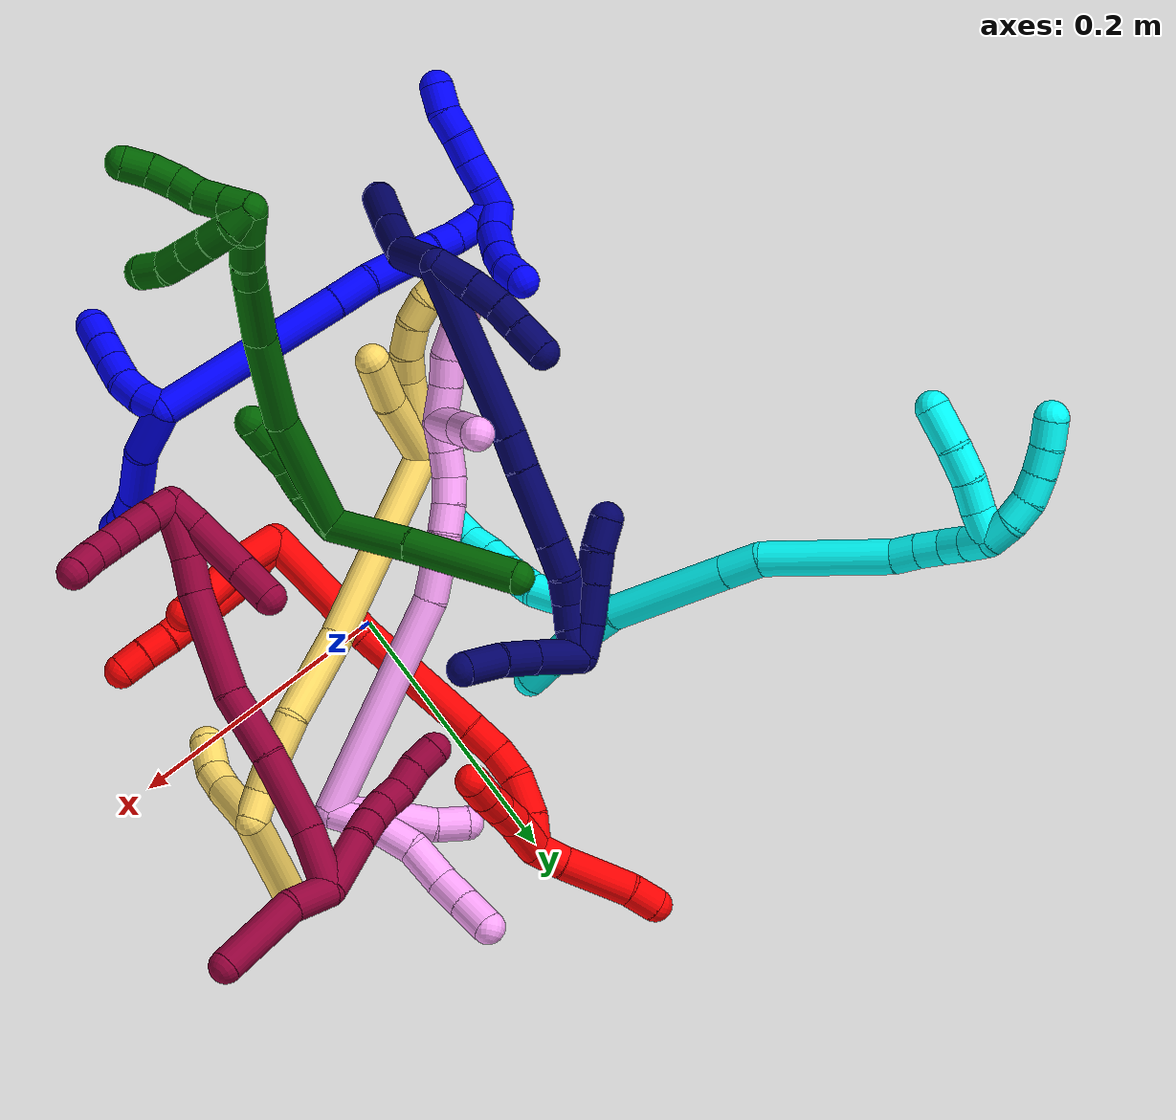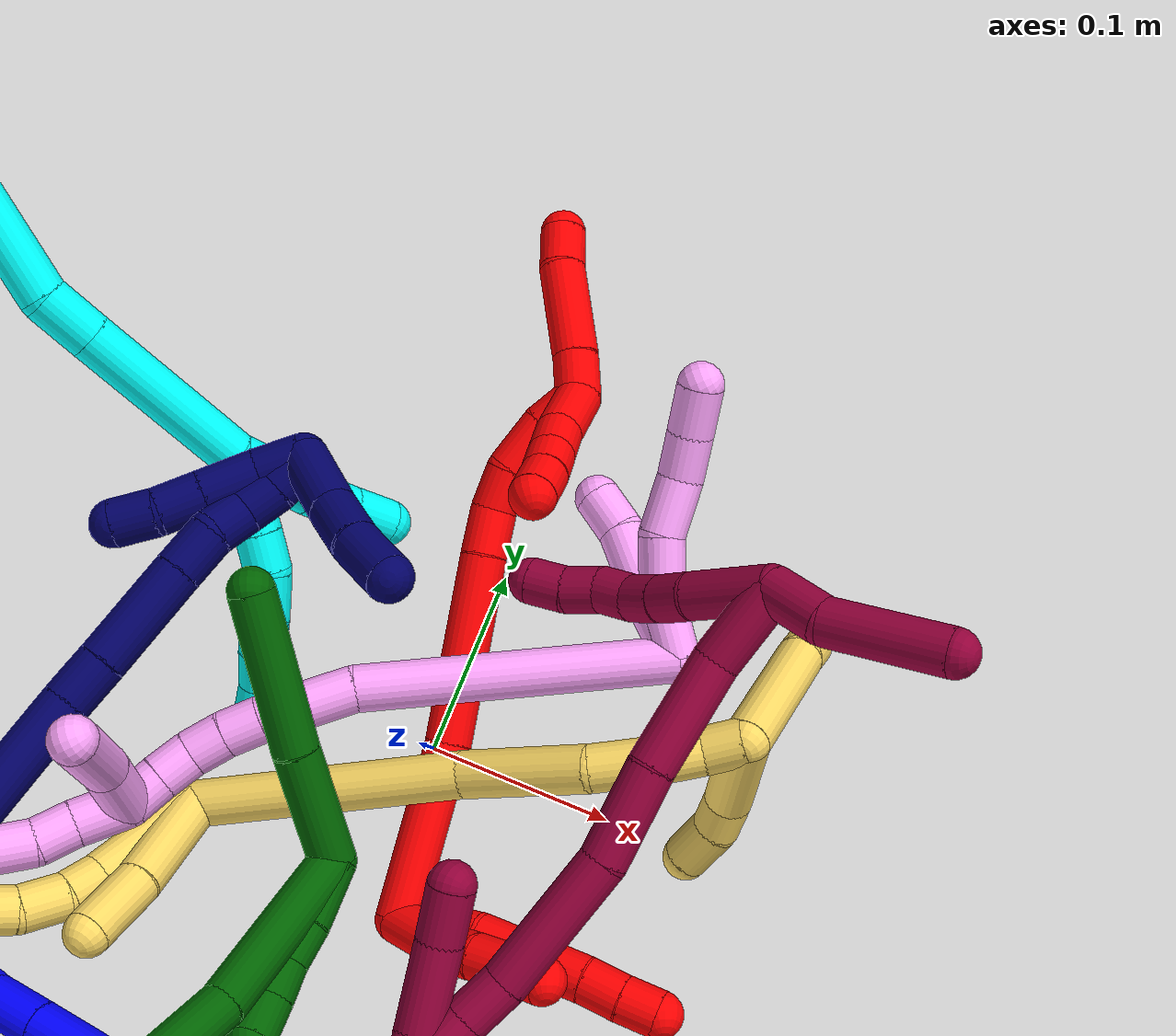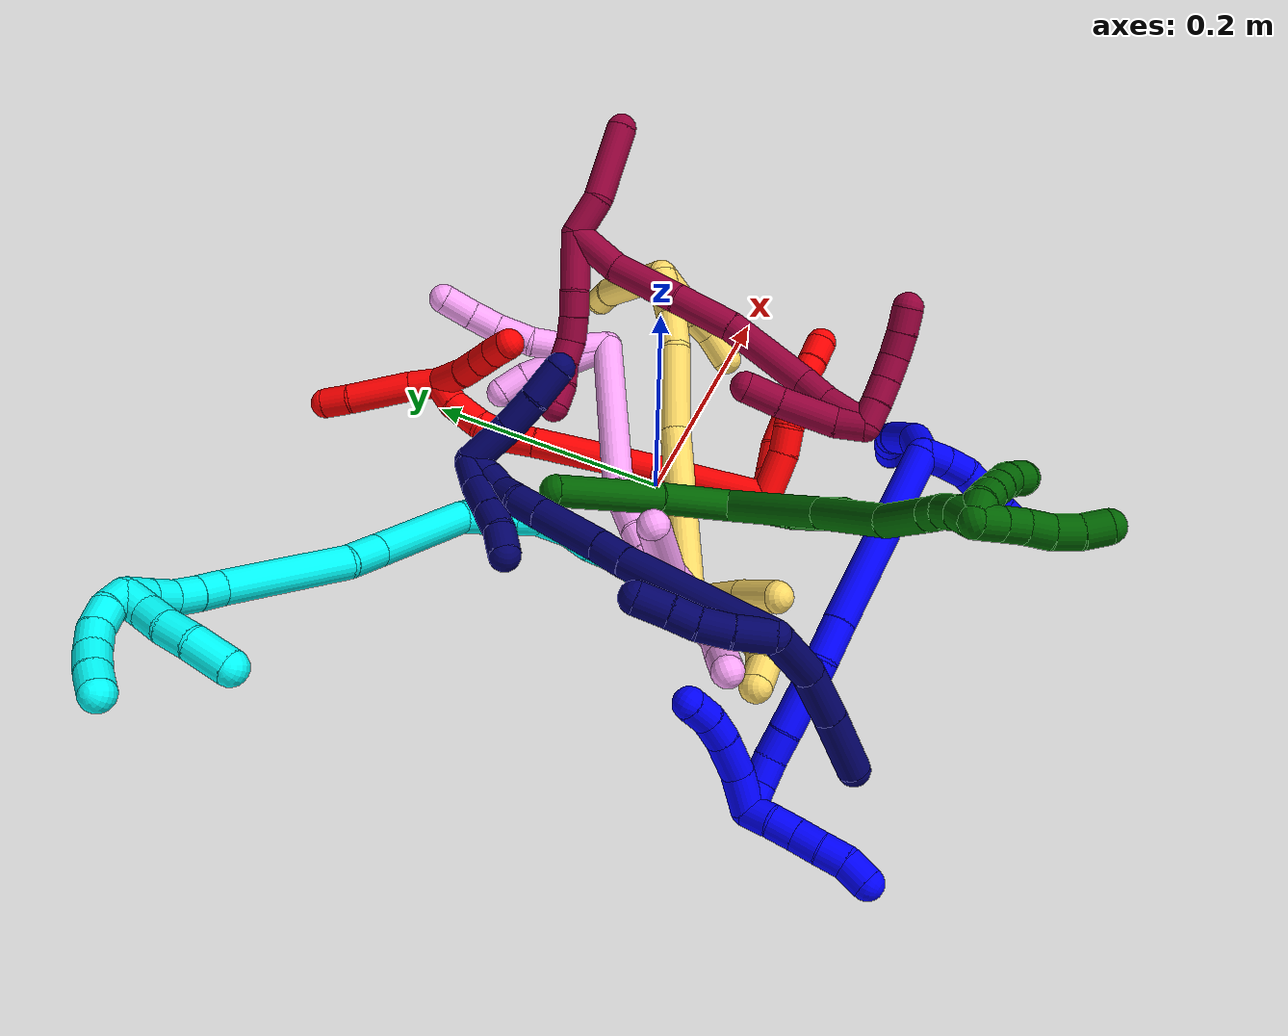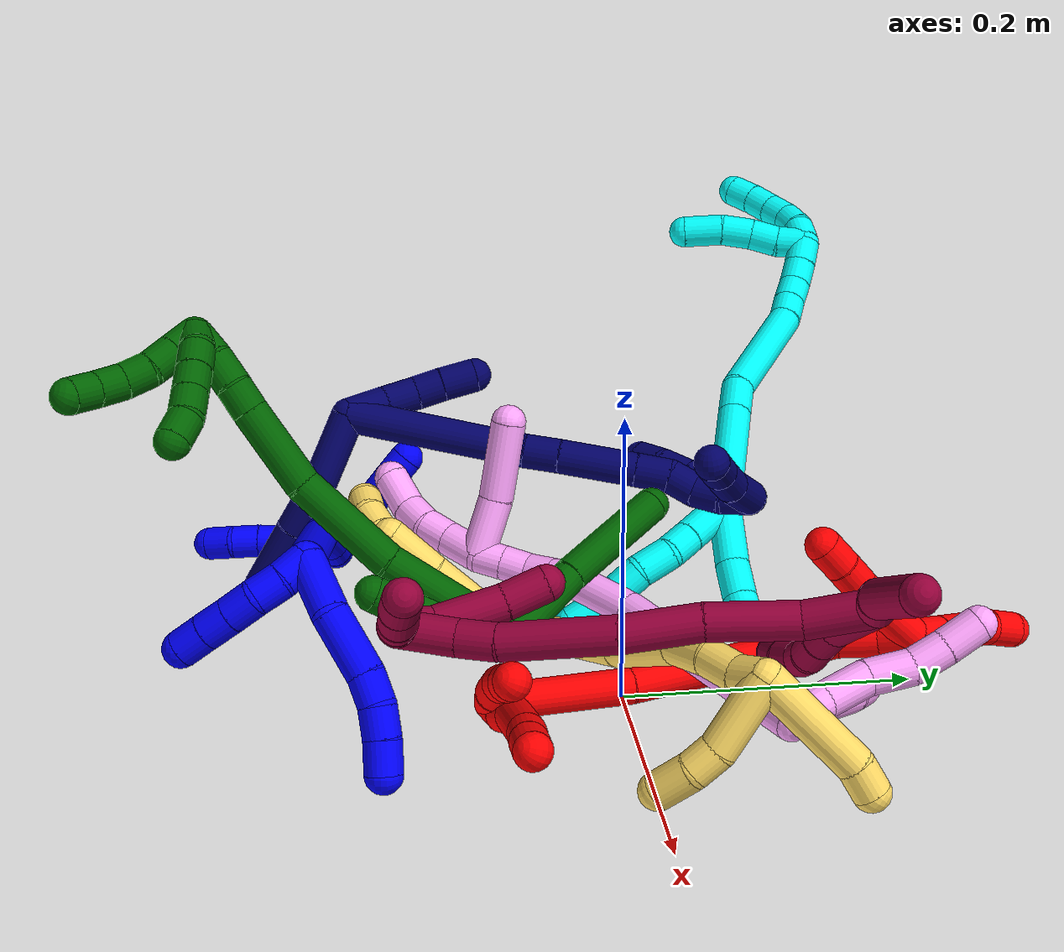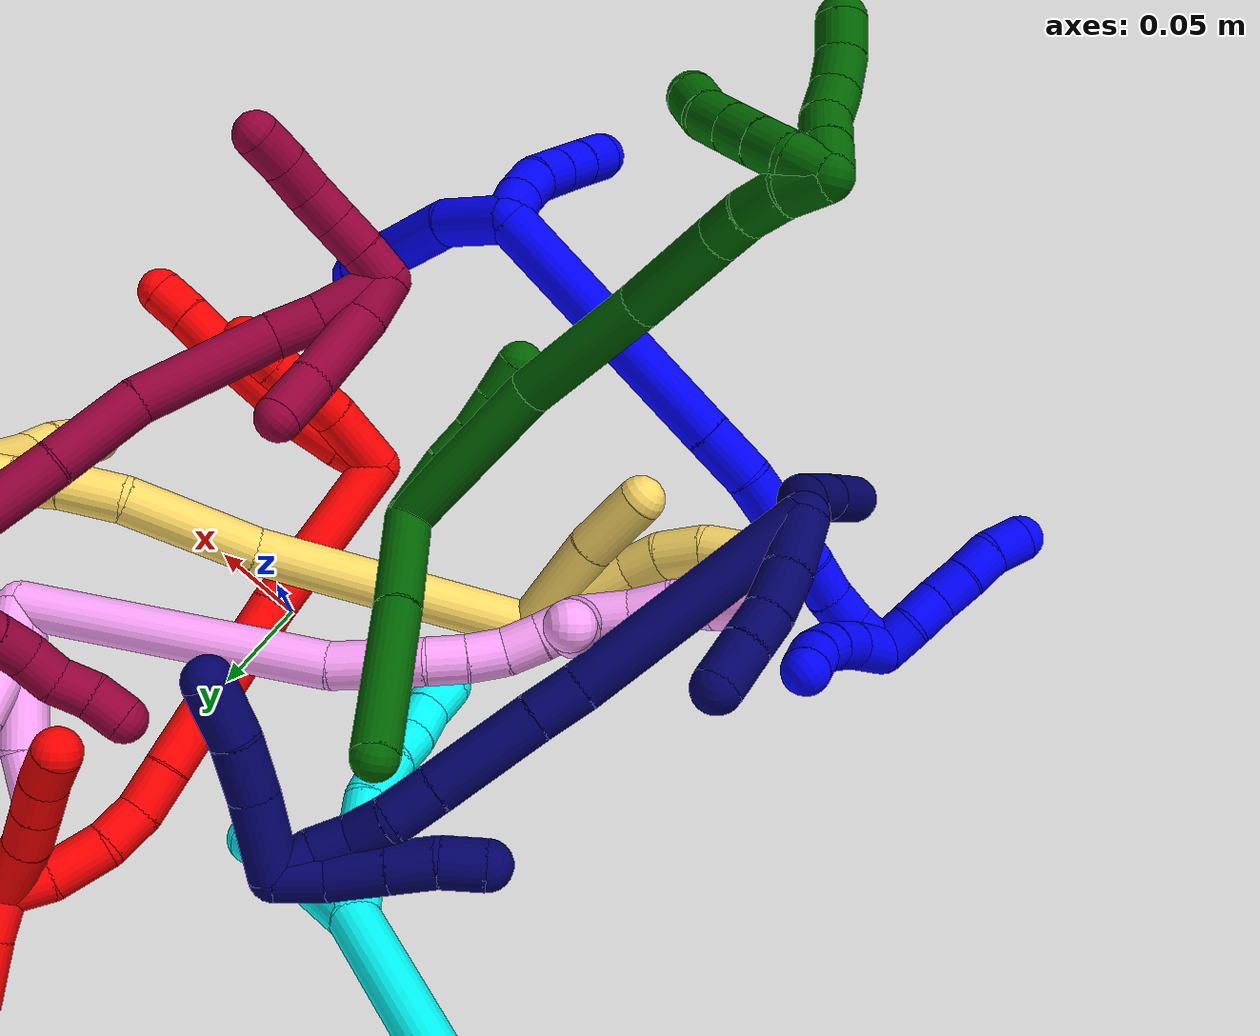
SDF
<sdf version="1.7">
 <world name="default">
  <plugin name="TubeGeneratorPlugin" filename="libtube_generator_plugin.so"/>
  <model name="photoneo_s_sensor">
   <static>1</static>
   <pose>0 0 2 1.57079 1.57079 3.14159</pose>
   <link name="link">
    <inertial><mass>0.1</mass></inertial>
    <sensor name="sensor" type="depth">
     <update_rate>30</update_rate>
     <camera>
      <horizontal_fov>1.22</horizontal_fov>
      <image><width>1920</width><height>1200</height><format>B8G8R8</format></image>
      <clip><near>0.1</near><far>4</far></clip>
      <depth_camera><output>points</output></depth_camera>
     </camera>
     <plugin name="camera_plugin" filename="libgazebo_ros_depth_camera.so">
      <baseline>0.2</baseline>
      <alwaysOn>1</alwaysOn>
      <updateRate>0.0</updateRate>
      <cameraName>camera_ir</cameraName>
      <imageTopicName>/camera/color/image_raw</imageTopicName>
      <cameraInfoTopicName>/camera/color/camera_info</cameraInfoTopicName>
      <depthImageTopicName>/camera/depth/image_raw</depthImageTopicName>
      <depthImageCameraInfoTopicName>/camera/depth/camera_info</depthImageCameraInfoTopicName>
      <pointCloudTopicName>/camera/depth/points</pointCloudTopicName>
      <frameName>fr_optical</frameName>
      <pointCloudCutoff>0.1</pointCloudCutoff>
      <pointCloudCutoffMax>2.0</pointCloudCutoffMax>
      <distortionK1>0</distortionK1>
      <distortionK2>0</distortionK2>
      <distortionK3>0</distortionK3>
      <distortionT1>0</distortionT1>
      <distortionT2>0</distortionT2>
      <CxPrime>0</CxPrime>
      <Cx>0</Cx>
      <Cy>0</Cy>
      <focalLength>0</focalLength>
      <hackBaseline>0</hackBaseline>
     </plugin>
    </sensor>
   </link>
  </model>
  <gravity>0 0 -9.8</gravity>
  <magnetic_field>6e-06 2.3e-05 -4.2e-05</magnetic_field>
  <atmosphere type="adiabatic"/>
  <physics name="default_physics" default="0" type="ode">
   <max_step_size>0.003</max_step_size>
   <real_time_factor>1</real_time_factor>
   <real_time_update_rate>1000</real_time_update_rate>
   <max_contacts>10000</max_contacts>
   <ode>
    <solver>
     <type>quick</type>
     <iters>100</iters>
     <sor>1.3</sor>
     <use_dynamic_moi_rescaling>0</use_dynamic_moi_rescaling>
    </solver>
    <constraints>
     <contact_max_correcting_vel>0</contact_max_correcting_vel>
     <contact_surface_layer>0.001</contact_surface_layer>
     <cfm>0</cfm>
     <erp>0.2</erp>
    </constraints>
   </ode>
  </physics>
  <scene><ambient>0.4 0.4 0.4 1</ambient><background>0.7 0.7 0.7 1</background><shadows>0</shadows></scene>
  <audio><device>default</device></audio>
  <spherical_coordinates>
   <surface_model>EARTH_WGS84</surface_model>
   <latitude_deg>0</latitude_deg>
   <longitude_deg>0</longitude_deg>
   <elevation>0</elevation>
   <heading_deg>0</heading_deg>
  </spherical_coordinates>
  <model name="bin">
   <static>1</static>
   <link name="bottom">
    <collision name="collision-bottom">
     <pose>0 0 -0.01 0 -0 0</pose>
     <geometry><box><size>0.8 0.6 0.02</size></box></geometry>
     <surface>
      <friction><ode><mu>100</mu><mu2>100</mu2></ode></friction>
      <contact><collide_bitmask>65535</collide_bitmask></contact>
     </surface>
    </collision>
   </link>
   <link name="west_wall">
    <collision name="collision-west_wall">
     <pose>-0.41 0 0.1 0 -0 0</pose>
     <geometry><box><size>0.02 0.6 0.2</size></box></geometry>
     <surface>
      <friction><ode><mu>100</mu><mu2>100</mu2></ode></friction>
      <contact><collide_bitmask>65535</collide_bitmask></contact>
     </surface>
    </collision>
   </link>
   <link name="east_wall">
    <collision name="collision-east_wall">
     <pose>0.41 0 0.1 0 -0 0</pose>
     <geometry><box><size>0.02 0.6 0.2</size></box></geometry>
     <surface>
      <friction><ode><mu>100</mu><mu2>100</mu2></ode></friction>
      <contact><collide_bitmask>65535</collide_bitmask></contact>
     </surface>
    </collision>
   </link>
   <link name="south_wall">
    <collision name="collision-south_wall">
     <pose>0 -0.31 0.1 0 -0 0</pose>
     <geometry><box><size>0.8 0.02 0.2</size></box></geometry>
     <surface>
      <friction><ode><mu>100</mu><mu2>100</mu2></ode></friction>
      <contact><collide_bitmask>65535</collide_bitmask></contact>
     </surface>
    </collision>
   </link>
   <link name="north_wall">
    <collision name="collision-north_wall">
     <pose>0 0.31 0.1 0 -0 0</pose>
     <geometry><box><size>0.8 0.02 0.2</size></box></geometry>
     <surface>
      <friction><ode><mu>100</mu><mu2>100</mu2></ode></friction>
      <contact><collide_bitmask>65535</collide_bitmask></contact>
     </surface>
    </collision>
   </link>
  </model>
  <model name="1">
   <static>0</static>
   <link name="1">
    <collision name="collision-cylinder-e_1_2_8">
     <pose>0.01848 0.000764 -0.009724 -3.06314 1.08515 -3.01159</pose>
     <geometry><cylinder><radius>0.0125</radius><length>0.041792</length></cylinder></geometry>
     <surface>
      <friction><ode><mu>1.16</mu><mu2>1.16</mu2><slip1>0</slip1><slip2>0</slip2></ode></friction>
      <contact><ode><kp>1e+06</kp><kd>1</kd><max_vel>0</max_vel><min_depth>0.001</min_depth></ode></contact>
     </surface>
    </collision>
    <visual name="visual-cylinder-e_1_2_8">
     <pose>0.01848 0.000764 -0.009724 -3.06314 1.08515 -3.01159</pose>
     <geometry><cylinder><radius>0.0125</radius><length>0.041792</length></cylinder></geometry>
     <material><ambient>0 0 1 1</ambient></material>
    </visual>
    <collision name="collision-cylinder-e_2_8_9">
     <pose>0.054802 -0.004232 -0.031572 2.69802 0.925812 2.29284</pose>
     <geometry><cylinder><radius>0.0125</radius><length>0.044657</length></cylinder></geometry>
     <surface>
      <friction><ode><mu>1.16</mu><mu2>1.16</mu2><slip1>0</slip1><slip2>0</slip2></ode></friction>
      <contact><ode><kp>1e+06</kp><kd>1</kd><max_vel>0</max_vel><min_depth>0.001</min_depth></ode></contact>
     </surface>
    </collision>
    <visual name="visual-cylinder-e_2_8_9">
     <pose>0.054802 -0.004232 -0.031572 2.69802 0.925812 2.29284</pose>
     <geometry><cylinder><radius>0.0125</radius><length>0.044657</length></cylinder></geometry>
     <material><ambient>0 0 1 1</ambient></material>
    </visual>
    <collision name="collision-cylinder-e_3_9_10">
     <pose>0.081734 -0.012491 -0.047685 2.58209 1.093 2.25915</pose>
     <geometry><cylinder><radius>0.0125</radius><length>0.02047</length></cylinder></geometry>
     <surface>
      <friction><ode><mu>1.16</mu><mu2>1.16</mu2><slip1>0</slip1><slip2>0</slip2></ode></friction>
      <contact><ode><kp>1e+06</kp><kd>1</kd><max_vel>0</max_vel><min_depth>0.001</min_depth></ode></contact>
     </surface>
    </collision>
    <visual name="visual-cylinder-e_3_9_10">
     <pose>0.081734 -0.012491 -0.047685 2.58209 1.093 2.25915</pose>
     <geometry><cylinder><radius>0.0125</radius><length>0.02047</length></cylinder></geometry>
     <material><ambient>0 0 1 1</ambient></material>
    </visual>
    <collision name="collision-cylinder-e_4_10_11">
     <pose>0.100137 -0.019161 -0.053563 1.99601 1.11384 1.5357</pose>
     <geometry><cylinder><radius>0.0125</radius><length>0.020759</length></cylinder></geometry>
     <surface>
      <friction><ode><mu>1.16</mu><mu2>1.16</mu2><slip1>0</slip1><slip2>0</slip2></ode></friction>
      <contact><ode><kp>1e+06</kp><kd>1</kd><max_vel>0</max_vel><min_depth>0.001</min_depth></ode></contact>
     </surface>
    </collision>
    <visual name="visual-cylinder-e_4_10_11">
     <pose>0.100137 -0.019161 -0.053563 1.99601 1.11384 1.5357</pose>
     <geometry><cylinder><radius>0.0125</radius><length>0.020759</length></cylinder></geometry>
     <material><ambient>0 0 1 1</ambient></material>
    </visual>
    <collision name="collision-cylinder-e_5_11_6">
     <pose>0.11956 -0.027998 -0.056243 1.73872 1.13298 1.29074</pose>
     <geometry><cylinder><radius>0.0125</radius><length>0.022323</length></cylinder></geometry>
     <surface>
      <friction><ode><mu>1.16</mu><mu2>1.16</mu2><slip1>0</slip1><slip2>0</slip2></ode></friction>
      <contact><ode><kp>1e+06</kp><kd>1</kd><max_vel>0</max_vel><min_depth>0.001</min_depth></ode></contact>
     </surface>
    </collision>
    <visual name="visual-cylinder-e_5_11_6">
     <pose>0.11956 -0.027998 -0.056243 1.73872 1.13298 1.29074</pose>
     <geometry><cylinder><radius>0.0125</radius><length>0.022323</length></cylinder></geometry>
     <material><ambient>0 0 1 1</ambient></material>
    </visual>
    <collision name="collision-cylinder-e_1_2_12">
     <pose>0.007157 7e-06 0.006985 -0.000953 0.797564 -0.000402</pose>
     <geometry><cylinder><radius>0.0125</radius><length>0.02</length></cylinder></geometry>
     <surface>
      <friction><ode><mu>1.16</mu><mu2>1.16</mu2><slip1>0</slip1><slip2>0</slip2></ode></friction>
      <contact><ode><kp>1e+06</kp><kd>1</kd><max_vel>0</max_vel><min_depth>0.001</min_depth></ode></contact>
     </surface>
    </collision>
    <visual name="visual-cylinder-e_1_2_12">
     <pose>0.007157 7e-06 0.006985 -0.000953 0.797564 -0.000402</pose>
     <geometry><cylinder><radius>0.0125</radius><length>0.02</length></cylinder></geometry>
     <material><ambient>0 0 1 1</ambient></material>
    </visual>
    <collision name="collision-cylinder-e_2_12_13">
     <pose>0.020176 -0.000851 0.022024 0.106895 0.626431 0.03465</pose>
     <geometry><cylinder><radius>0.0125</radius><length>0.02</length></cylinder></geometry>
     <surface>
      <friction><ode><mu>1.16</mu><mu2>1.16</mu2><slip1>0</slip1><slip2>0</slip2></ode></friction>
      <contact><ode><kp>1e+06</kp><kd>1</kd><max_vel>0</max_vel><min_depth>0.001</min_depth></ode></contact>
     </surface>
    </collision>
    <visual name="visual-cylinder-e_2_12_13">
     <pose>0.020176 -0.000851 0.022024 0.106895 0.626431 0.03465</pose>
     <geometry><cylinder><radius>0.0125</radius><length>0.02</length></cylinder></geometry>
     <material><ambient>0 0 1 1</ambient></material>
    </visual>
    <collision name="collision-cylinder-e_3_13_14">
     <pose>0.030696 -0.005456 0.038099 0.436419 0.484476 0.10947</pose>
     <geometry><cylinder><radius>0.0125</radius><length>0.02</length></cylinder></geometry>
     <surface>
      <friction><ode><mu>1.16</mu><mu2>1.16</mu2><slip1>0</slip1><slip2>0</slip2></ode></friction>
      <contact><ode><kp>1e+06</kp><kd>1</kd><max_vel>0</max_vel><min_depth>0.001</min_depth></ode></contact>
     </surface>
    </collision>
    <visual name="visual-cylinder-e_3_13_14">
     <pose>0.030696 -0.005456 0.038099 0.436419 0.484476 0.10947</pose>
     <geometry><cylinder><radius>0.0125</radius><length>0.02</length></cylinder></geometry>
     <material><ambient>0 0 1 1</ambient></material>
    </visual>
    <collision name="collision-cylinder-e_4_14_15">
     <pose>0.039768 -0.012936 0.054275 0.429954 0.457265 0.101534</pose>
     <geometry><cylinder><radius>0.0125</radius><length>0.02</length></cylinder></geometry>
     <surface>
      <friction><ode><mu>1.16</mu><mu2>1.16</mu2><slip1>0</slip1><slip2>0</slip2></ode></friction>
      <contact><ode><kp>1e+06</kp><kd>1</kd><max_vel>0</max_vel><min_depth>0.001</min_depth></ode></contact>
     </surface>
    </collision>
    <visual name="visual-cylinder-e_4_14_15">
     <pose>0.039768 -0.012936 0.054275 0.429954 0.457265 0.101534</pose>
     <geometry><cylinder><radius>0.0125</radius><length>0.02</length></cylinder></geometry>
     <material><ambient>0 0 1 1</ambient></material>
    </visual>
    <collision name="collision-cylinder-e_5_15_5">
     <pose>0.048616 -0.020631 0.070475 0.456888 0.459269 0.108592</pose>
     <geometry><cylinder><radius>0.0125</radius><length>0.02</length></cylinder></geometry>
     <surface>
      <friction><ode><mu>1.16</mu><mu2>1.16</mu2><slip1>0</slip1><slip2>0</slip2></ode></friction>
      <contact><ode><kp>1e+06</kp><kd>1</kd><max_vel>0</max_vel><min_depth>0.001</min_depth></ode></contact>
     </surface>
    </collision>
    <visual name="visual-cylinder-e_5_15_5">
     <pose>0.048616 -0.020631 0.070475 0.456888 0.459269 0.108592</pose>
     <geometry><cylinder><radius>0.0125</radius><length>0.02</length></cylinder></geometry>
     <material><ambient>0 0 1 1</ambient></material>
    </visual>
    <collision name="collision-cylinder-e_1_2_16">
     <pose>-0.037191 -0.063229 0.00939 1.42337 -0.526936 -0.457148</pose>
     <geometry><cylinder><radius>0.0125</radius><length>0.147908</length></cylinder></geometry>
     <surface>
      <friction><ode><mu>1.16</mu><mu2>1.16</mu2><slip1>0</slip1><slip2>0</slip2></ode></friction>
      <contact><ode><kp>1e+06</kp><kd>1</kd><max_vel>0</max_vel><min_depth>0.001</min_depth></ode></contact>
     </surface>
    </collision>
    <visual name="visual-cylinder-e_1_2_16">
     <pose>-0.037191 -0.063229 0.00939 1.42337 -0.526936 -0.457148</pose>
     <geometry><cylinder><radius>0.0125</radius><length>0.147908</length></cylinder></geometry>
     <material><ambient>0 0 1 1</ambient></material>
    </visual>
    <collision name="collision-cylinder-e_2_16_17">
     <pose>-0.081708 -0.1399 0.020968 1.40938 -0.493566 -0.42205</pose>
     <geometry><cylinder><radius>0.0125</radius><length>0.03093</length></cylinder></geometry>
     <surface>
      <friction><ode><mu>1.16</mu><mu2>1.16</mu2><slip1>0</slip1><slip2>0</slip2></ode></friction>
      <contact><ode><kp>1e+06</kp><kd>1</kd><max_vel>0</max_vel><min_depth>0.001</min_depth></ode></contact>
     </surface>
    </collision>
    <visual name="visual-cylinder-e_2_16_17">
     <pose>-0.081708 -0.1399 0.020968 1.40938 -0.493566 -0.42205</pose>
     <geometry><cylinder><radius>0.0125</radius><length>0.03093</length></cylinder></geometry>
     <material><ambient>0 0 1 1</ambient></material>
    </visual>
    <collision name="collision-cylinder-e_3_17_18">
     <pose>-0.097896 -0.181022 0.024732 1.51398 -0.309368 -0.292521</pose>
     <geometry><cylinder><radius>0.0125</radius><length>0.058212</length></cylinder></geometry>
     <surface>
      <friction><ode><mu>1.16</mu><mu2>1.16</mu2><slip1>0</slip1><slip2>0</slip2></ode></friction>
      <contact><ode><kp>1e+06</kp><kd>1</kd><max_vel>0</max_vel><min_depth>0.001</min_depth></ode></contact>
     </surface>
    </collision>
    <visual name="visual-cylinder-e_3_17_18">
     <pose>-0.097896 -0.181022 0.024732 1.51398 -0.309368 -0.292521</pose>
     <geometry><cylinder><radius>0.0125</radius><length>0.058212</length></cylinder></geometry>
     <material><ambient>0 0 1 1</ambient></material>
    </visual>
    <collision name="collision-cylinder-e_4_18_19">
     <pose>-0.108805 -0.219174 0.026453 1.55677 -0.19303 -0.190358</pose>
     <geometry><cylinder><radius>0.0125</radius><length>0.021345</length></cylinder></geometry>
     <surface>
      <friction><ode><mu>1.16</mu><mu2>1.16</mu2><slip1>0</slip1><slip2>0</slip2></ode></friction>
      <contact><ode><kp>1e+06</kp><kd>1</kd><max_vel>0</max_vel><min_depth>0.001</min_depth></ode></contact>
     </surface>
    </collision>
    <visual name="visual-cylinder-e_4_18_19">
     <pose>-0.108805 -0.219174 0.026453 1.55677 -0.19303 -0.190358</pose>
     <geometry><cylinder><radius>0.0125</radius><length>0.021345</length></cylinder></geometry>
     <material><ambient>0 0 1 1</ambient></material>
    </visual>
    <collision name="collision-cylinder-e_5_19_20">
     <pose>-0.114189 -0.239169 0.027823 1.44304 -0.334518 -0.294916</pose>
     <geometry><cylinder><radius>0.0125</radius><length>0.020326</length></cylinder></geometry>
     <surface>
      <friction><ode><mu>1.16</mu><mu2>1.16</mu2><slip1>0</slip1><slip2>0</slip2></ode></friction>
      <contact><ode><kp>1e+06</kp><kd>1</kd><max_vel>0</max_vel><min_depth>0.001</min_depth></ode></contact>
     </surface>
    </collision>
    <visual name="visual-cylinder-e_5_19_20">
     <pose>-0.114189 -0.239169 0.027823 1.44304 -0.334518 -0.294916</pose>
     <geometry><cylinder><radius>0.0125</radius><length>0.020326</length></cylinder></geometry>
     <material><ambient>0 0 1 1</ambient></material>
    </visual>
    <collision name="collision-cylinder-e_6_20_1">
     <pose>-0.123703 -0.257115 0.031065 1.33554 -0.619415 -0.494407</pose>
     <geometry><cylinder><radius>0.0125</radius><length>0.021279</length></cylinder></geometry>
     <surface>
      <friction><ode><mu>1.16</mu><mu2>1.16</mu2><slip1>0</slip1><slip2>0</slip2></ode></friction>
      <contact><ode><kp>1e+06</kp><kd>1</kd><max_vel>0</max_vel><min_depth>0.001</min_depth></ode></contact>
     </surface>
    </collision>
    <visual name="visual-cylinder-e_6_20_1">
     <pose>-0.123703 -0.257115 0.031065 1.33554 -0.619415 -0.494407</pose>
     <geometry><cylinder><radius>0.0125</radius><length>0.021279</length></cylinder></geometry>
     <material><ambient>0 0 1 1</ambient></material>
    </visual>
    <collision name="collision-cylinder-e_1_1_21">
     <pose>-0.133481 -0.254119 0.024475 -2.21678 -0.246691 0.487545</pose>
     <geometry><cylinder><radius>0.0125</radius><length>0.029497</length></cylinder></geometry>
     <surface>
      <friction><ode><mu>1.16</mu><mu2>1.16</mu2><slip1>0</slip1><slip2>0</slip2></ode></friction>
      <contact><ode><kp>1e+06</kp><kd>1</kd><max_vel>0</max_vel><min_depth>0.001</min_depth></ode></contact>
     </surface>
    </collision>
    <visual name="visual-cylinder-e_1_1_21">
     <pose>-0.133481 -0.254119 0.024475 -2.21678 -0.246691 0.487545</pose>
     <geometry><cylinder><radius>0.0125</radius><length>0.029497</length></cylinder></geometry>
     <material><ambient>0 0 1 1</ambient></material>
    </visual>
    <collision name="collision-cylinder-e_2_21_22">
     <pose>-0.144383 -0.232455 0.007658 -2.2463 -0.507557 0.990552</pose>
     <geometry><cylinder><radius>0.0125</radius><length>0.030038</length></cylinder></geometry>
     <surface>
      <friction><ode><mu>1.16</mu><mu2>1.16</mu2><slip1>0</slip1><slip2>0</slip2></ode></friction>
      <contact><ode><kp>1e+06</kp><kd>1</kd><max_vel>0</max_vel><min_depth>0.001</min_depth></ode></contact>
     </surface>
    </collision>
    <visual name="visual-cylinder-e_2_21_22">
     <pose>-0.144383 -0.232455 0.007658 -2.2463 -0.507557 0.990552</pose>
     <geometry><cylinder><radius>0.0125</radius><length>0.030038</length></cylinder></geometry>
     <material><ambient>0 0 1 1</ambient></material>
    </visual>
    <collision name="collision-cylinder-e_3_22_23">
     <pose>-0.157239 -0.216504 -0.006706 -2.39401 -0.584677 1.30896</pose>
     <geometry><cylinder><radius>0.0125</radius><length>0.020135</length></cylinder></geometry>
     <surface>
      <friction><ode><mu>1.16</mu><mu2>1.16</mu2><slip1>0</slip1><slip2>0</slip2></ode></friction>
      <contact><ode><kp>1e+06</kp><kd>1</kd><max_vel>0</max_vel><min_depth>0.001</min_depth></ode></contact>
     </surface>
    </collision>
    <visual name="visual-cylinder-e_3_22_23">
     <pose>-0.157239 -0.216504 -0.006706 -2.39401 -0.584677 1.30896</pose>
     <geometry><cylinder><radius>0.0125</radius><length>0.020135</length></cylinder></geometry>
     <material><ambient>0 0 1 1</ambient></material>
    </visual>
    <collision name="collision-cylinder-e_4_23_4">
     <pose>-0.169917 -0.207169 -0.019143 -2.61786 -0.776275 1.98112</pose>
     <geometry><cylinder><radius>0.0125</radius><length>0.02033</length></cylinder></geometry>
     <surface>
      <friction><ode><mu>1.16</mu><mu2>1.16</mu2><slip1>0</slip1><slip2>0</slip2></ode></friction>
      <contact><ode><kp>1e+06</kp><kd>1</kd><max_vel>0</max_vel><min_depth>0.001</min_depth></ode></contact>
     </surface>
    </collision>
    <visual name="visual-cylinder-e_4_23_4">
     <pose>-0.169917 -0.207169 -0.019143 -2.61786 -0.776275 1.98112</pose>
     <geometry><cylinder><radius>0.0125</radius><length>0.02033</length></cylinder></geometry>
     <material><ambient>0 0 1 1</ambient></material>
    </visual>
    <collision name="collision-cylinder-e_1_1_24">
     <pose>-0.130903 -0.263937 0.042902 -0.161784 -0.102501 0.008317</pose>
     <geometry><cylinder><radius>0.0125</radius><length>0.02</length></cylinder></geometry>
     <surface>
      <friction><ode><mu>1.16</mu><mu2>1.16</mu2><slip1>0</slip1><slip2>0</slip2></ode></friction>
      <contact><ode><kp>1e+06</kp><kd>1</kd><max_vel>0</max_vel><min_depth>0.001</min_depth></ode></contact>
     </surface>
    </collision>
    <visual name="visual-cylinder-e_1_1_24">
     <pose>-0.130903 -0.263937 0.042902 -0.161784 -0.102501 0.008317</pose>
     <geometry><cylinder><radius>0.0125</radius><length>0.02</length></cylinder></geometry>
     <material><ambient>0 0 1 1</ambient></material>
    </visual>
    <collision name="collision-cylinder-e_2_24_25">
     <pose>-0.131223 -0.261922 0.062686 -0.041307 0.070362 -0.001454</pose>
     <geometry><cylinder><radius>0.0125</radius><length>0.02</length></cylinder></geometry>
     <surface>
      <friction><ode><mu>1.16</mu><mu2>1.16</mu2><slip1>0</slip1><slip2>0</slip2></ode></friction>
      <contact><ode><kp>1e+06</kp><kd>1</kd><max_vel>0</max_vel><min_depth>0.001</min_depth></ode></contact>
     </surface>
    </collision>
    <visual name="visual-cylinder-e_2_24_25">
     <pose>-0.131223 -0.261922 0.062686 -0.041307 0.070362 -0.001454</pose>
     <geometry><cylinder><radius>0.0125</radius><length>0.02</length></cylinder></geometry>
     <material><ambient>0 0 1 1</ambient></material>
    </visual>
    <collision name="collision-cylinder-e_3_25_26">
     <pose>-0.130695 -0.261009 0.082639 -0.050197 -0.017482 0.000439</pose>
     <geometry><cylinder><radius>0.0125</radius><length>0.02</length></cylinder></geometry>
     <surface>
      <friction><ode><mu>1.16</mu><mu2>1.16</mu2><slip1>0</slip1><slip2>0</slip2></ode></friction>
      <contact><ode><kp>1e+06</kp><kd>1</kd><max_vel>0</max_vel><min_depth>0.001</min_depth></ode></contact>
     </surface>
    </collision>
    <visual name="visual-cylinder-e_3_25_26">
     <pose>-0.130695 -0.261009 0.082639 -0.050197 -0.017482 0.000439</pose>
     <geometry><cylinder><radius>0.0125</radius><length>0.02</length></cylinder></geometry>
     <material><ambient>0 0 1 1</ambient></material>
    </visual>
    <collision name="collision-cylinder-e_4_26_27">
     <pose>-0.129903 -0.260227 0.102574 -0.028174 0.096785 -0.001365</pose>
     <geometry><cylinder><radius>0.0125</radius><length>0.02</length></cylinder></geometry>
     <surface>
      <friction><ode><mu>1.16</mu><mu2>1.16</mu2><slip1>0</slip1><slip2>0</slip2></ode></friction>
      <contact><ode><kp>1e+06</kp><kd>1</kd><max_vel>0</max_vel><min_depth>0.001</min_depth></ode></contact>
     </surface>
    </collision>
    <visual name="visual-cylinder-e_4_26_27">
     <pose>-0.129903 -0.260227 0.102574 -0.028174 0.096785 -0.001365</pose>
     <geometry><cylinder><radius>0.0125</radius><length>0.02</length></cylinder></geometry>
     <material><ambient>0 0 1 1</ambient></material>
    </visual>
    <collision name="collision-cylinder-e_5_27_3">
     <pose>-0.129145 -0.262231 0.122257 0.230592 -0.02086 -0.002416</pose>
     <geometry><cylinder><radius>0.0125</radius><length>0.02</length></cylinder></geometry>
     <surface>
      <friction><ode><mu>1.16</mu><mu2>1.16</mu2><slip1>0</slip1><slip2>0</slip2></ode></friction>
      <contact><ode><kp>1e+06</kp><kd>1</kd><max_vel>0</max_vel><min_depth>0.001</min_depth></ode></contact>
     </surface>
    </collision>
    <visual name="visual-cylinder-e_5_27_3">
     <pose>-0.129145 -0.262231 0.122257 0.230592 -0.02086 -0.002416</pose>
     <geometry><cylinder><radius>0.0125</radius><length>0.02</length></cylinder></geometry>
     <material><ambient>0 0 1 1</ambient></material>
    </visual>
    <collision name="collision-sphere-3">
     <pose>-0.129354 -0.264516 0.13199 0 -0 0</pose>
     <geometry><sphere><radius>0.0125</radius></sphere></geometry>
     <surface>
      <friction><ode><mu>1.16</mu><mu2>1.16</mu2><slip1>0</slip1><slip2>0</slip2></ode></friction>
      <contact><ode><kp>1e+06</kp><kd>1</kd><max_vel>0</max_vel><min_depth>0.001</min_depth></ode></contact>
     </surface>
    </collision>
    <visual name="visual-sphere-3">
     <pose>-0.129354 -0.264516 0.13199 0 -0 0</pose>
     <geometry><sphere><radius>0.0125</radius></sphere></geometry>
     <material><ambient>0 0 1 1</ambient></material>
    </visual>
    <collision name="collision-sphere-27">
     <pose>-0.128937 -0.259946 0.112523 0 -0 0</pose>
     <geometry><sphere><radius>0.0125</radius></sphere></geometry>
     <surface>
      <friction><ode><mu>1.16</mu><mu2>1.16</mu2><slip1>0</slip1><slip2>0</slip2></ode></friction>
      <contact><ode><kp>1e+06</kp><kd>1</kd><max_vel>0</max_vel><min_depth>0.001</min_depth></ode></contact>
     </surface>
    </collision>
    <visual name="visual-sphere-27">
     <pose>-0.128937 -0.259946 0.112523 0 -0 0</pose>
     <geometry><sphere><radius>0.0125</radius></sphere></geometry>
     <material><ambient>0 0 1 1</ambient></material>
    </visual>
    <collision name="collision-sphere-26">
     <pose>-0.13087 -0.260507 0.092625 0 -0 0</pose>
     <geometry><sphere><radius>0.0125</radius></sphere></geometry>
     <surface>
      <friction><ode><mu>1.16</mu><mu2>1.16</mu2><slip1>0</slip1><slip2>0</slip2></ode></friction>
      <contact><ode><kp>1e+06</kp><kd>1</kd><max_vel>0</max_vel><min_depth>0.001</min_depth></ode></contact>
     </surface>
    </collision>
    <visual name="visual-sphere-26">
     <pose>-0.13087 -0.260507 0.092625 0 -0 0</pose>
     <geometry><sphere><radius>0.0125</radius></sphere></geometry>
     <material><ambient>0 0 1 1</ambient></material>
    </visual>
    <collision name="collision-sphere-25">
     <pose>-0.13052 -0.26151 0.072653 0 -0 0</pose>
     <geometry><sphere><radius>0.0125</radius></sphere></geometry>
     <surface>
      <friction><ode><mu>1.16</mu><mu2>1.16</mu2><slip1>0</slip1><slip2>0</slip2></ode></friction>
      <contact><ode><kp>1e+06</kp><kd>1</kd><max_vel>0</max_vel><min_depth>0.001</min_depth></ode></contact>
     </surface>
    </collision>
    <visual name="visual-sphere-25">
     <pose>-0.13052 -0.26151 0.072653 0 -0 0</pose>
     <geometry><sphere><radius>0.0125</radius></sphere></geometry>
     <material><ambient>0 0 1 1</ambient></material>
    </visual>
    <collision name="collision-sphere-24">
     <pose>-0.131926 -0.262334 0.05272 0 -0 0</pose>
     <geometry><sphere><radius>0.0125</radius></sphere></geometry>
     <surface>
      <friction><ode><mu>1.16</mu><mu2>1.16</mu2><slip1>0</slip1><slip2>0</slip2></ode></friction>
      <contact><ode><kp>1e+06</kp><kd>1</kd><max_vel>0</max_vel><min_depth>0.001</min_depth></ode></contact>
     </surface>
    </collision>
    <visual name="visual-sphere-24">
     <pose>-0.131926 -0.262334 0.05272 0 -0 0</pose>
     <geometry><sphere><radius>0.0125</radius></sphere></geometry>
     <material><ambient>0 0 1 1</ambient></material>
    </visual>
    <collision name="collision-sphere-4">
     <pose>-0.177039 -0.203542 -0.025424 0 -0 0</pose>
     <geometry><sphere><radius>0.0125</radius></sphere></geometry>
     <surface>
      <friction><ode><mu>1.16</mu><mu2>1.16</mu2><slip1>0</slip1><slip2>0</slip2></ode></friction>
      <contact><ode><kp>1e+06</kp><kd>1</kd><max_vel>0</max_vel><min_depth>0.001</min_depth></ode></contact>
     </surface>
    </collision>
    <visual name="visual-sphere-4">
     <pose>-0.177039 -0.203542 -0.025424 0 -0 0</pose>
     <geometry><sphere><radius>0.0125</radius></sphere></geometry>
     <material><ambient>0 0 1 1</ambient></material>
    </visual>
    <collision name="collision-sphere-23">
     <pose>-0.162796 -0.210797 -0.012862 0 -0 0</pose>
     <geometry><sphere><radius>0.0125</radius></sphere></geometry>
     <surface>
      <friction><ode><mu>1.16</mu><mu2>1.16</mu2><slip1>0</slip1><slip2>0</slip2></ode></friction>
      <contact><ode><kp>1e+06</kp><kd>1</kd><max_vel>0</max_vel><min_depth>0.001</min_depth></ode></contact>
     </surface>
    </collision>
    <visual name="visual-sphere-23">
     <pose>-0.162796 -0.210797 -0.012862 0 -0 0</pose>
     <geometry><sphere><radius>0.0125</radius></sphere></geometry>
     <material><ambient>0 0 1 1</ambient></material>
    </visual>
    <collision name="collision-sphere-22">
     <pose>-0.151683 -0.222212 -0.00055 0 -0 0</pose>
     <geometry><sphere><radius>0.0125</radius></sphere></geometry>
     <surface>
      <friction><ode><mu>1.16</mu><mu2>1.16</mu2><slip1>0</slip1><slip2>0</slip2></ode></friction>
      <contact><ode><kp>1e+06</kp><kd>1</kd><max_vel>0</max_vel><min_depth>0.001</min_depth></ode></contact>
     </surface>
    </collision>
    <visual name="visual-sphere-22">
     <pose>-0.151683 -0.222212 -0.00055 0 -0 0</pose>
     <geometry><sphere><radius>0.0125</radius></sphere></geometry>
     <material><ambient>0 0 1 1</ambient></material>
    </visual>
    <collision name="collision-sphere-21">
     <pose>-0.137083 -0.242698 0.015865 0 -0 0</pose>
     <geometry><sphere><radius>0.0125</radius></sphere></geometry>
     <surface>
      <friction><ode><mu>1.16</mu><mu2>1.16</mu2><slip1>0</slip1><slip2>0</slip2></ode></friction>
      <contact><ode><kp>1e+06</kp><kd>1</kd><max_vel>0</max_vel><min_depth>0.001</min_depth></ode></contact>
     </surface>
    </collision>
    <visual name="visual-sphere-21">
     <pose>-0.137083 -0.242698 0.015865 0 -0 0</pose>
     <geometry><sphere><radius>0.0125</radius></sphere></geometry>
     <material><ambient>0 0 1 1</ambient></material>
    </visual>
    <collision name="collision-sphere-1">
     <pose>-0.12988 -0.265539 0.033084 0 -0 0</pose>
     <geometry><sphere><radius>0.0125</radius></sphere></geometry>
     <surface>
      <friction><ode><mu>1.16</mu><mu2>1.16</mu2><slip1>0</slip1><slip2>0</slip2></ode></friction>
      <contact><ode><kp>1e+06</kp><kd>1</kd><max_vel>0</max_vel><min_depth>0.001</min_depth></ode></contact>
     </surface>
    </collision>
    <visual name="visual-sphere-1">
     <pose>-0.12988 -0.265539 0.033084 0 -0 0</pose>
     <geometry><sphere><radius>0.0125</radius></sphere></geometry>
     <material><ambient>0 0 1 1</ambient></material>
    </visual>
    <collision name="collision-sphere-6">
     <pose>0.129669 -0.032663 -0.057034 0 -0 0</pose>
     <geometry><sphere><radius>0.0125</radius></sphere></geometry>
     <surface>
      <friction><ode><mu>1.16</mu><mu2>1.16</mu2><slip1>0</slip1><slip2>0</slip2></ode></friction>
      <contact><ode><kp>1e+06</kp><kd>1</kd><max_vel>0</max_vel><min_depth>0.001</min_depth></ode></contact>
     </surface>
    </collision>
    <visual name="visual-sphere-6">
     <pose>0.129669 -0.032663 -0.057034 0 -0 0</pose>
     <geometry><sphere><radius>0.0125</radius></sphere></geometry>
     <material><ambient>0 0 1 1</ambient></material>
    </visual>
    <collision name="collision-sphere-11">
     <pose>0.109451 -0.023333 -0.055452 0 -0 0</pose>
     <geometry><sphere><radius>0.0125</radius></sphere></geometry>
     <surface>
      <friction><ode><mu>1.16</mu><mu2>1.16</mu2><slip1>0</slip1><slip2>0</slip2></ode></friction>
      <contact><ode><kp>1e+06</kp><kd>1</kd><max_vel>0</max_vel><min_depth>0.001</min_depth></ode></contact>
     </surface>
    </collision>
    <visual name="visual-sphere-11">
     <pose>0.109451 -0.023333 -0.055452 0 -0 0</pose>
     <geometry><sphere><radius>0.0125</radius></sphere></geometry>
     <material><ambient>0 0 1 1</ambient></material>
    </visual>
    <collision name="collision-sphere-10">
     <pose>0.090823 -0.014989 -0.051674 0 -0 0</pose>
     <geometry><sphere><radius>0.0125</radius></sphere></geometry>
     <surface>
      <friction><ode><mu>1.16</mu><mu2>1.16</mu2><slip1>0</slip1><slip2>0</slip2></ode></friction>
      <contact><ode><kp>1e+06</kp><kd>1</kd><max_vel>0</max_vel><min_depth>0.001</min_depth></ode></contact>
     </surface>
    </collision>
    <visual name="visual-sphere-10">
     <pose>0.090823 -0.014989 -0.051674 0 -0 0</pose>
     <geometry><sphere><radius>0.0125</radius></sphere></geometry>
     <material><ambient>0 0 1 1</ambient></material>
    </visual>
    <collision name="collision-sphere-9">
     <pose>0.072645 -0.009993 -0.043696 0 -0 0</pose>
     <geometry><sphere><radius>0.0125</radius></sphere></geometry>
     <surface>
      <friction><ode><mu>1.16</mu><mu2>1.16</mu2><slip1>0</slip1><slip2>0</slip2></ode></friction>
      <contact><ode><kp>1e+06</kp><kd>1</kd><max_vel>0</max_vel><min_depth>0.001</min_depth></ode></contact>
     </surface>
    </collision>
    <visual name="visual-sphere-9">
     <pose>0.072645 -0.009993 -0.043696 0 -0 0</pose>
     <geometry><sphere><radius>0.0125</radius></sphere></geometry>
     <material><ambient>0 0 1 1</ambient></material>
    </visual>
    <collision name="collision-sphere-2">
     <geometry><sphere><radius>0.0125</radius></sphere></geometry>
     <surface>
      <friction><ode><mu>1.16</mu><mu2>1.16</mu2><slip1>0</slip1><slip2>0</slip2></ode></friction>
      <contact><ode><kp>1e+06</kp><kd>1</kd><max_vel>0</max_vel><min_depth>0.001</min_depth></ode></contact>
     </surface>
    </collision>
    <visual name="visual-sphere-2">
     <geometry><sphere><radius>0.0125</radius></sphere></geometry>
     <material><ambient>0 0 1 1</ambient></material>
    </visual>
    <collision name="collision-sphere-19">
     <pose>-0.110853 -0.229647 0.0266 0 -0 0</pose>
     <geometry><sphere><radius>0.0125</radius></sphere></geometry>
     <surface>
      <friction><ode><mu>1.16</mu><mu2>1.16</mu2><slip1>0</slip1><slip2>0</slip2></ode></friction>
      <contact><ode><kp>1e+06</kp><kd>1</kd><max_vel>0</max_vel><min_depth>0.001</min_depth></ode></contact>
     </surface>
    </collision>
    <visual name="visual-sphere-19">
     <pose>-0.110853 -0.229647 0.0266 0 -0 0</pose>
     <geometry><sphere><radius>0.0125</radius></sphere></geometry>
     <material><ambient>0 0 1 1</ambient></material>
    </visual>
    <collision name="collision-sphere-8">
     <pose>0.03696 0.001529 -0.019448 0 -0 0</pose>
     <geometry><sphere><radius>0.0125</radius></sphere></geometry>
     <surface>
      <friction><ode><mu>1.16</mu><mu2>1.16</mu2><slip1>0</slip1><slip2>0</slip2></ode></friction>
      <contact><ode><kp>1e+06</kp><kd>1</kd><max_vel>0</max_vel><min_depth>0.001</min_depth></ode></contact>
     </surface>
    </collision>
    <visual name="visual-sphere-8">
     <pose>0.03696 0.001529 -0.019448 0 -0 0</pose>
     <geometry><sphere><radius>0.0125</radius></sphere></geometry>
     <material><ambient>0 0 1 1</ambient></material>
    </visual>
    <collision name="collision-sphere-12">
     <pose>0.014313 1.3e-05 0.013969 0 -0 0</pose>
     <geometry><sphere><radius>0.0125</radius></sphere></geometry>
     <surface>
      <friction><ode><mu>1.16</mu><mu2>1.16</mu2><slip1>0</slip1><slip2>0</slip2></ode></friction>
      <contact><ode><kp>1e+06</kp><kd>1</kd><max_vel>0</max_vel><min_depth>0.001</min_depth></ode></contact>
     </surface>
    </collision>
    <visual name="visual-sphere-12">
     <pose>0.014313 1.3e-05 0.013969 0 -0 0</pose>
     <geometry><sphere><radius>0.0125</radius></sphere></geometry>
     <material><ambient>0 0 1 1</ambient></material>
    </visual>
    <collision name="collision-sphere-13">
     <pose>0.026038 -0.001715 0.030079 0 -0 0</pose>
     <geometry><sphere><radius>0.0125</radius></sphere></geometry>
     <surface>
      <friction><ode><mu>1.16</mu><mu2>1.16</mu2><slip1>0</slip1><slip2>0</slip2></ode></friction>
      <contact><ode><kp>1e+06</kp><kd>1</kd><max_vel>0</max_vel><min_depth>0.001</min_depth></ode></contact>
     </surface>
    </collision>
    <visual name="visual-sphere-13">
     <pose>0.026038 -0.001715 0.030079 0 -0 0</pose>
     <geometry><sphere><radius>0.0125</radius></sphere></geometry>
     <material><ambient>0 0 1 1</ambient></material>
    </visual>
    <collision name="collision-sphere-14">
     <pose>0.035353 -0.009196 0.046119 0 -0 0</pose>
     <geometry><sphere><radius>0.0125</radius></sphere></geometry>
     <surface>
      <friction><ode><mu>1.16</mu><mu2>1.16</mu2><slip1>0</slip1><slip2>0</slip2></ode></friction>
      <contact><ode><kp>1e+06</kp><kd>1</kd><max_vel>0</max_vel><min_depth>0.001</min_depth></ode></contact>
     </surface>
    </collision>
    <visual name="visual-sphere-14">
     <pose>0.035353 -0.009196 0.046119 0 -0 0</pose>
     <geometry><sphere><radius>0.0125</radius></sphere></geometry>
     <material><ambient>0 0 1 1</ambient></material>
    </visual>
    <collision name="collision-sphere-15">
     <pose>0.044183 -0.016677 0.062431 0 -0 0</pose>
     <geometry><sphere><radius>0.0125</radius></sphere></geometry>
     <surface>
      <friction><ode><mu>1.16</mu><mu2>1.16</mu2><slip1>0</slip1><slip2>0</slip2></ode></friction>
      <contact><ode><kp>1e+06</kp><kd>1</kd><max_vel>0</max_vel><min_depth>0.001</min_depth></ode></contact>
     </surface>
    </collision>
    <visual name="visual-sphere-15">
     <pose>0.044183 -0.016677 0.062431 0 -0 0</pose>
     <geometry><sphere><radius>0.0125</radius></sphere></geometry>
     <material><ambient>0 0 1 1</ambient></material>
    </visual>
    <collision name="collision-sphere-5">
     <pose>0.053049 -0.024585 0.078519 0 -0 0</pose>
     <geometry><sphere><radius>0.0125</radius></sphere></geometry>
     <surface>
      <friction><ode><mu>1.16</mu><mu2>1.16</mu2><slip1>0</slip1><slip2>0</slip2></ode></friction>
      <contact><ode><kp>1e+06</kp><kd>1</kd><max_vel>0</max_vel><min_depth>0.001</min_depth></ode></contact>
     </surface>
    </collision>
    <visual name="visual-sphere-5">
     <pose>0.053049 -0.024585 0.078519 0 -0 0</pose>
     <geometry><sphere><radius>0.0125</radius></sphere></geometry>
     <material><ambient>0 0 1 1</ambient></material>
    </visual>
    <collision name="collision-sphere-16">
     <pose>-0.074381 -0.126458 0.018779 0 -0 0</pose>
     <geometry><sphere><radius>0.0125</radius></sphere></geometry>
     <surface>
      <friction><ode><mu>1.16</mu><mu2>1.16</mu2><slip1>0</slip1><slip2>0</slip2></ode></friction>
      <contact><ode><kp>1e+06</kp><kd>1</kd><max_vel>0</max_vel><min_depth>0.001</min_depth></ode></contact>
     </surface>
    </collision>
    <visual name="visual-sphere-16">
     <pose>-0.074381 -0.126458 0.018779 0 -0 0</pose>
     <geometry><sphere><radius>0.0125</radius></sphere></geometry>
     <material><ambient>0 0 1 1</ambient></material>
    </visual>
    <collision name="collision-sphere-17">
     <pose>-0.089035 -0.153343 0.023157 0 -0 0</pose>
     <geometry><sphere><radius>0.0125</radius></sphere></geometry>
     <surface>
      <friction><ode><mu>1.16</mu><mu2>1.16</mu2><slip1>0</slip1><slip2>0</slip2></ode></friction>
      <contact><ode><kp>1e+06</kp><kd>1</kd><max_vel>0</max_vel><min_depth>0.001</min_depth></ode></contact>
     </surface>
    </collision>
    <visual name="visual-sphere-17">
     <pose>-0.089035 -0.153343 0.023157 0 -0 0</pose>
     <geometry><sphere><radius>0.0125</radius></sphere></geometry>
     <material><ambient>0 0 1 1</ambient></material>
    </visual>
    <collision name="collision-sphere-18">
     <pose>-0.106758 -0.208701 0.026306 0 -0 0</pose>
     <geometry><sphere><radius>0.0125</radius></sphere></geometry>
     <surface>
      <friction><ode><mu>1.16</mu><mu2>1.16</mu2><slip1>0</slip1><slip2>0</slip2></ode></friction>
      <contact><ode><kp>1e+06</kp><kd>1</kd><max_vel>0</max_vel><min_depth>0.001</min_depth></ode></contact>
     </surface>
    </collision>
    <visual name="visual-sphere-18">
     <pose>-0.106758 -0.208701 0.026306 0 -0 0</pose>
     <geometry><sphere><radius>0.0125</radius></sphere></geometry>
     <material><ambient>0 0 1 1</ambient></material>
    </visual>
    <collision name="collision-sphere-20">
     <pose>-0.117526 -0.24869 0.029046 0 -0 0</pose>
     <geometry><sphere><radius>0.0125</radius></sphere></geometry>
     <surface>
      <friction><ode><mu>1.16</mu><mu2>1.16</mu2><slip1>0</slip1><slip2>0</slip2></ode></friction>
      <contact><ode><kp>1e+06</kp><kd>1</kd><max_vel>0</max_vel><min_depth>0.001</min_depth></ode></contact>
     </surface>
    </collision>
    <visual name="visual-sphere-20">
     <pose>-0.117526 -0.24869 0.029046 0 -0 0</pose>
     <geometry><sphere><radius>0.0125</radius></sphere></geometry>
     <material><ambient>0 0 1 1</ambient></material>
    </visual>
    <inertial>
     <pose>-0.048488 -0.120928 0.016846 0 -0 0</pose>
     <mass>0.75</mass>
     <inertia>
      <ixx>0.000148</ixx>
      <ixy>0</ixy>
      <ixz>0</ixz>
      <iyy>1.4e-05</iyy>
      <iyz>0</iyz>
      <izz>0.000397</izz>
     </inertia>
    </inertial>
   </link>
   <pose>0.020718 -0.207206 0.12239 1.57614 0.734141 -0.196104</pose>
  </model>
  <model name="2">
   <static>0</static>
   <link name="2">
    <collision name="collision-cylinder-e_1_2_8">
     <pose>0.007385 0.0078 0.00383 -1.11438 0.704452 -0.45024</pose>
     <geometry><cylinder><radius>0.0125</radius><length>0.022808</length></cylinder></geometry>
     <surface>
      <friction><ode><mu>1.16</mu><mu2>1.16</mu2><slip1>0</slip1><slip2>0</slip2></ode></friction>
      <contact><ode><kp>1e+06</kp><kd>1</kd><max_vel>0</max_vel><min_depth>0.001</min_depth></ode></contact>
     </surface>
    </collision>
    <visual name="visual-cylinder-e_1_2_8">
     <pose>0.007385 0.0078 0.00383 -1.11438 0.704452 -0.45024</pose>
     <geometry><cylinder><radius>0.0125</radius><length>0.022808</length></cylinder></geometry>
     <material><ambient>1 0 0 1</ambient></material>
    </visual>
    <collision name="collision-cylinder-e_2_8_9">
     <pose>0.019351 0.02503 0.013365 -1.02669 0.393819 -0.223991</pose>
     <geometry><cylinder><radius>0.0125</radius><length>0.023871</length></cylinder></geometry>
     <surface>
      <friction><ode><mu>1.16</mu><mu2>1.16</mu2><slip1>0</slip1><slip2>0</slip2></ode></friction>
      <contact><ode><kp>1e+06</kp><kd>1</kd><max_vel>0</max_vel><min_depth>0.001</min_depth></ode></contact>
     </surface>
    </collision>
    <visual name="visual-cylinder-e_2_8_9">
     <pose>0.019351 0.02503 0.013365 -1.02669 0.393819 -0.223991</pose>
     <geometry><cylinder><radius>0.0125</radius><length>0.023871</length></cylinder></geometry>
     <material><ambient>1 0 0 1</ambient></material>
    </visual>
    <collision name="collision-cylinder-e_3_9_10">
     <pose>0.039786 0.054553 0.036384 -0.859576 0.538791 -0.251778</pose>
     <geometry><cylinder><radius>0.0125</radius><length>0.061802</length></cylinder></geometry>
     <surface>
      <friction><ode><mu>1.16</mu><mu2>1.16</mu2><slip1>0</slip1><slip2>0</slip2></ode></friction>
      <contact><ode><kp>1e+06</kp><kd>1</kd><max_vel>0</max_vel><min_depth>0.001</min_depth></ode></contact>
     </surface>
    </collision>
    <visual name="visual-cylinder-e_3_9_10">
     <pose>0.039786 0.054553 0.036384 -0.859576 0.538791 -0.251778</pose>
     <geometry><cylinder><radius>0.0125</radius><length>0.061802</length></cylinder></geometry>
     <material><ambient>1 0 0 1</ambient></material>
    </visual>
    <collision name="collision-cylinder-e_4_10_11">
     <pose>0.061627 0.080778 0.059992 -0.77227 0.597931 -0.249297</pose>
     <geometry><cylinder><radius>0.0125</radius><length>0.021265</length></cylinder></geometry>
     <surface>
      <friction><ode><mu>1.16</mu><mu2>1.16</mu2><slip1>0</slip1><slip2>0</slip2></ode></friction>
      <contact><ode><kp>1e+06</kp><kd>1</kd><max_vel>0</max_vel><min_depth>0.001</min_depth></ode></contact>
     </surface>
    </collision>
    <visual name="visual-cylinder-e_4_10_11">
     <pose>0.061627 0.080778 0.059992 -0.77227 0.597931 -0.249297</pose>
     <geometry><cylinder><radius>0.0125</radius><length>0.021265</length></cylinder></geometry>
     <material><ambient>1 0 0 1</ambient></material>
    </visual>
    <collision name="collision-cylinder-e_5_11_6">
     <pose>0.073728 0.092903 0.071695 -0.836646 0.648389 -0.296598</pose>
     <geometry><cylinder><radius>0.0125</radius><length>0.020254</length></cylinder></geometry>
     <surface>
      <friction><ode><mu>1.16</mu><mu2>1.16</mu2><slip1>0</slip1><slip2>0</slip2></ode></friction>
      <contact><ode><kp>1e+06</kp><kd>1</kd><max_vel>0</max_vel><min_depth>0.001</min_depth></ode></contact>
     </surface>
    </collision>
    <visual name="visual-cylinder-e_5_11_6">
     <pose>0.073728 0.092903 0.071695 -0.836646 0.648389 -0.296598</pose>
     <geometry><cylinder><radius>0.0125</radius><length>0.020254</length></cylinder></geometry>
     <material><ambient>1 0 0 1</ambient></material>
    </visual>
    <collision name="collision-cylinder-e_1_2_12">
     <pose>0.003735 0.013094 0.013229 -0.780297 0.19801 -0.081649</pose>
     <geometry><cylinder><radius>0.0125</radius><length>0.037968</length></cylinder></geometry>
     <surface>
      <friction><ode><mu>1.16</mu><mu2>1.16</mu2><slip1>0</slip1><slip2>0</slip2></ode></friction>
      <contact><ode><kp>1e+06</kp><kd>1</kd><max_vel>0</max_vel><min_depth>0.001</min_depth></ode></contact>
     </surface>
    </collision>
    <visual name="visual-cylinder-e_1_2_12">
     <pose>0.003735 0.013094 0.013229 -0.780297 0.19801 -0.081649</pose>
     <geometry><cylinder><radius>0.0125</radius><length>0.037968</length></cylinder></geometry>
     <material><ambient>1 0 0 1</ambient></material>
    </visual>
    <collision name="collision-cylinder-e_2_12_13">
     <pose>0.008737 0.034916 0.032529 -0.962932 0.118726 -0.062085</pose>
     <geometry><cylinder><radius>0.0125</radius><length>0.021415</length></cylinder></geometry>
     <surface>
      <friction><ode><mu>1.16</mu><mu2>1.16</mu2><slip1>0</slip1><slip2>0</slip2></ode></friction>
      <contact><ode><kp>1e+06</kp><kd>1</kd><max_vel>0</max_vel><min_depth>0.001</min_depth></ode></contact>
     </surface>
    </collision>
    <visual name="visual-cylinder-e_2_12_13">
     <pose>0.008737 0.034916 0.032529 -0.962932 0.118726 -0.062085</pose>
     <geometry><cylinder><radius>0.0125</radius><length>0.021415</length></cylinder></geometry>
     <material><ambient>1 0 0 1</ambient></material>
    </visual>
    <collision name="collision-cylinder-e_3_13_14">
     <pose>0.013559 0.051428 0.044324 -0.936854 0.352387 -0.179687</pose>
     <geometry><cylinder><radius>0.0125</radius><length>0.020588</length></cylinder></geometry>
     <surface>
      <friction><ode><mu>1.16</mu><mu2>1.16</mu2><slip1>0</slip1><slip2>0</slip2></ode></friction>
      <contact><ode><kp>1e+06</kp><kd>1</kd><max_vel>0</max_vel><min_depth>0.001</min_depth></ode></contact>
     </surface>
    </collision>
    <visual name="visual-cylinder-e_3_13_14">
     <pose>0.013559 0.051428 0.044324 -0.936854 0.352387 -0.179687</pose>
     <geometry><cylinder><radius>0.0125</radius><length>0.020588</length></cylinder></geometry>
     <material><ambient>1 0 0 1</ambient></material>
    </visual>
    <collision name="collision-cylinder-e_4_14_5">
     <pose>0.020455 0.066602 0.05592 -0.899321 0.340444 -0.165537</pose>
     <geometry><cylinder><radius>0.0125</radius><length>0.020028</length></cylinder></geometry>
     <surface>
      <friction><ode><mu>1.16</mu><mu2>1.16</mu2><slip1>0</slip1><slip2>0</slip2></ode></friction>
      <contact><ode><kp>1e+06</kp><kd>1</kd><max_vel>0</max_vel><min_depth>0.001</min_depth></ode></contact>
     </surface>
    </collision>
    <visual name="visual-cylinder-e_4_14_5">
     <pose>0.020455 0.066602 0.05592 -0.899321 0.340444 -0.165537</pose>
     <geometry><cylinder><radius>0.0125</radius><length>0.020028</length></cylinder></geometry>
     <material><ambient>1 0 0 1</ambient></material>
    </visual>
    <collision name="collision-cylinder-e_1_2_15">
     <pose>-0.004155 0.029169 -0.037575 -2.48149 -0.087131 0.253136</pose>
     <geometry><cylinder><radius>0.0125</radius><length>0.095498</length></cylinder></geometry>
     <surface>
      <friction><ode><mu>1.16</mu><mu2>1.16</mu2><slip1>0</slip1><slip2>0</slip2></ode></friction>
      <contact><ode><kp>1e+06</kp><kd>1</kd><max_vel>0</max_vel><min_depth>0.001</min_depth></ode></contact>
     </surface>
    </collision>
    <visual name="visual-cylinder-e_1_2_15">
     <pose>-0.004155 0.029169 -0.037575 -2.48149 -0.087131 0.253136</pose>
     <geometry><cylinder><radius>0.0125</radius><length>0.095498</length></cylinder></geometry>
     <material><ambient>1 0 0 1</ambient></material>
    </visual>
    <collision name="collision-cylinder-e_2_15_16">
     <pose>-0.018321 0.088752 -0.114489 -2.48342 -0.198662 0.56788</pose>
     <geometry><cylinder><radius>0.0125</radius><length>0.101446</length></cylinder></geometry>
     <surface>
      <friction><ode><mu>1.16</mu><mu2>1.16</mu2><slip1>0</slip1><slip2>0</slip2></ode></friction>
      <contact><ode><kp>1e+06</kp><kd>1</kd><max_vel>0</max_vel><min_depth>0.001</min_depth></ode></contact>
     </surface>
    </collision>
    <visual name="visual-cylinder-e_2_15_16">
     <pose>-0.018321 0.088752 -0.114489 -2.48342 -0.198662 0.56788</pose>
     <geometry><cylinder><radius>0.0125</radius><length>0.101446</length></cylinder></geometry>
     <material><ambient>1 0 0 1</ambient></material>
    </visual>
    <collision name="collision-cylinder-e_3_16_17">
     <pose>-0.029917 0.12649 -0.164395 -2.53567 -0.122692 0.388056</pose>
     <geometry><cylinder><radius>0.0125</radius><length>0.025909</length></cylinder></geometry>
     <surface>
      <friction><ode><mu>1.16</mu><mu2>1.16</mu2><slip1>0</slip1><slip2>0</slip2></ode></friction>
      <contact><ode><kp>1e+06</kp><kd>1</kd><max_vel>0</max_vel><min_depth>0.001</min_depth></ode></contact>
     </surface>
    </collision>
    <visual name="visual-cylinder-e_3_16_17">
     <pose>-0.029917 0.12649 -0.164395 -2.53567 -0.122692 0.388056</pose>
     <geometry><cylinder><radius>0.0125</radius><length>0.025909</length></cylinder></geometry>
     <material><ambient>1 0 0 1</ambient></material>
    </visual>
    <collision name="collision-cylinder-e_4_17_18">
     <pose>-0.033209 0.142824 -0.182066 -2.23827 -0.147649 0.302588</pose>
     <geometry><cylinder><radius>0.0125</radius><length>0.023199</length></cylinder></geometry>
     <surface>
      <friction><ode><mu>1.16</mu><mu2>1.16</mu2><slip1>0</slip1><slip2>0</slip2></ode></friction>
      <contact><ode><kp>1e+06</kp><kd>1</kd><max_vel>0</max_vel><min_depth>0.001</min_depth></ode></contact>
     </surface>
    </collision>
    <visual name="visual-cylinder-e_4_17_18">
     <pose>-0.033209 0.142824 -0.182066 -2.23827 -0.147649 0.302588</pose>
     <geometry><cylinder><radius>0.0125</radius><length>0.023199</length></cylinder></geometry>
     <material><ambient>1 0 0 1</ambient></material>
    </visual>
    <collision name="collision-cylinder-e_5_18_19">
     <pose>-0.032843 0.164444 -0.197126 -2.13382 0.13811 -0.249584</pose>
     <geometry><cylinder><radius>0.0125</radius><length>0.030107</length></cylinder></geometry>
     <surface>
      <friction><ode><mu>1.16</mu><mu2>1.16</mu2><slip1>0</slip1><slip2>0</slip2></ode></friction>
      <contact><ode><kp>1e+06</kp><kd>1</kd><max_vel>0</max_vel><min_depth>0.001</min_depth></ode></contact>
     </surface>
    </collision>
    <visual name="visual-cylinder-e_5_18_19">
     <pose>-0.032843 0.164444 -0.197126 -2.13382 0.13811 -0.249584</pose>
     <geometry><cylinder><radius>0.0125</radius><length>0.030107</length></cylinder></geometry>
     <material><ambient>1 0 0 1</ambient></material>
    </visual>
    <collision name="collision-cylinder-e_6_19_1">
     <pose>-0.028322 0.188264 -0.208311 -1.85102 0.206834 -0.274011</pose>
     <geometry><cylinder><radius>0.0125</radius><length>0.023841</length></cylinder></geometry>
     <surface>
      <friction><ode><mu>1.16</mu><mu2>1.16</mu2><slip1>0</slip1><slip2>0</slip2></ode></friction>
      <contact><ode><kp>1e+06</kp><kd>1</kd><max_vel>0</max_vel><min_depth>0.001</min_depth></ode></contact>
     </surface>
    </collision>
    <visual name="visual-cylinder-e_6_19_1">
     <pose>-0.028322 0.188264 -0.208311 -1.85102 0.206834 -0.274011</pose>
     <geometry><cylinder><radius>0.0125</radius><length>0.023841</length></cylinder></geometry>
     <material><ambient>1 0 0 1</ambient></material>
    </visual>
    <collision name="collision-cylinder-e_1_1_20">
     <pose>-0.03431 0.197565 -0.19576 0.120505 -0.487965 -0.030033</pose>
     <geometry><cylinder><radius>0.0125</radius><length>0.035985</length></cylinder></geometry>
     <surface>
      <friction><ode><mu>1.16</mu><mu2>1.16</mu2><slip1>0</slip1><slip2>0</slip2></ode></friction>
      <contact><ode><kp>1e+06</kp><kd>1</kd><max_vel>0</max_vel><min_depth>0.001</min_depth></ode></contact>
     </surface>
    </collision>
    <visual name="visual-cylinder-e_1_1_20">
     <pose>-0.03431 0.197565 -0.19576 0.120505 -0.487965 -0.030033</pose>
     <geometry><cylinder><radius>0.0125</radius><length>0.035985</length></cylinder></geometry>
     <material><ambient>1 0 0 1</ambient></material>
    </visual>
    <collision name="collision-cylinder-e_2_20_21">
     <pose>-0.047618 0.195947 -0.169705 -0.028465 -0.442562 0.006404</pose>
     <geometry><cylinder><radius>0.0125</radius><length>0.022755</length></cylinder></geometry>
     <surface>
      <friction><ode><mu>1.16</mu><mu2>1.16</mu2><slip1>0</slip1><slip2>0</slip2></ode></friction>
      <contact><ode><kp>1e+06</kp><kd>1</kd><max_vel>0</max_vel><min_depth>0.001</min_depth></ode></contact>
     </surface>
    </collision>
    <visual name="visual-cylinder-e_2_20_21">
     <pose>-0.047618 0.195947 -0.169705 -0.028465 -0.442562 0.006404</pose>
     <geometry><cylinder><radius>0.0125</radius><length>0.022755</length></cylinder></geometry>
     <material><ambient>1 0 0 1</ambient></material>
    </visual>
    <collision name="collision-cylinder-e_3_21_22">
     <pose>-0.056927 0.196656 -0.150323 -0.045772 -0.453034 0.010551</pose>
     <geometry><cylinder><radius>0.0125</radius><length>0.020274</length></cylinder></geometry>
     <surface>
      <friction><ode><mu>1.16</mu><mu2>1.16</mu2><slip1>0</slip1><slip2>0</slip2></ode></friction>
      <contact><ode><kp>1e+06</kp><kd>1</kd><max_vel>0</max_vel><min_depth>0.001</min_depth></ode></contact>
     </surface>
    </collision>
    <visual name="visual-cylinder-e_3_21_22">
     <pose>-0.056927 0.196656 -0.150323 -0.045772 -0.453034 0.010551</pose>
     <geometry><cylinder><radius>0.0125</radius><length>0.020274</length></cylinder></geometry>
     <material><ambient>1 0 0 1</ambient></material>
    </visual>
    <collision name="collision-cylinder-e_4_22_4">
     <pose>-0.066574 0.196819 -0.132114 0.027968 -0.519597 -0.007435</pose>
     <geometry><cylinder><radius>0.0125</radius><length>0.020986</length></cylinder></geometry>
     <surface>
      <friction><ode><mu>1.16</mu><mu2>1.16</mu2><slip1>0</slip1><slip2>0</slip2></ode></friction>
      <contact><ode><kp>1e+06</kp><kd>1</kd><max_vel>0</max_vel><min_depth>0.001</min_depth></ode></contact>
     </surface>
    </collision>
    <visual name="visual-cylinder-e_4_22_4">
     <pose>-0.066574 0.196819 -0.132114 0.027968 -0.519597 -0.007435</pose>
     <geometry><cylinder><radius>0.0125</radius><length>0.020986</length></cylinder></geometry>
     <material><ambient>1 0 0 1</ambient></material>
    </visual>
    <collision name="collision-cylinder-e_1_1_23">
     <pose>-0.028401 0.203034 -0.222605 -2.83051 -0.213989 1.20109</pose>
     <geometry><cylinder><radius>0.0125</radius><length>0.023795</length></cylinder></geometry>
     <surface>
      <friction><ode><mu>1.16</mu><mu2>1.16</mu2><slip1>0</slip1><slip2>0</slip2></ode></friction>
      <contact><ode><kp>1e+06</kp><kd>1</kd><max_vel>0</max_vel><min_depth>0.001</min_depth></ode></contact>
     </surface>
    </collision>
    <visual name="visual-cylinder-e_1_1_23">
     <pose>-0.028401 0.203034 -0.222605 -2.83051 -0.213989 1.20109</pose>
     <geometry><cylinder><radius>0.0125</radius><length>0.023795</length></cylinder></geometry>
     <material><ambient>1 0 0 1</ambient></material>
    </visual>
    <collision name="collision-cylinder-e_2_23_24">
     <pose>-0.037341 0.212429 -0.258731 -2.91275 -0.244299 1.63673</pose>
     <geometry><cylinder><radius>0.0125</radius><length>0.053032</length></cylinder></geometry>
     <surface>
      <friction><ode><mu>1.16</mu><mu2>1.16</mu2><slip1>0</slip1><slip2>0</slip2></ode></friction>
      <contact><ode><kp>1e+06</kp><kd>1</kd><max_vel>0</max_vel><min_depth>0.001</min_depth></ode></contact>
     </surface>
    </collision>
    <visual name="visual-cylinder-e_2_23_24">
     <pose>-0.037341 0.212429 -0.258731 -2.91275 -0.244299 1.63673</pose>
     <geometry><cylinder><radius>0.0125</radius><length>0.053032</length></cylinder></geometry>
     <material><ambient>1 0 0 1</ambient></material>
    </visual>
    <collision name="collision-cylinder-e_3_24_3">
     <pose>-0.044328 0.221279 -0.294962 -2.87814 -0.049548 0.369772</pose>
     <geometry><cylinder><radius>0.0125</radius><length>0.023173</length></cylinder></geometry>
     <surface>
      <friction><ode><mu>1.16</mu><mu2>1.16</mu2><slip1>0</slip1><slip2>0</slip2></ode></friction>
      <contact><ode><kp>1e+06</kp><kd>1</kd><max_vel>0</max_vel><min_depth>0.001</min_depth></ode></contact>
     </surface>
    </collision>
    <visual name="visual-cylinder-e_3_24_3">
     <pose>-0.044328 0.221279 -0.294962 -2.87814 -0.049548 0.369772</pose>
     <geometry><cylinder><radius>0.0125</radius><length>0.023173</length></cylinder></geometry>
     <material><ambient>1 0 0 1</ambient></material>
    </visual>
    <collision name="collision-sphere-3">
     <pose>-0.044902 0.224293 -0.306135 0 -0 0</pose>
     <geometry><sphere><radius>0.0125</radius></sphere></geometry>
     <surface>
      <friction><ode><mu>1.16</mu><mu2>1.16</mu2><slip1>0</slip1><slip2>0</slip2></ode></friction>
      <contact><ode><kp>1e+06</kp><kd>1</kd><max_vel>0</max_vel><min_depth>0.001</min_depth></ode></contact>
     </surface>
    </collision>
    <visual name="visual-sphere-3">
     <pose>-0.044902 0.224293 -0.306135 0 -0 0</pose>
     <geometry><sphere><radius>0.0125</radius></sphere></geometry>
     <material><ambient>1 0 0 1</ambient></material>
    </visual>
    <collision name="collision-sphere-24">
     <pose>-0.043755 0.218265 -0.28379 0 -0 0</pose>
     <geometry><sphere><radius>0.0125</radius></sphere></geometry>
     <surface>
      <friction><ode><mu>1.16</mu><mu2>1.16</mu2><slip1>0</slip1><slip2>0</slip2></ode></friction>
      <contact><ode><kp>1e+06</kp><kd>1</kd><max_vel>0</max_vel><min_depth>0.001</min_depth></ode></contact>
     </surface>
    </collision>
    <visual name="visual-sphere-24">
     <pose>-0.043755 0.218265 -0.28379 0 -0 0</pose>
     <geometry><sphere><radius>0.0125</radius></sphere></geometry>
     <material><ambient>1 0 0 1</ambient></material>
    </visual>
    <collision name="collision-sphere-23">
     <pose>-0.030927 0.206592 -0.233673 0 -0 0</pose>
     <geometry><sphere><radius>0.0125</radius></sphere></geometry>
     <surface>
      <friction><ode><mu>1.16</mu><mu2>1.16</mu2><slip1>0</slip1><slip2>0</slip2></ode></friction>
      <contact><ode><kp>1e+06</kp><kd>1</kd><max_vel>0</max_vel><min_depth>0.001</min_depth></ode></contact>
     </surface>
    </collision>
    <visual name="visual-sphere-23">
     <pose>-0.030927 0.206592 -0.233673 0 -0 0</pose>
     <geometry><sphere><radius>0.0125</radius></sphere></geometry>
     <material><ambient>1 0 0 1</ambient></material>
    </visual>
    <collision name="collision-sphere-4">
     <pose>-0.071784 0.196564 -0.123009 0 -0 0</pose>
     <geometry><sphere><radius>0.0125</radius></sphere></geometry>
     <surface>
      <friction><ode><mu>1.16</mu><mu2>1.16</mu2><slip1>0</slip1><slip2>0</slip2></ode></friction>
      <contact><ode><kp>1e+06</kp><kd>1</kd><max_vel>0</max_vel><min_depth>0.001</min_depth></ode></contact>
     </surface>
    </collision>
    <visual name="visual-sphere-4">
     <pose>-0.071784 0.196564 -0.123009 0 -0 0</pose>
     <geometry><sphere><radius>0.0125</radius></sphere></geometry>
     <material><ambient>1 0 0 1</ambient></material>
    </visual>
    <collision name="collision-sphere-22">
     <pose>-0.061364 0.197073 -0.141218 0 -0 0</pose>
     <geometry><sphere><radius>0.0125</radius></sphere></geometry>
     <surface>
      <friction><ode><mu>1.16</mu><mu2>1.16</mu2><slip1>0</slip1><slip2>0</slip2></ode></friction>
      <contact><ode><kp>1e+06</kp><kd>1</kd><max_vel>0</max_vel><min_depth>0.001</min_depth></ode></contact>
     </surface>
    </collision>
    <visual name="visual-sphere-22">
     <pose>-0.061364 0.197073 -0.141218 0 -0 0</pose>
     <geometry><sphere><radius>0.0125</radius></sphere></geometry>
     <material><ambient>1 0 0 1</ambient></material>
    </visual>
    <collision name="collision-sphere-21">
     <pose>-0.05249 0.196239 -0.159428 0 -0 0</pose>
     <geometry><sphere><radius>0.0125</radius></sphere></geometry>
     <surface>
      <friction><ode><mu>1.16</mu><mu2>1.16</mu2><slip1>0</slip1><slip2>0</slip2></ode></friction>
      <contact><ode><kp>1e+06</kp><kd>1</kd><max_vel>0</max_vel><min_depth>0.001</min_depth></ode></contact>
     </surface>
    </collision>
    <visual name="visual-sphere-21">
     <pose>-0.05249 0.196239 -0.159428 0 -0 0</pose>
     <geometry><sphere><radius>0.0125</radius></sphere></geometry>
     <material><ambient>1 0 0 1</ambient></material>
    </visual>
    <collision name="collision-sphere-20">
     <pose>-0.042745 0.195654 -0.179982 0 -0 0</pose>
     <geometry><sphere><radius>0.0125</radius></sphere></geometry>
     <surface>
      <friction><ode><mu>1.16</mu><mu2>1.16</mu2><slip1>0</slip1><slip2>0</slip2></ode></friction>
      <contact><ode><kp>1e+06</kp><kd>1</kd><max_vel>0</max_vel><min_depth>0.001</min_depth></ode></contact>
     </surface>
    </collision>
    <visual name="visual-sphere-20">
     <pose>-0.042745 0.195654 -0.179982 0 -0 0</pose>
     <geometry><sphere><radius>0.0125</radius></sphere></geometry>
     <material><ambient>1 0 0 1</ambient></material>
    </visual>
    <collision name="collision-sphere-6">
     <pose>0.079843 0.098895 0.077102 0 -0 0</pose>
     <geometry><sphere><radius>0.0125</radius></sphere></geometry>
     <surface>
      <friction><ode><mu>1.16</mu><mu2>1.16</mu2><slip1>0</slip1><slip2>0</slip2></ode></friction>
      <contact><ode><kp>1e+06</kp><kd>1</kd><max_vel>0</max_vel><min_depth>0.001</min_depth></ode></contact>
     </surface>
    </collision>
    <visual name="visual-sphere-6">
     <pose>0.079843 0.098895 0.077102 0 -0 0</pose>
     <geometry><sphere><radius>0.0125</radius></sphere></geometry>
     <material><ambient>1 0 0 1</ambient></material>
    </visual>
    <collision name="collision-sphere-11">
     <pose>0.067612 0.08691 0.066287 0 -0 0</pose>
     <geometry><sphere><radius>0.0125</radius></sphere></geometry>
     <surface>
      <friction><ode><mu>1.16</mu><mu2>1.16</mu2><slip1>0</slip1><slip2>0</slip2></ode></friction>
      <contact><ode><kp>1e+06</kp><kd>1</kd><max_vel>0</max_vel><min_depth>0.001</min_depth></ode></contact>
     </surface>
    </collision>
    <visual name="visual-sphere-11">
     <pose>0.067612 0.08691 0.066287 0 -0 0</pose>
     <geometry><sphere><radius>0.0125</radius></sphere></geometry>
     <material><ambient>1 0 0 1</ambient></material>
    </visual>
    <collision name="collision-sphere-10">
     <pose>0.055641 0.074647 0.053697 0 -0 0</pose>
     <geometry><sphere><radius>0.0125</radius></sphere></geometry>
     <surface>
      <friction><ode><mu>1.16</mu><mu2>1.16</mu2><slip1>0</slip1><slip2>0</slip2></ode></friction>
      <contact><ode><kp>1e+06</kp><kd>1</kd><max_vel>0</max_vel><min_depth>0.001</min_depth></ode></contact>
     </surface>
    </collision>
    <visual name="visual-sphere-10">
     <pose>0.055641 0.074647 0.053697 0 -0 0</pose>
     <geometry><sphere><radius>0.0125</radius></sphere></geometry>
     <material><ambient>1 0 0 1</ambient></material>
    </visual>
    <collision name="collision-sphere-9">
     <pose>0.023931 0.03446 0.01907 0 -0 0</pose>
     <geometry><sphere><radius>0.0125</radius></sphere></geometry>
     <surface>
      <friction><ode><mu>1.16</mu><mu2>1.16</mu2><slip1>0</slip1><slip2>0</slip2></ode></friction>
      <contact><ode><kp>1e+06</kp><kd>1</kd><max_vel>0</max_vel><min_depth>0.001</min_depth></ode></contact>
     </surface>
    </collision>
    <visual name="visual-sphere-9">
     <pose>0.023931 0.03446 0.01907 0 -0 0</pose>
     <geometry><sphere><radius>0.0125</radius></sphere></geometry>
     <material><ambient>1 0 0 1</ambient></material>
    </visual>
    <collision name="collision-sphere-2">
     <geometry><sphere><radius>0.0125</radius></sphere></geometry>
     <surface>
      <friction><ode><mu>1.16</mu><mu2>1.16</mu2><slip1>0</slip1><slip2>0</slip2></ode></friction>
      <contact><ode><kp>1e+06</kp><kd>1</kd><max_vel>0</max_vel><min_depth>0.001</min_depth></ode></contact>
     </surface>
    </collision>
    <visual name="visual-sphere-2">
     <geometry><sphere><radius>0.0125</radius></sphere></geometry>
     <material><ambient>1 0 0 1</ambient></material>
    </visual>
    <collision name="collision-sphere-19">
     <pose>-0.03077 0.177052 -0.205084 0 -0 0</pose>
     <geometry><sphere><radius>0.0125</radius></sphere></geometry>
     <surface>
      <friction><ode><mu>1.16</mu><mu2>1.16</mu2><slip1>0</slip1><slip2>0</slip2></ode></friction>
      <contact><ode><kp>1e+06</kp><kd>1</kd><max_vel>0</max_vel><min_depth>0.001</min_depth></ode></contact>
     </surface>
    </collision>
    <visual name="visual-sphere-19">
     <pose>-0.03077 0.177052 -0.205084 0 -0 0</pose>
     <geometry><sphere><radius>0.0125</radius></sphere></geometry>
     <material><ambient>1 0 0 1</ambient></material>
    </visual>
    <collision name="collision-sphere-8">
     <pose>0.014771 0.0156 0.007659 0 -0 0</pose>
     <geometry><sphere><radius>0.0125</radius></sphere></geometry>
     <surface>
      <friction><ode><mu>1.16</mu><mu2>1.16</mu2><slip1>0</slip1><slip2>0</slip2></ode></friction>
      <contact><ode><kp>1e+06</kp><kd>1</kd><max_vel>0</max_vel><min_depth>0.001</min_depth></ode></contact>
     </surface>
    </collision>
    <visual name="visual-sphere-8">
     <pose>0.014771 0.0156 0.007659 0 -0 0</pose>
     <geometry><sphere><radius>0.0125</radius></sphere></geometry>
     <material><ambient>1 0 0 1</ambient></material>
    </visual>
    <collision name="collision-sphere-12">
     <pose>0.007469 0.026189 0.026457 0 -0 0</pose>
     <geometry><sphere><radius>0.0125</radius></sphere></geometry>
     <surface>
      <friction><ode><mu>1.16</mu><mu2>1.16</mu2><slip1>0</slip1><slip2>0</slip2></ode></friction>
      <contact><ode><kp>1e+06</kp><kd>1</kd><max_vel>0</max_vel><min_depth>0.001</min_depth></ode></contact>
     </surface>
    </collision>
    <visual name="visual-sphere-12">
     <pose>0.007469 0.026189 0.026457 0 -0 0</pose>
     <geometry><sphere><radius>0.0125</radius></sphere></geometry>
     <material><ambient>1 0 0 1</ambient></material>
    </visual>
    <collision name="collision-sphere-13">
     <pose>0.010006 0.043644 0.038602 0 -0 0</pose>
     <geometry><sphere><radius>0.0125</radius></sphere></geometry>
     <surface>
      <friction><ode><mu>1.16</mu><mu2>1.16</mu2><slip1>0</slip1><slip2>0</slip2></ode></friction>
      <contact><ode><kp>1e+06</kp><kd>1</kd><max_vel>0</max_vel><min_depth>0.001</min_depth></ode></contact>
     </surface>
    </collision>
    <visual name="visual-sphere-13">
     <pose>0.010006 0.043644 0.038602 0 -0 0</pose>
     <geometry><sphere><radius>0.0125</radius></sphere></geometry>
     <material><ambient>1 0 0 1</ambient></material>
    </visual>
    <collision name="collision-sphere-14">
     <pose>0.017111 0.059212 0.050047 0 -0 0</pose>
     <geometry><sphere><radius>0.0125</radius></sphere></geometry>
     <surface>
      <friction><ode><mu>1.16</mu><mu2>1.16</mu2><slip1>0</slip1><slip2>0</slip2></ode></friction>
      <contact><ode><kp>1e+06</kp><kd>1</kd><max_vel>0</max_vel><min_depth>0.001</min_depth></ode></contact>
     </surface>
    </collision>
    <visual name="visual-sphere-14">
     <pose>0.017111 0.059212 0.050047 0 -0 0</pose>
     <geometry><sphere><radius>0.0125</radius></sphere></geometry>
     <material><ambient>1 0 0 1</ambient></material>
    </visual>
    <collision name="collision-sphere-5">
     <pose>0.023799 0.073993 0.061792 0 -0 0</pose>
     <geometry><sphere><radius>0.0125</radius></sphere></geometry>
     <surface>
      <friction><ode><mu>1.16</mu><mu2>1.16</mu2><slip1>0</slip1><slip2>0</slip2></ode></friction>
      <contact><ode><kp>1e+06</kp><kd>1</kd><max_vel>0</max_vel><min_depth>0.001</min_depth></ode></contact>
     </surface>
    </collision>
    <visual name="visual-sphere-5">
     <pose>0.023799 0.073993 0.061792 0 -0 0</pose>
     <geometry><sphere><radius>0.0125</radius></sphere></geometry>
     <material><ambient>1 0 0 1</ambient></material>
    </visual>
    <collision name="collision-sphere-15">
     <pose>-0.00831 0.058337 -0.075151 0 -0 0</pose>
     <geometry><sphere><radius>0.0125</radius></sphere></geometry>
     <surface>
      <friction><ode><mu>1.16</mu><mu2>1.16</mu2><slip1>0</slip1><slip2>0</slip2></ode></friction>
      <contact><ode><kp>1e+06</kp><kd>1</kd><max_vel>0</max_vel><min_depth>0.001</min_depth></ode></contact>
     </surface>
    </collision>
    <visual name="visual-sphere-15">
     <pose>-0.00831 0.058337 -0.075151 0 -0 0</pose>
     <geometry><sphere><radius>0.0125</radius></sphere></geometry>
     <material><ambient>1 0 0 1</ambient></material>
    </visual>
    <collision name="collision-sphere-16">
     <pose>-0.028331 0.119168 -0.153827 0 -0 0</pose>
     <geometry><sphere><radius>0.0125</radius></sphere></geometry>
     <surface>
      <friction><ode><mu>1.16</mu><mu2>1.16</mu2><slip1>0</slip1><slip2>0</slip2></ode></friction>
      <contact><ode><kp>1e+06</kp><kd>1</kd><max_vel>0</max_vel><min_depth>0.001</min_depth></ode></contact>
     </surface>
    </collision>
    <visual name="visual-sphere-16">
     <pose>-0.028331 0.119168 -0.153827 0 -0 0</pose>
     <geometry><sphere><radius>0.0125</radius></sphere></geometry>
     <material><ambient>1 0 0 1</ambient></material>
    </visual>
    <collision name="collision-sphere-17">
     <pose>-0.031502 0.133813 -0.174964 0 -0 0</pose>
     <geometry><sphere><radius>0.0125</radius></sphere></geometry>
     <surface>
      <friction><ode><mu>1.16</mu><mu2>1.16</mu2><slip1>0</slip1><slip2>0</slip2></ode></friction>
      <contact><ode><kp>1e+06</kp><kd>1</kd><max_vel>0</max_vel><min_depth>0.001</min_depth></ode></contact>
     </surface>
    </collision>
    <visual name="visual-sphere-17">
     <pose>-0.031502 0.133813 -0.174964 0 -0 0</pose>
     <geometry><sphere><radius>0.0125</radius></sphere></geometry>
     <material><ambient>1 0 0 1</ambient></material>
    </visual>
    <collision name="collision-sphere-18">
     <pose>-0.034915 0.151835 -0.189168 0 -0 0</pose>
     <geometry><sphere><radius>0.0125</radius></sphere></geometry>
     <surface>
      <friction><ode><mu>1.16</mu><mu2>1.16</mu2><slip1>0</slip1><slip2>0</slip2></ode></friction>
      <contact><ode><kp>1e+06</kp><kd>1</kd><max_vel>0</max_vel><min_depth>0.001</min_depth></ode></contact>
     </surface>
    </collision>
    <visual name="visual-sphere-18">
     <pose>-0.034915 0.151835 -0.189168 0 -0 0</pose>
     <geometry><sphere><radius>0.0125</radius></sphere></geometry>
     <material><ambient>1 0 0 1</ambient></material>
    </visual>
    <collision name="collision-sphere-1">
     <pose>-0.025874 0.199475 -0.211537 0 -0 0</pose>
     <geometry><sphere><radius>0.0125</radius></sphere></geometry>
     <surface>
      <friction><ode><mu>1.16</mu><mu2>1.16</mu2><slip1>0</slip1><slip2>0</slip2></ode></friction>
      <contact><ode><kp>1e+06</kp><kd>1</kd><max_vel>0</max_vel><min_depth>0.001</min_depth></ode></contact>
     </surface>
    </collision>
    <visual name="visual-sphere-1">
     <pose>-0.025874 0.199475 -0.211537 0 -0 0</pose>
     <geometry><sphere><radius>0.0125</radius></sphere></geometry>
     <material><ambient>1 0 0 1</ambient></material>
    </visual>
    <inertial>
     <pose>-0.009476 0.106817 -0.091403 0 -0 0</pose>
     <mass>0.75</mass>
     <inertia><ixx>0.00028</ixx><ixy>0</ixy><ixz>0</ixz><iyy>2.8e-05</iyy><iyz>0</iyz><izz>-0.00013</izz></inertia>
    </inertial>
   </link>
   <pose>0.018182 -0.089295 0.011496 0.83426 0.72126 0.005767</pose>
  </model>
  <model name="3">
   <static>0</static>
   <link name="3">
    <collision name="collision-cylinder-e_1_2_8">
     <pose>0.011711 -0.008985 -0.014736 2.59405 0.596169 1.66058</pose>
     <geometry><cylinder><radius>0.0125</radius><length>0.041714</length></cylinder></geometry>
     <surface>
      <friction><ode><mu>1.16</mu><mu2>1.16</mu2><slip1>0</slip1><slip2>0</slip2></ode></friction>
      <contact><ode><kp>1e+06</kp><kd>1</kd><max_vel>0</max_vel><min_depth>0.001</min_depth></ode></contact>
     </surface>
    </collision>
    <visual name="visual-cylinder-e_1_2_8">
     <pose>0.011711 -0.008985 -0.014736 2.59405 0.596169 1.66058</pose>
     <geometry><cylinder><radius>0.0125</radius><length>0.041714</length></cylinder></geometry>
     <material><ambient>0.003922 1 0.996078 1</ambient></material>
    </visual>
    <collision name="collision-cylinder-e_2_8_9">
     <pose>0.029112 -0.02276 -0.036716 2.55734 0.580047 1.56315</pose>
     <geometry><cylinder><radius>0.0125</radius><length>0.020766</length></cylinder></geometry>
     <surface>
      <friction><ode><mu>1.16</mu><mu2>1.16</mu2><slip1>0</slip1><slip2>0</slip2></ode></friction>
      <contact><ode><kp>1e+06</kp><kd>1</kd><max_vel>0</max_vel><min_depth>0.001</min_depth></ode></contact>
     </surface>
    </collision>
    <visual name="visual-cylinder-e_2_8_9">
     <pose>0.029112 -0.02276 -0.036716 2.55734 0.580047 1.56315</pose>
     <geometry><cylinder><radius>0.0125</radius><length>0.020766</length></cylinder></geometry>
     <material><ambient>0.003922 1 0.996078 1</ambient></material>
    </visual>
    <collision name="collision-cylinder-e_3_9_10">
     <pose>0.039591 -0.036652 -0.051874 2.28651 0.377941 0.794812</pose>
     <geometry><cylinder><radius>0.0125</radius><length>0.025954</length></cylinder></geometry>
     <surface>
      <friction><ode><mu>1.16</mu><mu2>1.16</mu2><slip1>0</slip1><slip2>0</slip2></ode></friction>
      <contact><ode><kp>1e+06</kp><kd>1</kd><max_vel>0</max_vel><min_depth>0.001</min_depth></ode></contact>
     </surface>
    </collision>
    <visual name="visual-cylinder-e_3_9_10">
     <pose>0.039591 -0.036652 -0.051874 2.28651 0.377941 0.794812</pose>
     <geometry><cylinder><radius>0.0125</radius><length>0.025954</length></cylinder></geometry>
     <material><ambient>0.003922 1 0.996078 1</ambient></material>
    </visual>
    <collision name="collision-cylinder-e_4_10_11">
     <pose>0.045266 -0.05301 -0.066868 2.34383 0.087246 0.206396</pose>
     <geometry><cylinder><radius>0.0125</radius><length>0.020354</length></cylinder></geometry>
     <surface>
      <friction><ode><mu>1.16</mu><mu2>1.16</mu2><slip1>0</slip1><slip2>0</slip2></ode></friction>
      <contact><ode><kp>1e+06</kp><kd>1</kd><max_vel>0</max_vel><min_depth>0.001</min_depth></ode></contact>
     </surface>
    </collision>
    <visual name="visual-cylinder-e_4_10_11">
     <pose>0.045266 -0.05301 -0.066868 2.34383 0.087246 0.206396</pose>
     <geometry><cylinder><radius>0.0125</radius><length>0.020354</length></cylinder></geometry>
     <material><ambient>0.003922 1 0.996078 1</ambient></material>
    </visual>
    <collision name="collision-cylinder-e_5_11_12">
     <pose>0.048983 -0.066849 -0.080954 2.38746 0.286256 0.698027</pose>
     <geometry><cylinder><radius>0.0125</radius><length>0.020042</length></cylinder></geometry>
     <surface>
      <friction><ode><mu>1.16</mu><mu2>1.16</mu2><slip1>0</slip1><slip2>0</slip2></ode></friction>
      <contact><ode><kp>1e+06</kp><kd>1</kd><max_vel>0</max_vel><min_depth>0.001</min_depth></ode></contact>
     </surface>
    </collision>
    <visual name="visual-cylinder-e_5_11_12">
     <pose>0.048983 -0.066849 -0.080954 2.38746 0.286256 0.698027</pose>
     <geometry><cylinder><radius>0.0125</radius><length>0.020042</length></cylinder></geometry>
     <material><ambient>0.003922 1 0.996078 1</ambient></material>
    </visual>
    <collision name="collision-cylinder-e_6_12_6">
     <pose>0.053922 -0.081636 -0.094306 2.22902 0.200609 0.404481</pose>
     <geometry><cylinder><radius>0.0125</radius><length>0.02117</length></cylinder></geometry>
     <surface>
      <friction><ode><mu>1.16</mu><mu2>1.16</mu2><slip1>0</slip1><slip2>0</slip2></ode></friction>
      <contact><ode><kp>1e+06</kp><kd>1</kd><max_vel>0</max_vel><min_depth>0.001</min_depth></ode></contact>
     </surface>
    </collision>
    <visual name="visual-cylinder-e_6_12_6">
     <pose>0.053922 -0.081636 -0.094306 2.22902 0.200609 0.404481</pose>
     <geometry><cylinder><radius>0.0125</radius><length>0.02117</length></cylinder></geometry>
     <material><ambient>0.003922 1 0.996078 1</ambient></material>
    </visual>
    <collision name="collision-cylinder-e_1_2_13">
     <pose>0.002763 0.005566 -0.023186 -2.90601 0.115353 -0.907884</pose>
     <geometry><cylinder><radius>0.0125</radius><length>0.048008</length></cylinder></geometry>
     <surface>
      <friction><ode><mu>1.16</mu><mu2>1.16</mu2><slip1>0</slip1><slip2>0</slip2></ode></friction>
      <contact><ode><kp>1e+06</kp><kd>1</kd><max_vel>0</max_vel><min_depth>0.001</min_depth></ode></contact>
     </surface>
    </collision>
    <visual name="visual-cylinder-e_1_2_13">
     <pose>0.002763 0.005566 -0.023186 -2.90601 0.115353 -0.907884</pose>
     <geometry><cylinder><radius>0.0125</radius><length>0.048008</length></cylinder></geometry>
     <material><ambient>0.003922 1 0.996078 1</ambient></material>
    </visual>
    <collision name="collision-cylinder-e_2_13_14">
     <pose>0.007578 0.015494 -0.059121 -2.81188 0.151123 -0.854102</pose>
     <geometry><cylinder><radius>0.0125</radius><length>0.02726</length></cylinder></geometry>
     <surface>
      <friction><ode><mu>1.16</mu><mu2>1.16</mu2><slip1>0</slip1><slip2>0</slip2></ode></friction>
      <contact><ode><kp>1e+06</kp><kd>1</kd><max_vel>0</max_vel><min_depth>0.001</min_depth></ode></contact>
     </surface>
    </collision>
    <visual name="visual-cylinder-e_2_13_14">
     <pose>0.007578 0.015494 -0.059121 -2.81188 0.151123 -0.854102</pose>
     <geometry><cylinder><radius>0.0125</radius><length>0.02726</length></cylinder></geometry>
     <material><ambient>0.003922 1 0.996078 1</ambient></material>
    </visual>
    <collision name="collision-cylinder-e_3_14_5">
     <pose>0.011671 0.024371 -0.0832 -2.76244 0.165828 -0.817437</pose>
     <geometry><cylinder><radius>0.0125</radius><length>0.024732</length></cylinder></geometry>
     <surface>
      <friction><ode><mu>1.16</mu><mu2>1.16</mu2><slip1>0</slip1><slip2>0</slip2></ode></friction>
      <contact><ode><kp>1e+06</kp><kd>1</kd><max_vel>0</max_vel><min_depth>0.001</min_depth></ode></contact>
     </surface>
    </collision>
    <visual name="visual-cylinder-e_3_14_5">
     <pose>0.011671 0.024371 -0.0832 -2.76244 0.165828 -0.817437</pose>
     <geometry><cylinder><radius>0.0125</radius><length>0.024732</length></cylinder></geometry>
     <material><ambient>0.003922 1 0.996078 1</ambient></material>
    </visual>
    <collision name="collision-cylinder-e_1_2_15">
     <pose>-0.020855 -0.005334 0.041815 0.12688 -0.459429 -0.029708</pose>
     <geometry><cylinder><radius>0.0125</radius><length>0.094061</length></cylinder></geometry>
     <surface>
      <friction><ode><mu>1.16</mu><mu2>1.16</mu2><slip1>0</slip1><slip2>0</slip2></ode></friction>
      <contact><ode><kp>1e+06</kp><kd>1</kd><max_vel>0</max_vel><min_depth>0.001</min_depth></ode></contact>
     </surface>
    </collision>
    <visual name="visual-cylinder-e_1_2_15">
     <pose>-0.020855 -0.005334 0.041815 0.12688 -0.459429 -0.029708</pose>
     <geometry><cylinder><radius>0.0125</radius><length>0.094061</length></cylinder></geometry>
     <material><ambient>0.003922 1 0.996078 1</ambient></material>
    </visual>
    <collision name="collision-cylinder-e_2_15_16">
     <pose>-0.048171 -0.012205 0.096625 0.11773 -0.458632 -0.027511</pose>
     <geometry><cylinder><radius>0.0125</radius><length>0.029188</length></cylinder></geometry>
     <surface>
      <friction><ode><mu>1.16</mu><mu2>1.16</mu2><slip1>0</slip1><slip2>0</slip2></ode></friction>
      <contact><ode><kp>1e+06</kp><kd>1</kd><max_vel>0</max_vel><min_depth>0.001</min_depth></ode></contact>
     </surface>
    </collision>
    <visual name="visual-cylinder-e_2_15_16">
     <pose>-0.048171 -0.012205 0.096625 0.11773 -0.458632 -0.027511</pose>
     <geometry><cylinder><radius>0.0125</radius><length>0.029188</length></cylinder></geometry>
     <material><ambient>0.003922 1 0.996078 1</ambient></material>
    </visual>
    <collision name="collision-cylinder-e_3_16_17">
     <pose>-0.083363 -0.005306 0.147575 -0.218724 -0.636383 0.072301</pose>
     <geometry><cylinder><radius>0.0125</radius><length>0.096687</length></cylinder></geometry>
     <surface>
      <friction><ode><mu>1.16</mu><mu2>1.16</mu2><slip1>0</slip1><slip2>0</slip2></ode></friction>
      <contact><ode><kp>1e+06</kp><kd>1</kd><max_vel>0</max_vel><min_depth>0.001</min_depth></ode></contact>
     </surface>
    </collision>
    <visual name="visual-cylinder-e_3_16_17">
     <pose>-0.083363 -0.005306 0.147575 -0.218724 -0.636383 0.072301</pose>
     <geometry><cylinder><radius>0.0125</radius><length>0.096687</length></cylinder></geometry>
     <material><ambient>0.003922 1 0.996078 1</ambient></material>
    </visual>
    <collision name="collision-cylinder-e_4_17_18">
     <pose>-0.116449 0.003156 0.194538 -0.002838 -0.450405 0.00065</pose>
     <geometry><cylinder><radius>0.0125</radius><length>0.020015</length></cylinder></geometry>
     <surface>
      <friction><ode><mu>1.16</mu><mu2>1.16</mu2><slip1>0</slip1><slip2>0</slip2></ode></friction>
      <contact><ode><kp>1e+06</kp><kd>1</kd><max_vel>0</max_vel><min_depth>0.001</min_depth></ode></contact>
     </surface>
    </collision>
    <visual name="visual-cylinder-e_4_17_18">
     <pose>-0.116449 0.003156 0.194538 -0.002838 -0.450405 0.00065</pose>
     <geometry><cylinder><radius>0.0125</radius><length>0.020015</length></cylinder></geometry>
     <material><ambient>0.003922 1 0.996078 1</ambient></material>
    </visual>
    <collision name="collision-cylinder-e_5_18_19">
     <pose>-0.124981 0.003827 0.212621 -0.071049 -0.430302 0.015533</pose>
     <geometry><cylinder><radius>0.0125</radius><length>0.020017</length></cylinder></geometry>
     <surface>
      <friction><ode><mu>1.16</mu><mu2>1.16</mu2><slip1>0</slip1><slip2>0</slip2></ode></friction>
      <contact><ode><kp>1e+06</kp><kd>1</kd><max_vel>0</max_vel><min_depth>0.001</min_depth></ode></contact>
     </surface>
    </collision>
    <visual name="visual-cylinder-e_5_18_19">
     <pose>-0.124981 0.003827 0.212621 -0.071049 -0.430302 0.015533</pose>
     <geometry><cylinder><radius>0.0125</radius><length>0.020017</length></cylinder></geometry>
     <material><ambient>0.003922 1 0.996078 1</ambient></material>
    </visual>
    <collision name="collision-cylinder-e_6_19_20">
     <pose>-0.131203 0.005587 0.231425 -0.114039 -0.206021 0.011802</pose>
     <geometry><cylinder><radius>0.0125</radius><length>0.020011</length></cylinder></geometry>
     <surface>
      <friction><ode><mu>1.16</mu><mu2>1.16</mu2><slip1>0</slip1><slip2>0</slip2></ode></friction>
      <contact><ode><kp>1e+06</kp><kd>1</kd><max_vel>0</max_vel><min_depth>0.001</min_depth></ode></contact>
     </surface>
    </collision>
    <visual name="visual-cylinder-e_6_19_20">
     <pose>-0.131203 0.005587 0.231425 -0.114039 -0.206021 0.011802</pose>
     <geometry><cylinder><radius>0.0125</radius><length>0.020011</length></cylinder></geometry>
     <material><ambient>0.003922 1 0.996078 1</ambient></material>
    </visual>
    <collision name="collision-cylinder-e_7_20_1">
     <pose>-0.134822 0.007482 0.25101 -0.078978 -0.1577 0.006244</pose>
     <geometry><cylinder><radius>0.0125</radius><length>0.02002</length></cylinder></geometry>
     <surface>
      <friction><ode><mu>1.16</mu><mu2>1.16</mu2><slip1>0</slip1><slip2>0</slip2></ode></friction>
      <contact><ode><kp>1e+06</kp><kd>1</kd><max_vel>0</max_vel><min_depth>0.001</min_depth></ode></contact>
     </surface>
    </collision>
    <visual name="visual-cylinder-e_7_20_1">
     <pose>-0.134822 0.007482 0.25101 -0.078978 -0.1577 0.006244</pose>
     <geometry><cylinder><radius>0.0125</radius><length>0.02002</length></cylinder></geometry>
     <material><ambient>0.003922 1 0.996078 1</ambient></material>
    </visual>
    <collision name="collision-cylinder-e_1_1_21">
     <pose>-0.139933 0.004355 0.269362 0.430958 -0.361762 -0.080014</pose>
     <geometry><cylinder><radius>0.0125</radius><length>0.02</length></cylinder></geometry>
     <surface>
      <friction><ode><mu>1.16</mu><mu2>1.16</mu2><slip1>0</slip1><slip2>0</slip2></ode></friction>
      <contact><ode><kp>1e+06</kp><kd>1</kd><max_vel>0</max_vel><min_depth>0.001</min_depth></ode></contact>
     </surface>
    </collision>
    <visual name="visual-cylinder-e_1_1_21">
     <pose>-0.139933 0.004355 0.269362 0.430958 -0.361762 -0.080014</pose>
     <geometry><cylinder><radius>0.0125</radius><length>0.02</length></cylinder></geometry>
     <material><ambient>0.003922 1 0.996078 1</ambient></material>
    </visual>
    <collision name="collision-cylinder-e_2_21_22">
     <pose>-0.147629 -0.005866 0.284407 0.767257 -0.428722 -0.175293</pose>
     <geometry><cylinder><radius>0.0125</radius><length>0.02</length></cylinder></geometry>
     <surface>
      <friction><ode><mu>1.16</mu><mu2>1.16</mu2><slip1>0</slip1><slip2>0</slip2></ode></friction>
      <contact><ode><kp>1e+06</kp><kd>1</kd><max_vel>0</max_vel><min_depth>0.001</min_depth></ode></contact>
     </surface>
    </collision>
    <visual name="visual-cylinder-e_2_21_22">
     <pose>-0.147629 -0.005866 0.284407 0.767257 -0.428722 -0.175293</pose>
     <geometry><cylinder><radius>0.0125</radius><length>0.02</length></cylinder></geometry>
     <material><ambient>0.003922 1 0.996078 1</ambient></material>
    </visual>
    <collision name="collision-cylinder-e_3_22_23">
     <pose>-0.153757 -0.02023 0.296548 0.963554 -0.198401 -0.103986</pose>
     <geometry><cylinder><radius>0.0125</radius><length>0.02</length></cylinder></geometry>
     <surface>
      <friction><ode><mu>1.16</mu><mu2>1.16</mu2><slip1>0</slip1><slip2>0</slip2></ode></friction>
      <contact><ode><kp>1e+06</kp><kd>1</kd><max_vel>0</max_vel><min_depth>0.001</min_depth></ode></contact>
     </surface>
    </collision>
    <visual name="visual-cylinder-e_3_22_23">
     <pose>-0.153757 -0.02023 0.296548 0.963554 -0.198401 -0.103986</pose>
     <geometry><cylinder><radius>0.0125</radius><length>0.02</length></cylinder></geometry>
     <material><ambient>0.003922 1 0.996078 1</ambient></material>
    </visual>
    <collision name="collision-cylinder-e_4_23_24">
     <pose>-0.156496 -0.03664 0.307577 0.994246 -0.07684 -0.041706</pose>
     <geometry><cylinder><radius>0.0125</radius><length>0.02</length></cylinder></geometry>
     <surface>
      <friction><ode><mu>1.16</mu><mu2>1.16</mu2><slip1>0</slip1><slip2>0</slip2></ode></friction>
      <contact><ode><kp>1e+06</kp><kd>1</kd><max_vel>0</max_vel><min_depth>0.001</min_depth></ode></contact>
     </surface>
    </collision>
    <visual name="visual-cylinder-e_4_23_24">
     <pose>-0.156496 -0.03664 0.307577 0.994246 -0.07684 -0.041706</pose>
     <geometry><cylinder><radius>0.0125</radius><length>0.02</length></cylinder></geometry>
     <material><ambient>0.003922 1 0.996078 1</ambient></material>
    </visual>
    <collision name="collision-cylinder-e_5_24_4">
     <pose>-0.157247 -0.053836 0.317693 1.0837 0.001609 0.000969</pose>
     <geometry><cylinder><radius>0.0125</radius><length>0.02</length></cylinder></geometry>
     <surface>
      <friction><ode><mu>1.16</mu><mu2>1.16</mu2><slip1>0</slip1><slip2>0</slip2></ode></friction>
      <contact><ode><kp>1e+06</kp><kd>1</kd><max_vel>0</max_vel><min_depth>0.001</min_depth></ode></contact>
     </surface>
    </collision>
    <visual name="visual-cylinder-e_5_24_4">
     <pose>-0.157247 -0.053836 0.317693 1.0837 0.001609 0.000969</pose>
     <geometry><cylinder><radius>0.0125</radius><length>0.02</length></cylinder></geometry>
     <material><ambient>0.003922 1 0.996078 1</ambient></material>
    </visual>
    <collision name="collision-cylinder-e_1_1_25">
     <pose>-0.133203 -0.002288 0.261145 1.54428 0.293617 0.286038</pose>
     <geometry><cylinder><radius>0.0125</radius><length>0.022051</length></cylinder></geometry>
     <surface>
      <friction><ode><mu>1.16</mu><mu2>1.16</mu2><slip1>0</slip1><slip2>0</slip2></ode></friction>
      <contact><ode><kp>1e+06</kp><kd>1</kd><max_vel>0</max_vel><min_depth>0.001</min_depth></ode></contact>
     </surface>
    </collision>
    <visual name="visual-cylinder-e_1_1_25">
     <pose>-0.133203 -0.002288 0.261145 1.54428 0.293617 0.286038</pose>
     <geometry><cylinder><radius>0.0125</radius><length>0.022051</length></cylinder></geometry>
     <material><ambient>0.003922 1 0.996078 1</ambient></material>
    </visual>
    <collision name="collision-cylinder-e_2_25_26">
     <pose>-0.126168 -0.023004 0.263877 1.3341 0.352249 0.278474</pose>
     <geometry><cylinder><radius>0.0125</radius><length>0.022283</length></cylinder></geometry>
     <surface>
      <friction><ode><mu>1.16</mu><mu2>1.16</mu2><slip1>0</slip1><slip2>0</slip2></ode></friction>
      <contact><ode><kp>1e+06</kp><kd>1</kd><max_vel>0</max_vel><min_depth>0.001</min_depth></ode></contact>
     </surface>
    </collision>
    <visual name="visual-cylinder-e_2_25_26">
     <pose>-0.126168 -0.023004 0.263877 1.3341 0.352249 0.278474</pose>
     <geometry><cylinder><radius>0.0125</radius><length>0.022283</length></cylinder></geometry>
     <material><ambient>0.003922 1 0.996078 1</ambient></material>
    </visual>
    <collision name="collision-cylinder-e_3_26_27">
     <pose>-0.11744 -0.044501 0.267119 1.50118 0.406101 0.379443</pose>
     <geometry><cylinder><radius>0.0125</radius><length>0.024729</length></cylinder></geometry>
     <surface>
      <friction><ode><mu>1.16</mu><mu2>1.16</mu2><slip1>0</slip1><slip2>0</slip2></ode></friction>
      <contact><ode><kp>1e+06</kp><kd>1</kd><max_vel>0</max_vel><min_depth>0.001</min_depth></ode></contact>
     </surface>
    </collision>
    <visual name="visual-cylinder-e_3_26_27">
     <pose>-0.11744 -0.044501 0.267119 1.50118 0.406101 0.379443</pose>
     <geometry><cylinder><radius>0.0125</radius><length>0.024729</length></cylinder></geometry>
     <material><ambient>0.003922 1 0.996078 1</ambient></material>
    </visual>
    <collision name="collision-cylinder-e_4_27_3">
     <pose>-0.107721 -0.070407 0.266048 1.69783 0.317872 0.360179</pose>
     <geometry><cylinder><radius>0.0125</radius><length>0.030938</length></cylinder></geometry>
     <surface>
      <friction><ode><mu>1.16</mu><mu2>1.16</mu2><slip1>0</slip1><slip2>0</slip2></ode></friction>
      <contact><ode><kp>1e+06</kp><kd>1</kd><max_vel>0</max_vel><min_depth>0.001</min_depth></ode></contact>
     </surface>
    </collision>
    <visual name="visual-cylinder-e_4_27_3">
     <pose>-0.107721 -0.070407 0.266048 1.69783 0.317872 0.360179</pose>
     <geometry><cylinder><radius>0.0125</radius><length>0.030938</length></cylinder></geometry>
     <material><ambient>0.003922 1 0.996078 1</ambient></material>
    </visual>
    <collision name="collision-sphere-3">
     <pose>-0.102886 -0.084983 0.264186 0 -0 0</pose>
     <geometry><sphere><radius>0.0125</radius></sphere></geometry>
     <surface>
      <friction><ode><mu>1.16</mu><mu2>1.16</mu2><slip1>0</slip1><slip2>0</slip2></ode></friction>
      <contact><ode><kp>1e+06</kp><kd>1</kd><max_vel>0</max_vel><min_depth>0.001</min_depth></ode></contact>
     </surface>
    </collision>
    <visual name="visual-sphere-3">
     <pose>-0.102886 -0.084983 0.264186 0 -0 0</pose>
     <geometry><sphere><radius>0.0125</radius></sphere></geometry>
     <material><ambient>0.003922 1 0.996078 1</ambient></material>
    </visual>
    <collision name="collision-sphere-27">
     <pose>-0.112555 -0.055832 0.267909 0 -0 0</pose>
     <geometry><sphere><radius>0.0125</radius></sphere></geometry>
     <surface>
      <friction><ode><mu>1.16</mu><mu2>1.16</mu2><slip1>0</slip1><slip2>0</slip2></ode></friction>
      <contact><ode><kp>1e+06</kp><kd>1</kd><max_vel>0</max_vel><min_depth>0.001</min_depth></ode></contact>
     </surface>
    </collision>
    <visual name="visual-sphere-27">
     <pose>-0.112555 -0.055832 0.267909 0 -0 0</pose>
     <geometry><sphere><radius>0.0125</radius></sphere></geometry>
     <material><ambient>0.003922 1 0.996078 1</ambient></material>
    </visual>
    <collision name="collision-sphere-26">
     <pose>-0.122324 -0.033169 0.266329 0 -0 0</pose>
     <geometry><sphere><radius>0.0125</radius></sphere></geometry>
     <surface>
      <friction><ode><mu>1.16</mu><mu2>1.16</mu2><slip1>0</slip1><slip2>0</slip2></ode></friction>
      <contact><ode><kp>1e+06</kp><kd>1</kd><max_vel>0</max_vel><min_depth>0.001</min_depth></ode></contact>
     </surface>
    </collision>
    <visual name="visual-sphere-26">
     <pose>-0.122324 -0.033169 0.266329 0 -0 0</pose>
     <geometry><sphere><radius>0.0125</radius></sphere></geometry>
     <material><ambient>0.003922 1 0.996078 1</ambient></material>
    </visual>
    <collision name="collision-sphere-25">
     <pose>-0.130012 -0.012838 0.261425 0 -0 0</pose>
     <geometry><sphere><radius>0.0125</radius></sphere></geometry>
     <surface>
      <friction><ode><mu>1.16</mu><mu2>1.16</mu2><slip1>0</slip1><slip2>0</slip2></ode></friction>
      <contact><ode><kp>1e+06</kp><kd>1</kd><max_vel>0</max_vel><min_depth>0.001</min_depth></ode></contact>
     </surface>
    </collision>
    <visual name="visual-sphere-25">
     <pose>-0.130012 -0.012838 0.261425 0 -0 0</pose>
     <geometry><sphere><radius>0.0125</radius></sphere></geometry>
     <material><ambient>0.003922 1 0.996078 1</ambient></material>
    </visual>
    <collision name="collision-sphere-4">
     <pose>-0.157231 -0.062673 0.322373 0 -0 0</pose>
     <geometry><sphere><radius>0.0125</radius></sphere></geometry>
     <surface>
      <friction><ode><mu>1.16</mu><mu2>1.16</mu2><slip1>0</slip1><slip2>0</slip2></ode></friction>
      <contact><ode><kp>1e+06</kp><kd>1</kd><max_vel>0</max_vel><min_depth>0.001</min_depth></ode></contact>
     </surface>
    </collision>
    <visual name="visual-sphere-4">
     <pose>-0.157231 -0.062673 0.322373 0 -0 0</pose>
     <geometry><sphere><radius>0.0125</radius></sphere></geometry>
     <material><ambient>0.003922 1 0.996078 1</ambient></material>
    </visual>
    <collision name="collision-sphere-24">
     <pose>-0.157263 -0.044999 0.313012 0 -0 0</pose>
     <geometry><sphere><radius>0.0125</radius></sphere></geometry>
     <surface>
      <friction><ode><mu>1.16</mu><mu2>1.16</mu2><slip1>0</slip1><slip2>0</slip2></ode></friction>
      <contact><ode><kp>1e+06</kp><kd>1</kd><max_vel>0</max_vel><min_depth>0.001</min_depth></ode></contact>
     </surface>
    </collision>
    <visual name="visual-sphere-24">
     <pose>-0.157263 -0.044999 0.313012 0 -0 0</pose>
     <geometry><sphere><radius>0.0125</radius></sphere></geometry>
     <material><ambient>0.003922 1 0.996078 1</ambient></material>
    </visual>
    <collision name="collision-sphere-23">
     <pose>-0.155728 -0.028281 0.302142 0 -0 0</pose>
     <geometry><sphere><radius>0.0125</radius></sphere></geometry>
     <surface>
      <friction><ode><mu>1.16</mu><mu2>1.16</mu2><slip1>0</slip1><slip2>0</slip2></ode></friction>
      <contact><ode><kp>1e+06</kp><kd>1</kd><max_vel>0</max_vel><min_depth>0.001</min_depth></ode></contact>
     </surface>
    </collision>
    <visual name="visual-sphere-23">
     <pose>-0.155728 -0.028281 0.302142 0 -0 0</pose>
     <geometry><sphere><radius>0.0125</radius></sphere></geometry>
     <material><ambient>0.003922 1 0.996078 1</ambient></material>
    </visual>
    <collision name="collision-sphere-22">
     <pose>-0.151786 -0.012179 0.290953 0 -0 0</pose>
     <geometry><sphere><radius>0.0125</radius></sphere></geometry>
     <surface>
      <friction><ode><mu>1.16</mu><mu2>1.16</mu2><slip1>0</slip1><slip2>0</slip2></ode></friction>
      <contact><ode><kp>1e+06</kp><kd>1</kd><max_vel>0</max_vel><min_depth>0.001</min_depth></ode></contact>
     </surface>
    </collision>
    <visual name="visual-sphere-22">
     <pose>-0.151786 -0.012179 0.290953 0 -0 0</pose>
     <geometry><sphere><radius>0.0125</radius></sphere></geometry>
     <material><ambient>0.003922 1 0.996078 1</ambient></material>
    </visual>
    <collision name="collision-sphere-21">
     <pose>-0.143472 0.000448 0.27786 0 -0 0</pose>
     <geometry><sphere><radius>0.0125</radius></sphere></geometry>
     <surface>
      <friction><ode><mu>1.16</mu><mu2>1.16</mu2><slip1>0</slip1><slip2>0</slip2></ode></friction>
      <contact><ode><kp>1e+06</kp><kd>1</kd><max_vel>0</max_vel><min_depth>0.001</min_depth></ode></contact>
     </surface>
    </collision>
    <visual name="visual-sphere-21">
     <pose>-0.143472 0.000448 0.27786 0 -0 0</pose>
     <geometry><sphere><radius>0.0125</radius></sphere></geometry>
     <material><ambient>0.003922 1 0.996078 1</ambient></material>
    </visual>
    <collision name="collision-sphere-1">
     <pose>-0.136394 0.008262 0.260865 0 -0 0</pose>
     <geometry><sphere><radius>0.0125</radius></sphere></geometry>
     <surface>
      <friction><ode><mu>1.16</mu><mu2>1.16</mu2><slip1>0</slip1><slip2>0</slip2></ode></friction>
      <contact><ode><kp>1e+06</kp><kd>1</kd><max_vel>0</max_vel><min_depth>0.001</min_depth></ode></contact>
     </surface>
    </collision>
    <visual name="visual-sphere-1">
     <pose>-0.136394 0.008262 0.260865 0 -0 0</pose>
     <geometry><sphere><radius>0.0125</radius></sphere></geometry>
     <material><ambient>0.003922 1 0.996078 1</ambient></material>
    </visual>
    <collision name="collision-sphere-12">
     <pose>0.051812 -0.07343 -0.087961 0 -0 0</pose>
     <geometry><sphere><radius>0.0125</radius></sphere></geometry>
     <surface>
      <friction><ode><mu>1.16</mu><mu2>1.16</mu2><slip1>0</slip1><slip2>0</slip2></ode></friction>
      <contact><ode><kp>1e+06</kp><kd>1</kd><max_vel>0</max_vel><min_depth>0.001</min_depth></ode></contact>
     </surface>
    </collision>
    <visual name="visual-sphere-12">
     <pose>0.051812 -0.07343 -0.087961 0 -0 0</pose>
     <geometry><sphere><radius>0.0125</radius></sphere></geometry>
     <material><ambient>0.003922 1 0.996078 1</ambient></material>
    </visual>
    <collision name="collision-sphere-11">
     <pose>0.046153 -0.060267 -0.073947 0 -0 0</pose>
     <geometry><sphere><radius>0.0125</radius></sphere></geometry>
     <surface>
      <friction><ode><mu>1.16</mu><mu2>1.16</mu2><slip1>0</slip1><slip2>0</slip2></ode></friction>
      <contact><ode><kp>1e+06</kp><kd>1</kd><max_vel>0</max_vel><min_depth>0.001</min_depth></ode></contact>
     </surface>
    </collision>
    <visual name="visual-sphere-11">
     <pose>0.046153 -0.060267 -0.073947 0 -0 0</pose>
     <geometry><sphere><radius>0.0125</radius></sphere></geometry>
     <material><ambient>0.003922 1 0.996078 1</ambient></material>
    </visual>
    <collision name="collision-sphere-10">
     <pose>0.04438 -0.045753 -0.059788 0 -0 0</pose>
     <geometry><sphere><radius>0.0125</radius></sphere></geometry>
     <surface>
      <friction><ode><mu>1.16</mu><mu2>1.16</mu2><slip1>0</slip1><slip2>0</slip2></ode></friction>
      <contact><ode><kp>1e+06</kp><kd>1</kd><max_vel>0</max_vel><min_depth>0.001</min_depth></ode></contact>
     </surface>
    </collision>
    <visual name="visual-sphere-10">
     <pose>0.04438 -0.045753 -0.059788 0 -0 0</pose>
     <geometry><sphere><radius>0.0125</radius></sphere></geometry>
     <material><ambient>0.003922 1 0.996078 1</ambient></material>
    </visual>
    <collision name="collision-sphere-9">
     <pose>0.034803 -0.02755 -0.04396 0 -0 0</pose>
     <geometry><sphere><radius>0.0125</radius></sphere></geometry>
     <surface>
      <friction><ode><mu>1.16</mu><mu2>1.16</mu2><slip1>0</slip1><slip2>0</slip2></ode></friction>
      <contact><ode><kp>1e+06</kp><kd>1</kd><max_vel>0</max_vel><min_depth>0.001</min_depth></ode></contact>
     </surface>
    </collision>
    <visual name="visual-sphere-9">
     <pose>0.034803 -0.02755 -0.04396 0 -0 0</pose>
     <geometry><sphere><radius>0.0125</radius></sphere></geometry>
     <material><ambient>0.003922 1 0.996078 1</ambient></material>
    </visual>
    <collision name="collision-sphere-2">
     <geometry><sphere><radius>0.0125</radius></sphere></geometry>
     <surface>
      <friction><ode><mu>1.16</mu><mu2>1.16</mu2><slip1>0</slip1><slip2>0</slip2></ode></friction>
      <contact><ode><kp>1e+06</kp><kd>1</kd><max_vel>0</max_vel><min_depth>0.001</min_depth></ode></contact>
     </surface>
    </collision>
    <visual name="visual-sphere-2">
     <geometry><sphere><radius>0.0125</radius></sphere></geometry>
     <material><ambient>0.003922 1 0.996078 1</ambient></material>
    </visual>
    <collision name="collision-sphere-19">
     <pose>-0.129156 0.004473 0.221694 0 -0 0</pose>
     <geometry><sphere><radius>0.0125</radius></sphere></geometry>
     <surface>
      <friction><ode><mu>1.16</mu><mu2>1.16</mu2><slip1>0</slip1><slip2>0</slip2></ode></friction>
      <contact><ode><kp>1e+06</kp><kd>1</kd><max_vel>0</max_vel><min_depth>0.001</min_depth></ode></contact>
     </surface>
    </collision>
    <visual name="visual-sphere-19">
     <pose>-0.129156 0.004473 0.221694 0 -0 0</pose>
     <geometry><sphere><radius>0.0125</radius></sphere></geometry>
     <material><ambient>0.003922 1 0.996078 1</ambient></material>
    </visual>
    <collision name="collision-sphere-8">
     <pose>0.023421 -0.01797 -0.029472 0 -0 0</pose>
     <geometry><sphere><radius>0.0125</radius></sphere></geometry>
     <surface>
      <friction><ode><mu>1.16</mu><mu2>1.16</mu2><slip1>0</slip1><slip2>0</slip2></ode></friction>
      <contact><ode><kp>1e+06</kp><kd>1</kd><max_vel>0</max_vel><min_depth>0.001</min_depth></ode></contact>
     </surface>
    </collision>
    <visual name="visual-sphere-8">
     <pose>0.023421 -0.01797 -0.029472 0 -0 0</pose>
     <geometry><sphere><radius>0.0125</radius></sphere></geometry>
     <material><ambient>0.003922 1 0.996078 1</ambient></material>
    </visual>
    <collision name="collision-sphere-6">
     <pose>0.056031 -0.089842 -0.100651 0 -0 0</pose>
     <geometry><sphere><radius>0.0125</radius></sphere></geometry>
     <surface>
      <friction><ode><mu>1.16</mu><mu2>1.16</mu2><slip1>0</slip1><slip2>0</slip2></ode></friction>
      <contact><ode><kp>1e+06</kp><kd>1</kd><max_vel>0</max_vel><min_depth>0.001</min_depth></ode></contact>
     </surface>
    </collision>
    <visual name="visual-sphere-6">
     <pose>0.056031 -0.089842 -0.100651 0 -0 0</pose>
     <geometry><sphere><radius>0.0125</radius></sphere></geometry>
     <material><ambient>0.003922 1 0.996078 1</ambient></material>
    </visual>
    <collision name="collision-sphere-13">
     <pose>0.005526 0.011131 -0.046372 0 -0 0</pose>
     <geometry><sphere><radius>0.0125</radius></sphere></geometry>
     <surface>
      <friction><ode><mu>1.16</mu><mu2>1.16</mu2><slip1>0</slip1><slip2>0</slip2></ode></friction>
      <contact><ode><kp>1e+06</kp><kd>1</kd><max_vel>0</max_vel><min_depth>0.001</min_depth></ode></contact>
     </surface>
    </collision>
    <visual name="visual-sphere-13">
     <pose>0.005526 0.011131 -0.046372 0 -0 0</pose>
     <geometry><sphere><radius>0.0125</radius></sphere></geometry>
     <material><ambient>0.003922 1 0.996078 1</ambient></material>
    </visual>
    <collision name="collision-sphere-14">
     <pose>0.00963 0.019856 -0.071869 0 -0 0</pose>
     <geometry><sphere><radius>0.0125</radius></sphere></geometry>
     <surface>
      <friction><ode><mu>1.16</mu><mu2>1.16</mu2><slip1>0</slip1><slip2>0</slip2></ode></friction>
      <contact><ode><kp>1e+06</kp><kd>1</kd><max_vel>0</max_vel><min_depth>0.001</min_depth></ode></contact>
     </surface>
    </collision>
    <visual name="visual-sphere-14">
     <pose>0.00963 0.019856 -0.071869 0 -0 0</pose>
     <geometry><sphere><radius>0.0125</radius></sphere></geometry>
     <material><ambient>0.003922 1 0.996078 1</ambient></material>
    </visual>
    <collision name="collision-sphere-5">
     <pose>0.013712 0.028885 -0.09453 0 -0 0</pose>
     <geometry><sphere><radius>0.0125</radius></sphere></geometry>
     <surface>
      <friction><ode><mu>1.16</mu><mu2>1.16</mu2><slip1>0</slip1><slip2>0</slip2></ode></friction>
      <contact><ode><kp>1e+06</kp><kd>1</kd><max_vel>0</max_vel><min_depth>0.001</min_depth></ode></contact>
     </surface>
    </collision>
    <visual name="visual-sphere-5">
     <pose>0.013712 0.028885 -0.09453 0 -0 0</pose>
     <geometry><sphere><radius>0.0125</radius></sphere></geometry>
     <material><ambient>0.003922 1 0.996078 1</ambient></material>
    </visual>
    <collision name="collision-sphere-15">
     <pose>-0.04171 -0.010668 0.08363 0 -0 0</pose>
     <geometry><sphere><radius>0.0125</radius></sphere></geometry>
     <surface>
      <friction><ode><mu>1.16</mu><mu2>1.16</mu2><slip1>0</slip1><slip2>0</slip2></ode></friction>
      <contact><ode><kp>1e+06</kp><kd>1</kd><max_vel>0</max_vel><min_depth>0.001</min_depth></ode></contact>
     </surface>
    </collision>
    <visual name="visual-sphere-15">
     <pose>-0.04171 -0.010668 0.08363 0 -0 0</pose>
     <geometry><sphere><radius>0.0125</radius></sphere></geometry>
     <material><ambient>0.003922 1 0.996078 1</ambient></material>
    </visual>
    <collision name="collision-sphere-16">
     <pose>-0.054633 -0.013742 0.109621 0 -0 0</pose>
     <geometry><sphere><radius>0.0125</radius></sphere></geometry>
     <surface>
      <friction><ode><mu>1.16</mu><mu2>1.16</mu2><slip1>0</slip1><slip2>0</slip2></ode></friction>
      <contact><ode><kp>1e+06</kp><kd>1</kd><max_vel>0</max_vel><min_depth>0.001</min_depth></ode></contact>
     </surface>
    </collision>
    <visual name="visual-sphere-16">
     <pose>-0.054633 -0.013742 0.109621 0 -0 0</pose>
     <geometry><sphere><radius>0.0125</radius></sphere></geometry>
     <material><ambient>0.003922 1 0.996078 1</ambient></material>
    </visual>
    <collision name="collision-sphere-17">
     <pose>-0.112092 0.00313 0.185529 0 -0 0</pose>
     <geometry><sphere><radius>0.0125</radius></sphere></geometry>
     <surface>
      <friction><ode><mu>1.16</mu><mu2>1.16</mu2><slip1>0</slip1><slip2>0</slip2></ode></friction>
      <contact><ode><kp>1e+06</kp><kd>1</kd><max_vel>0</max_vel><min_depth>0.001</min_depth></ode></contact>
     </surface>
    </collision>
    <visual name="visual-sphere-17">
     <pose>-0.112092 0.00313 0.185529 0 -0 0</pose>
     <geometry><sphere><radius>0.0125</radius></sphere></geometry>
     <material><ambient>0.003922 1 0.996078 1</ambient></material>
    </visual>
    <collision name="collision-sphere-18">
     <pose>-0.120806 0.003181 0.203548 0 -0 0</pose>
     <geometry><sphere><radius>0.0125</radius></sphere></geometry>
     <surface>
      <friction><ode><mu>1.16</mu><mu2>1.16</mu2><slip1>0</slip1><slip2>0</slip2></ode></friction>
      <contact><ode><kp>1e+06</kp><kd>1</kd><max_vel>0</max_vel><min_depth>0.001</min_depth></ode></contact>
     </surface>
    </collision>
    <visual name="visual-sphere-18">
     <pose>-0.120806 0.003181 0.203548 0 -0 0</pose>
     <geometry><sphere><radius>0.0125</radius></sphere></geometry>
     <material><ambient>0.003922 1 0.996078 1</ambient></material>
    </visual>
    <collision name="collision-sphere-20">
     <pose>-0.13325 0.006702 0.241155 0 -0 0</pose>
     <geometry><sphere><radius>0.0125</radius></sphere></geometry>
     <surface>
      <friction><ode><mu>1.16</mu><mu2>1.16</mu2><slip1>0</slip1><slip2>0</slip2></ode></friction>
      <contact><ode><kp>1e+06</kp><kd>1</kd><max_vel>0</max_vel><min_depth>0.001</min_depth></ode></contact>
     </surface>
    </collision>
    <visual name="visual-sphere-20">
     <pose>-0.13325 0.006702 0.241155 0 -0 0</pose>
     <geometry><sphere><radius>0.0125</radius></sphere></geometry>
     <material><ambient>0.003922 1 0.996078 1</ambient></material>
    </visual>
    <inertial>
     <pose>-0.057171 -0.015612 0.109772 0 -0 0</pose>
     <mass>0.75</mass>
     <inertia>
      <ixx>0.000167</ixx>
      <ixy>0</ixy>
      <ixz>0</ixz>
      <iyy>0.000143</iyy>
      <iyz>0</iyz>
      <izz>9.5e-05</izz>
     </inertia>
    </inertial>
   </link>
   <pose>-0.147015 0.099036 0.074839 0.194667 -0.61391 -0.60326</pose>
  </model>
  <model name="4">
   <static>0</static>
   <link name="4">
    <collision name="collision-cylinder-e_1_2_8">
     <pose>0.01513 -0.000121 -0.002323 3.08975 1.41826 3.08118</pose>
     <geometry><cylinder><radius>0.0125</radius><length>0.030616</length></cylinder></geometry>
     <surface>
      <friction><ode><mu>1.16</mu><mu2>1.16</mu2><slip1>0</slip1><slip2>0</slip2></ode></friction>
      <contact><ode><kp>1e+06</kp><kd>1</kd><max_vel>0</max_vel><min_depth>0.001</min_depth></ode></contact>
     </surface>
    </collision>
    <visual name="visual-cylinder-e_1_2_8">
     <pose>0.01513 -0.000121 -0.002323 3.08975 1.41826 3.08118</pose>
     <geometry><cylinder><radius>0.0125</radius><length>0.030616</length></cylinder></geometry>
     <material><ambient>1 0.65098 0.996078 1</ambient></material>
    </visual>
    <collision name="collision-cylinder-e_2_8_9">
     <pose>0.046567 -0.001421 -0.011815 2.97843 1.15164 2.89103</pose>
     <geometry><cylinder><radius>0.0125</radius><length>0.035703</length></cylinder></geometry>
     <surface>
      <friction><ode><mu>1.16</mu><mu2>1.16</mu2><slip1>0</slip1><slip2>0</slip2></ode></friction>
      <contact><ode><kp>1e+06</kp><kd>1</kd><max_vel>0</max_vel><min_depth>0.001</min_depth></ode></contact>
     </surface>
    </collision>
    <visual name="visual-cylinder-e_2_8_9">
     <pose>0.046567 -0.001421 -0.011815 2.97843 1.15164 2.89103</pose>
     <geometry><cylinder><radius>0.0125</radius><length>0.035703</length></cylinder></geometry>
     <material><ambient>1 0.65098 0.996078 1</ambient></material>
    </visual>
    <collision name="collision-cylinder-e_3_9_10">
     <pose>0.074795 -0.001566 -0.02943 -3.04277 0.848851 -2.92359</pose>
     <geometry><cylinder><radius>0.0125</radius><length>0.03177</length></cylinder></geometry>
     <surface>
      <friction><ode><mu>1.16</mu><mu2>1.16</mu2><slip1>0</slip1><slip2>0</slip2></ode></friction>
      <contact><ode><kp>1e+06</kp><kd>1</kd><max_vel>0</max_vel><min_depth>0.001</min_depth></ode></contact>
     </surface>
    </collision>
    <visual name="visual-cylinder-e_3_9_10">
     <pose>0.074795 -0.001566 -0.02943 -3.04277 0.848851 -2.92359</pose>
     <geometry><cylinder><radius>0.0125</radius><length>0.03177</length></cylinder></geometry>
     <material><ambient>1 0.65098 0.996078 1</ambient></material>
    </visual>
    <collision name="collision-cylinder-e_4_10_11">
     <pose>0.096255 -0.003467 -0.047437 2.77105 0.866085 2.37129</pose>
     <geometry><cylinder><radius>0.0125</radius><length>0.025042</length></cylinder></geometry>
     <surface>
      <friction><ode><mu>1.16</mu><mu2>1.16</mu2><slip1>0</slip1><slip2>0</slip2></ode></friction>
      <contact><ode><kp>1e+06</kp><kd>1</kd><max_vel>0</max_vel><min_depth>0.001</min_depth></ode></contact>
     </surface>
    </collision>
    <visual name="visual-cylinder-e_4_10_11">
     <pose>0.096255 -0.003467 -0.047437 2.77105 0.866085 2.37129</pose>
     <geometry><cylinder><radius>0.0125</radius><length>0.025042</length></cylinder></geometry>
     <material><ambient>1 0.65098 0.996078 1</ambient></material>
    </visual>
    <collision name="collision-cylinder-e_5_11_6">
     <pose>0.115766 -0.010542 -0.062992 2.66401 0.836499 2.13945</pose>
     <geometry><cylinder><radius>0.0125</radius><length>0.02687</length></cylinder></geometry>
     <surface>
      <friction><ode><mu>1.16</mu><mu2>1.16</mu2><slip1>0</slip1><slip2>0</slip2></ode></friction>
      <contact><ode><kp>1e+06</kp><kd>1</kd><max_vel>0</max_vel><min_depth>0.001</min_depth></ode></contact>
     </surface>
    </collision>
    <visual name="visual-cylinder-e_5_11_6">
     <pose>0.115766 -0.010542 -0.062992 2.66401 0.836499 2.13945</pose>
     <geometry><cylinder><radius>0.0125</radius><length>0.02687</length></cylinder></geometry>
     <material><ambient>1 0.65098 0.996078 1</ambient></material>
    </visual>
    <collision name="collision-cylinder-e_1_2_12">
     <pose>0.019135 0.003 0.001485 -1.11108 1.39762 -0.96154</pose>
     <geometry><cylinder><radius>0.0125</radius><length>0.038851</length></cylinder></geometry>
     <surface>
      <friction><ode><mu>1.16</mu><mu2>1.16</mu2><slip1>0</slip1><slip2>0</slip2></ode></friction>
      <contact><ode><kp>1e+06</kp><kd>1</kd><max_vel>0</max_vel><min_depth>0.001</min_depth></ode></contact>
     </surface>
    </collision>
    <visual name="visual-cylinder-e_1_2_12">
     <pose>0.019135 0.003 0.001485 -1.11108 1.39762 -0.96154</pose>
     <geometry><cylinder><radius>0.0125</radius><length>0.038851</length></cylinder></geometry>
     <material><ambient>1 0.65098 0.996078 1</ambient></material>
    </visual>
    <collision name="collision-cylinder-e_2_12_13">
     <pose>0.056309 0.010913 0.003195 -1.52517 1.30458 -1.26083</pose>
     <geometry><cylinder><radius>0.0125</radius><length>0.037396</length></cylinder></geometry>
     <surface>
      <friction><ode><mu>1.16</mu><mu2>1.16</mu2><slip1>0</slip1><slip2>0</slip2></ode></friction>
      <contact><ode><kp>1e+06</kp><kd>1</kd><max_vel>0</max_vel><min_depth>0.001</min_depth></ode></contact>
     </surface>
    </collision>
    <visual name="visual-cylinder-e_2_12_13">
     <pose>0.056309 0.010913 0.003195 -1.52517 1.30458 -1.26083</pose>
     <geometry><cylinder><radius>0.0125</radius><length>0.037396</length></cylinder></geometry>
     <material><ambient>1 0.65098 0.996078 1</ambient></material>
    </visual>
    <collision name="collision-cylinder-e_3_13_5">
     <pose>0.085439 0.018911 0.00634 -0.812391 1.20505 -0.5753</pose>
     <geometry><cylinder><radius>0.0125</radius><length>0.023753</length></cylinder></geometry>
     <surface>
      <friction><ode><mu>1.16</mu><mu2>1.16</mu2><slip1>0</slip1><slip2>0</slip2></ode></friction>
      <contact><ode><kp>1e+06</kp><kd>1</kd><max_vel>0</max_vel><min_depth>0.001</min_depth></ode></contact>
     </surface>
    </collision>
    <visual name="visual-cylinder-e_3_13_5">
     <pose>0.085439 0.018911 0.00634 -0.812391 1.20505 -0.5753</pose>
     <geometry><cylinder><radius>0.0125</radius><length>0.023753</length></cylinder></geometry>
     <material><ambient>1 0.65098 0.996078 1</ambient></material>
    </visual>
    <collision name="collision-cylinder-e_1_2_14">
     <pose>0.025904 -0.025039 0.076771 0.315271 0.310422 0.049733</pose>
     <geometry><cylinder><radius>0.0125</radius><length>0.169609</length></cylinder></geometry>
     <surface>
      <friction><ode><mu>1.16</mu><mu2>1.16</mu2><slip1>0</slip1><slip2>0</slip2></ode></friction>
      <contact><ode><kp>1e+06</kp><kd>1</kd><max_vel>0</max_vel><min_depth>0.001</min_depth></ode></contact>
     </surface>
    </collision>
    <visual name="visual-cylinder-e_1_2_14">
     <pose>0.025904 -0.025039 0.076771 0.315271 0.310422 0.049733</pose>
     <geometry><cylinder><radius>0.0125</radius><length>0.169609</length></cylinder></geometry>
     <material><ambient>1 0.65098 0.996078 1</ambient></material>
    </visual>
    <collision name="collision-cylinder-e_2_14_15">
     <pose>0.053862 -0.059156 0.17659 0.375226 0.082684 0.015706</pose>
     <geometry><cylinder><radius>0.0125</radius><length>0.049711</length></cylinder></geometry>
     <surface>
      <friction><ode><mu>1.16</mu><mu2>1.16</mu2><slip1>0</slip1><slip2>0</slip2></ode></friction>
      <contact><ode><kp>1e+06</kp><kd>1</kd><max_vel>0</max_vel><min_depth>0.001</min_depth></ode></contact>
     </surface>
    </collision>
    <visual name="visual-cylinder-e_2_14_15">
     <pose>0.053862 -0.059156 0.17659 0.375226 0.082684 0.015706</pose>
     <geometry><cylinder><radius>0.0125</radius><length>0.049711</length></cylinder></geometry>
     <material><ambient>1 0.65098 0.996078 1</ambient></material>
    </visual>
    <collision name="collision-cylinder-e_3_15_16">
     <pose>0.056019 -0.070408 0.209635 0.214126 0.010198 0.001096</pose>
     <geometry><cylinder><radius>0.0125</radius><length>0.020464</length></cylinder></geometry>
     <surface>
      <friction><ode><mu>1.16</mu><mu2>1.16</mu2><slip1>0</slip1><slip2>0</slip2></ode></friction>
      <contact><ode><kp>1e+06</kp><kd>1</kd><max_vel>0</max_vel><min_depth>0.001</min_depth></ode></contact>
     </surface>
    </collision>
    <visual name="visual-cylinder-e_3_15_16">
     <pose>0.056019 -0.070408 0.209635 0.214126 0.010198 0.001096</pose>
     <geometry><cylinder><radius>0.0125</radius><length>0.020464</length></cylinder></geometry>
     <material><ambient>1 0.65098 0.996078 1</ambient></material>
    </visual>
    <collision name="collision-cylinder-e_4_16_17">
     <pose>0.055029 -0.074692 0.229396 0.212866 -0.109137 -0.011671</pose>
     <geometry><cylinder><radius>0.0125</radius><length>0.020099</length></cylinder></geometry>
     <surface>
      <friction><ode><mu>1.16</mu><mu2>1.16</mu2><slip1>0</slip1><slip2>0</slip2></ode></friction>
      <contact><ode><kp>1e+06</kp><kd>1</kd><max_vel>0</max_vel><min_depth>0.001</min_depth></ode></contact>
     </surface>
    </collision>
    <visual name="visual-cylinder-e_4_16_17">
     <pose>0.055029 -0.074692 0.229396 0.212866 -0.109137 -0.011671</pose>
     <geometry><cylinder><radius>0.0125</radius><length>0.020099</length></cylinder></geometry>
     <material><ambient>1 0.65098 0.996078 1</ambient></material>
    </visual>
    <collision name="collision-cylinder-e_5_17_18">
     <pose>0.051389 -0.080911 0.24794 0.437618 -0.256725 -0.057388</pose>
     <geometry><cylinder><radius>0.0125</radius><length>0.020044</length></cylinder></geometry>
     <surface>
      <friction><ode><mu>1.16</mu><mu2>1.16</mu2><slip1>0</slip1><slip2>0</slip2></ode></friction>
      <contact><ode><kp>1e+06</kp><kd>1</kd><max_vel>0</max_vel><min_depth>0.001</min_depth></ode></contact>
     </surface>
    </collision>
    <visual name="visual-cylinder-e_5_17_18">
     <pose>0.051389 -0.080911 0.24794 0.437618 -0.256725 -0.057388</pose>
     <geometry><cylinder><radius>0.0125</radius><length>0.020044</length></cylinder></geometry>
     <material><ambient>1 0.65098 0.996078 1</ambient></material>
    </visual>
    <collision name="collision-cylinder-e_6_18_1">
     <pose>0.045681 -0.089155 0.2653 0.44923 -0.320673 -0.073865</pose>
     <geometry><cylinder><radius>0.0125</radius><length>0.020074</length></cylinder></geometry>
     <surface>
      <friction><ode><mu>1.16</mu><mu2>1.16</mu2><slip1>0</slip1><slip2>0</slip2></ode></friction>
      <contact><ode><kp>1e+06</kp><kd>1</kd><max_vel>0</max_vel><min_depth>0.001</min_depth></ode></contact>
     </surface>
    </collision>
    <visual name="visual-cylinder-e_6_18_1">
     <pose>0.045681 -0.089155 0.2653 0.44923 -0.320673 -0.073865</pose>
     <geometry><cylinder><radius>0.0125</radius><length>0.020074</length></cylinder></geometry>
     <material><ambient>1 0.65098 0.996078 1</ambient></material>
    </visual>
    <collision name="collision-cylinder-e_1_1_19">
     <pose>0.043209 -0.09931 0.286609 0.4417 0.049063 0.011017</pose>
     <geometry><cylinder><radius>0.0125</radius><length>0.028194</length></cylinder></geometry>
     <surface>
      <friction><ode><mu>1.16</mu><mu2>1.16</mu2><slip1>0</slip1><slip2>0</slip2></ode></friction>
      <contact><ode><kp>1e+06</kp><kd>1</kd><max_vel>0</max_vel><min_depth>0.001</min_depth></ode></contact>
     </surface>
    </collision>
    <visual name="visual-cylinder-e_1_1_19">
     <pose>0.043209 -0.09931 0.286609 0.4417 0.049063 0.011017</pose>
     <geometry><cylinder><radius>0.0125</radius><length>0.028194</length></cylinder></geometry>
     <material><ambient>1 0.65098 0.996078 1</ambient></material>
    </visual>
    <collision name="collision-cylinder-e_2_19_20">
     <pose>0.043312 -0.110838 0.308369 0.547695 -0.055507 -0.015596</pose>
     <geometry><cylinder><radius>0.0125</radius><length>0.021191</length></cylinder></geometry>
     <surface>
      <friction><ode><mu>1.16</mu><mu2>1.16</mu2><slip1>0</slip1><slip2>0</slip2></ode></friction>
      <contact><ode><kp>1e+06</kp><kd>1</kd><max_vel>0</max_vel><min_depth>0.001</min_depth></ode></contact>
     </surface>
    </collision>
    <visual name="visual-cylinder-e_2_19_20">
     <pose>0.043312 -0.110838 0.308369 0.547695 -0.055507 -0.015596</pose>
     <geometry><cylinder><radius>0.0125</radius><length>0.021191</length></cylinder></geometry>
     <material><ambient>1 0.65098 0.996078 1</ambient></material>
    </visual>
    <collision name="collision-cylinder-e_3_20_21">
     <pose>0.045135 -0.122 0.326467 0.557547 0.221879 0.063748</pose>
     <geometry><cylinder><radius>0.0125</radius><length>0.021906</length></cylinder></geometry>
     <surface>
      <friction><ode><mu>1.16</mu><mu2>1.16</mu2><slip1>0</slip1><slip2>0</slip2></ode></friction>
      <contact><ode><kp>1e+06</kp><kd>1</kd><max_vel>0</max_vel><min_depth>0.001</min_depth></ode></contact>
     </surface>
    </collision>
    <visual name="visual-cylinder-e_3_20_21">
     <pose>0.045135 -0.122 0.326467 0.557547 0.221879 0.063748</pose>
     <geometry><cylinder><radius>0.0125</radius><length>0.021906</length></cylinder></geometry>
     <material><ambient>1 0.65098 0.996078 1</ambient></material>
    </visual>
    <collision name="collision-cylinder-e_4_21_4">
     <pose>0.051144 -0.138495 0.344227 0.894934 0.253425 0.122131</pose>
     <geometry><cylinder><radius>0.0125</radius><length>0.02871</length></cylinder></geometry>
     <surface>
      <friction><ode><mu>1.16</mu><mu2>1.16</mu2><slip1>0</slip1><slip2>0</slip2></ode></friction>
      <contact><ode><kp>1e+06</kp><kd>1</kd><max_vel>0</max_vel><min_depth>0.001</min_depth></ode></contact>
     </surface>
    </collision>
    <visual name="visual-cylinder-e_4_21_4">
     <pose>0.051144 -0.138495 0.344227 0.894934 0.253425 0.122131</pose>
     <geometry><cylinder><radius>0.0125</radius><length>0.02871</length></cylinder></geometry>
     <material><ambient>1 0.65098 0.996078 1</ambient></material>
    </visual>
    <collision name="collision-cylinder-e_1_1_22">
     <pose>0.05254 -0.111196 0.267692 1.9036 0.486623 0.670573</pose>
     <geometry><cylinder><radius>0.0125</radius><length>0.042864</length></cylinder></geometry>
     <surface>
      <friction><ode><mu>1.16</mu><mu2>1.16</mu2><slip1>0</slip1><slip2>0</slip2></ode></friction>
      <contact><ode><kp>1e+06</kp><kd>1</kd><max_vel>0</max_vel><min_depth>0.001</min_depth></ode></contact>
     </surface>
    </collision>
    <visual name="visual-cylinder-e_1_1_22">
     <pose>0.05254 -0.111196 0.267692 1.9036 0.486623 0.670573</pose>
     <geometry><cylinder><radius>0.0125</radius><length>0.042864</length></cylinder></geometry>
     <material><ambient>1 0.65098 0.996078 1</ambient></material>
    </visual>
    <collision name="collision-cylinder-e_2_22_3">
     <pose>0.070226 -0.155348 0.253227 1.87624 0.271591 0.368474</pose>
     <geometry><cylinder><radius>0.0125</radius><length>0.057136</length></cylinder></geometry>
     <surface>
      <friction><ode><mu>1.16</mu><mu2>1.16</mu2><slip1>0</slip1><slip2>0</slip2></ode></friction>
      <contact><ode><kp>1e+06</kp><kd>1</kd><max_vel>0</max_vel><min_depth>0.001</min_depth></ode></contact>
     </surface>
    </collision>
    <visual name="visual-cylinder-e_2_22_3">
     <pose>0.070226 -0.155348 0.253227 1.87624 0.271591 0.368474</pose>
     <geometry><cylinder><radius>0.0125</radius><length>0.057136</length></cylinder></geometry>
     <material><ambient>1 0.65098 0.996078 1</ambient></material>
    </visual>
    <collision name="collision-sphere-3">
     <pose>0.07789 -0.181595 0.244951 0 -0 0</pose>
     <geometry><sphere><radius>0.0125</radius></sphere></geometry>
     <surface>
      <friction><ode><mu>1.16</mu><mu2>1.16</mu2><slip1>0</slip1><slip2>0</slip2></ode></friction>
      <contact><ode><kp>1e+06</kp><kd>1</kd><max_vel>0</max_vel><min_depth>0.001</min_depth></ode></contact>
     </surface>
    </collision>
    <visual name="visual-sphere-3">
     <pose>0.07789 -0.181595 0.244951 0 -0 0</pose>
     <geometry><sphere><radius>0.0125</radius></sphere></geometry>
     <material><ambient>1 0.65098 0.996078 1</ambient></material>
    </visual>
    <collision name="collision-sphere-22">
     <pose>0.062562 -0.129101 0.261503 0 -0 0</pose>
     <geometry><sphere><radius>0.0125</radius></sphere></geometry>
     <surface>
      <friction><ode><mu>1.16</mu><mu2>1.16</mu2><slip1>0</slip1><slip2>0</slip2></ode></friction>
      <contact><ode><kp>1e+06</kp><kd>1</kd><max_vel>0</max_vel><min_depth>0.001</min_depth></ode></contact>
     </surface>
    </collision>
    <visual name="visual-sphere-22">
     <pose>0.062562 -0.129101 0.261503 0 -0 0</pose>
     <geometry><sphere><radius>0.0125</radius></sphere></geometry>
     <material><ambient>1 0.65098 0.996078 1</ambient></material>
    </visual>
    <collision name="collision-sphere-4">
     <pose>0.054743 -0.149336 0.35292 0 -0 0</pose>
     <geometry><sphere><radius>0.0125</radius></sphere></geometry>
     <surface>
      <friction><ode><mu>1.16</mu><mu2>1.16</mu2><slip1>0</slip1><slip2>0</slip2></ode></friction>
      <contact><ode><kp>1e+06</kp><kd>1</kd><max_vel>0</max_vel><min_depth>0.001</min_depth></ode></contact>
     </surface>
    </collision>
    <visual name="visual-sphere-4">
     <pose>0.054743 -0.149336 0.35292 0 -0 0</pose>
     <geometry><sphere><radius>0.0125</radius></sphere></geometry>
     <material><ambient>1 0.65098 0.996078 1</ambient></material>
    </visual>
    <collision name="collision-sphere-21">
     <pose>0.047545 -0.127653 0.335533 0 -0 0</pose>
     <geometry><sphere><radius>0.0125</radius></sphere></geometry>
     <surface>
      <friction><ode><mu>1.16</mu><mu2>1.16</mu2><slip1>0</slip1><slip2>0</slip2></ode></friction>
      <contact><ode><kp>1e+06</kp><kd>1</kd><max_vel>0</max_vel><min_depth>0.001</min_depth></ode></contact>
     </surface>
    </collision>
    <visual name="visual-sphere-21">
     <pose>0.047545 -0.127653 0.335533 0 -0 0</pose>
     <geometry><sphere><radius>0.0125</radius></sphere></geometry>
     <material><ambient>1 0.65098 0.996078 1</ambient></material>
    </visual>
    <collision name="collision-sphere-20">
     <pose>0.042724 -0.116347 0.317401 0 -0 0</pose>
     <geometry><sphere><radius>0.0125</radius></sphere></geometry>
     <surface>
      <friction><ode><mu>1.16</mu><mu2>1.16</mu2><slip1>0</slip1><slip2>0</slip2></ode></friction>
      <contact><ode><kp>1e+06</kp><kd>1</kd><max_vel>0</max_vel><min_depth>0.001</min_depth></ode></contact>
     </surface>
    </collision>
    <visual name="visual-sphere-20">
     <pose>0.042724 -0.116347 0.317401 0 -0 0</pose>
     <geometry><sphere><radius>0.0125</radius></sphere></geometry>
     <material><ambient>1 0.65098 0.996078 1</ambient></material>
    </visual>
    <collision name="collision-sphere-6">
     <pose>0.125739 -0.01468 -0.070987 0 -0 0</pose>
     <geometry><sphere><radius>0.0125</radius></sphere></geometry>
     <surface>
      <friction><ode><mu>1.16</mu><mu2>1.16</mu2><slip1>0</slip1><slip2>0</slip2></ode></friction>
      <contact><ode><kp>1e+06</kp><kd>1</kd><max_vel>0</max_vel><min_depth>0.001</min_depth></ode></contact>
     </surface>
    </collision>
    <visual name="visual-sphere-6">
     <pose>0.125739 -0.01468 -0.070987 0 -0 0</pose>
     <geometry><sphere><radius>0.0125</radius></sphere></geometry>
     <material><ambient>1 0.65098 0.996078 1</ambient></material>
    </visual>
    <collision name="collision-sphere-11">
     <pose>0.105793 -0.006404 -0.054997 0 -0 0</pose>
     <geometry><sphere><radius>0.0125</radius></sphere></geometry>
     <surface>
      <friction><ode><mu>1.16</mu><mu2>1.16</mu2><slip1>0</slip1><slip2>0</slip2></ode></friction>
      <contact><ode><kp>1e+06</kp><kd>1</kd><max_vel>0</max_vel><min_depth>0.001</min_depth></ode></contact>
     </surface>
    </collision>
    <visual name="visual-sphere-11">
     <pose>0.105793 -0.006404 -0.054997 0 -0 0</pose>
     <geometry><sphere><radius>0.0125</radius></sphere></geometry>
     <material><ambient>1 0.65098 0.996078 1</ambient></material>
    </visual>
    <collision name="collision-sphere-10">
     <pose>0.086717 -0.00053 -0.039876 0 -0 0</pose>
     <geometry><sphere><radius>0.0125</radius></sphere></geometry>
     <surface>
      <friction><ode><mu>1.16</mu><mu2>1.16</mu2><slip1>0</slip1><slip2>0</slip2></ode></friction>
      <contact><ode><kp>1e+06</kp><kd>1</kd><max_vel>0</max_vel><min_depth>0.001</min_depth></ode></contact>
     </surface>
    </collision>
    <visual name="visual-sphere-10">
     <pose>0.086717 -0.00053 -0.039876 0 -0 0</pose>
     <geometry><sphere><radius>0.0125</radius></sphere></geometry>
     <material><ambient>1 0.65098 0.996078 1</ambient></material>
    </visual>
    <collision name="collision-sphere-9">
     <pose>0.062873 -0.002601 -0.018983 0 -0 0</pose>
     <geometry><sphere><radius>0.0125</radius></sphere></geometry>
     <surface>
      <friction><ode><mu>1.16</mu><mu2>1.16</mu2><slip1>0</slip1><slip2>0</slip2></ode></friction>
      <contact><ode><kp>1e+06</kp><kd>1</kd><max_vel>0</max_vel><min_depth>0.001</min_depth></ode></contact>
     </surface>
    </collision>
    <visual name="visual-sphere-9">
     <pose>0.062873 -0.002601 -0.018983 0 -0 0</pose>
     <geometry><sphere><radius>0.0125</radius></sphere></geometry>
     <material><ambient>1 0.65098 0.996078 1</ambient></material>
    </visual>
    <collision name="collision-sphere-2">
     <geometry><sphere><radius>0.0125</radius></sphere></geometry>
     <surface>
      <friction><ode><mu>1.16</mu><mu2>1.16</mu2><slip1>0</slip1><slip2>0</slip2></ode></friction>
      <contact><ode><kp>1e+06</kp><kd>1</kd><max_vel>0</max_vel><min_depth>0.001</min_depth></ode></contact>
     </surface>
    </collision>
    <visual name="visual-sphere-2">
     <geometry><sphere><radius>0.0125</radius></sphere></geometry>
     <material><ambient>1 0.65098 0.996078 1</ambient></material>
    </visual>
    <collision name="collision-sphere-19">
     <pose>0.0439 -0.105329 0.299338 0 -0 0</pose>
     <geometry><sphere><radius>0.0125</radius></sphere></geometry>
     <surface>
      <friction><ode><mu>1.16</mu><mu2>1.16</mu2><slip1>0</slip1><slip2>0</slip2></ode></friction>
      <contact><ode><kp>1e+06</kp><kd>1</kd><max_vel>0</max_vel><min_depth>0.001</min_depth></ode></contact>
     </surface>
    </collision>
    <visual name="visual-sphere-19">
     <pose>0.0439 -0.105329 0.299338 0 -0 0</pose>
     <geometry><sphere><radius>0.0125</radius></sphere></geometry>
     <material><ambient>1 0.65098 0.996078 1</ambient></material>
    </visual>
    <collision name="collision-sphere-8">
     <pose>0.030261 -0.000241 -0.004646 0 -0 0</pose>
     <geometry><sphere><radius>0.0125</radius></sphere></geometry>
     <surface>
      <friction><ode><mu>1.16</mu><mu2>1.16</mu2><slip1>0</slip1><slip2>0</slip2></ode></friction>
      <contact><ode><kp>1e+06</kp><kd>1</kd><max_vel>0</max_vel><min_depth>0.001</min_depth></ode></contact>
     </surface>
    </collision>
    <visual name="visual-sphere-8">
     <pose>0.030261 -0.000241 -0.004646 0 -0 0</pose>
     <geometry><sphere><radius>0.0125</radius></sphere></geometry>
     <material><ambient>1 0.65098 0.996078 1</ambient></material>
    </visual>
    <collision name="collision-sphere-12">
     <pose>0.03827 0.006 0.00297 0 -0 0</pose>
     <geometry><sphere><radius>0.0125</radius></sphere></geometry>
     <surface>
      <friction><ode><mu>1.16</mu><mu2>1.16</mu2><slip1>0</slip1><slip2>0</slip2></ode></friction>
      <contact><ode><kp>1e+06</kp><kd>1</kd><max_vel>0</max_vel><min_depth>0.001</min_depth></ode></contact>
     </surface>
    </collision>
    <visual name="visual-sphere-12">
     <pose>0.03827 0.006 0.00297 0 -0 0</pose>
     <geometry><sphere><radius>0.0125</radius></sphere></geometry>
     <material><ambient>1 0.65098 0.996078 1</ambient></material>
    </visual>
    <collision name="collision-sphere-13">
     <pose>0.074348 0.015827 0.003419 0 -0 0</pose>
     <geometry><sphere><radius>0.0125</radius></sphere></geometry>
     <surface>
      <friction><ode><mu>1.16</mu><mu2>1.16</mu2><slip1>0</slip1><slip2>0</slip2></ode></friction>
      <contact><ode><kp>1e+06</kp><kd>1</kd><max_vel>0</max_vel><min_depth>0.001</min_depth></ode></contact>
     </surface>
    </collision>
    <visual name="visual-sphere-13">
     <pose>0.074348 0.015827 0.003419 0 -0 0</pose>
     <geometry><sphere><radius>0.0125</radius></sphere></geometry>
     <material><ambient>1 0.65098 0.996078 1</ambient></material>
    </visual>
    <collision name="collision-sphere-5">
     <pose>0.09653 0.021994 0.009262 0 -0 0</pose>
     <geometry><sphere><radius>0.0125</radius></sphere></geometry>
     <surface>
      <friction><ode><mu>1.16</mu><mu2>1.16</mu2><slip1>0</slip1><slip2>0</slip2></ode></friction>
      <contact><ode><kp>1e+06</kp><kd>1</kd><max_vel>0</max_vel><min_depth>0.001</min_depth></ode></contact>
     </surface>
    </collision>
    <visual name="visual-sphere-5">
     <pose>0.09653 0.021994 0.009262 0 -0 0</pose>
     <geometry><sphere><radius>0.0125</radius></sphere></geometry>
     <material><ambient>1 0.65098 0.996078 1</ambient></material>
    </visual>
    <collision name="collision-sphere-14">
     <pose>0.051809 -0.050078 0.153543 0 -0 0</pose>
     <geometry><sphere><radius>0.0125</radius></sphere></geometry>
     <surface>
      <friction><ode><mu>1.16</mu><mu2>1.16</mu2><slip1>0</slip1><slip2>0</slip2></ode></friction>
      <contact><ode><kp>1e+06</kp><kd>1</kd><max_vel>0</max_vel><min_depth>0.001</min_depth></ode></contact>
     </surface>
    </collision>
    <visual name="visual-sphere-14">
     <pose>0.051809 -0.050078 0.153543 0 -0 0</pose>
     <geometry><sphere><radius>0.0125</radius></sphere></geometry>
     <material><ambient>1 0.65098 0.996078 1</ambient></material>
    </visual>
    <collision name="collision-sphere-15">
     <pose>0.055915 -0.068234 0.199637 0 -0 0</pose>
     <geometry><sphere><radius>0.0125</radius></sphere></geometry>
     <surface>
      <friction><ode><mu>1.16</mu><mu2>1.16</mu2><slip1>0</slip1><slip2>0</slip2></ode></friction>
      <contact><ode><kp>1e+06</kp><kd>1</kd><max_vel>0</max_vel><min_depth>0.001</min_depth></ode></contact>
     </surface>
    </collision>
    <visual name="visual-sphere-15">
     <pose>0.055915 -0.068234 0.199637 0 -0 0</pose>
     <geometry><sphere><radius>0.0125</radius></sphere></geometry>
     <material><ambient>1 0.65098 0.996078 1</ambient></material>
    </visual>
    <collision name="collision-sphere-16">
     <pose>0.056123 -0.072582 0.219632 0 -0 0</pose>
     <geometry><sphere><radius>0.0125</radius></sphere></geometry>
     <surface>
      <friction><ode><mu>1.16</mu><mu2>1.16</mu2><slip1>0</slip1><slip2>0</slip2></ode></friction>
      <contact><ode><kp>1e+06</kp><kd>1</kd><max_vel>0</max_vel><min_depth>0.001</min_depth></ode></contact>
     </surface>
    </collision>
    <visual name="visual-sphere-16">
     <pose>0.056123 -0.072582 0.219632 0 -0 0</pose>
     <geometry><sphere><radius>0.0125</radius></sphere></geometry>
     <material><ambient>1 0.65098 0.996078 1</ambient></material>
    </visual>
    <collision name="collision-sphere-17">
     <pose>0.053934 -0.076803 0.23916 0 -0 0</pose>
     <geometry><sphere><radius>0.0125</radius></sphere></geometry>
     <surface>
      <friction><ode><mu>1.16</mu><mu2>1.16</mu2><slip1>0</slip1><slip2>0</slip2></ode></friction>
      <contact><ode><kp>1e+06</kp><kd>1</kd><max_vel>0</max_vel><min_depth>0.001</min_depth></ode></contact>
     </surface>
    </collision>
    <visual name="visual-sphere-17">
     <pose>0.053934 -0.076803 0.23916 0 -0 0</pose>
     <geometry><sphere><radius>0.0125</radius></sphere></geometry>
     <material><ambient>1 0.65098 0.996078 1</ambient></material>
    </visual>
    <collision name="collision-sphere-18">
     <pose>0.048845 -0.085019 0.25672 0 -0 0</pose>
     <geometry><sphere><radius>0.0125</radius></sphere></geometry>
     <surface>
      <friction><ode><mu>1.16</mu><mu2>1.16</mu2><slip1>0</slip1><slip2>0</slip2></ode></friction>
      <contact><ode><kp>1e+06</kp><kd>1</kd><max_vel>0</max_vel><min_depth>0.001</min_depth></ode></contact>
     </surface>
    </collision>
    <visual name="visual-sphere-18">
     <pose>0.048845 -0.085019 0.25672 0 -0 0</pose>
     <geometry><sphere><radius>0.0125</radius></sphere></geometry>
     <material><ambient>1 0.65098 0.996078 1</ambient></material>
    </visual>
    <collision name="collision-sphere-1">
     <pose>0.042517 -0.093292 0.273881 0 -0 0</pose>
     <geometry><sphere><radius>0.0125</radius></sphere></geometry>
     <surface>
      <friction><ode><mu>1.16</mu><mu2>1.16</mu2><slip1>0</slip1><slip2>0</slip2></ode></friction>
      <contact><ode><kp>1e+06</kp><kd>1</kd><max_vel>0</max_vel><min_depth>0.001</min_depth></ode></contact>
     </surface>
    </collision>
    <visual name="visual-sphere-1">
     <pose>0.042517 -0.093292 0.273881 0 -0 0</pose>
     <geometry><sphere><radius>0.0125</radius></sphere></geometry>
     <material><ambient>1 0.65098 0.996078 1</ambient></material>
    </visual>
    <inertial>
     <pose>0.049373 -0.051308 0.126142 0 -0 0</pose>
     <mass>0.75</mass>
     <inertia>
      <ixx>0.000491</ixx>
      <ixy>0</ixy>
      <ixz>0</ixz>
      <iyy>0.000458</iyy>
      <iyz>0</iyz>
      <izz>1.1e-05</izz>
     </inertia>
    </inertial>
   </link>
   <pose>0.102136 0.092181 0.028898 -1.823 -0.063894 2.36506</pose>
  </model>
  <model name="5">
   <static>0</static>
   <link name="5">
    <collision name="collision-cylinder-e_1_2_8">
     <pose>-0.006985 -0.006881 0.030812 0.219703 -0.217752 -0.024111</pose>
     <geometry><cylinder><radius>0.0125</radius><length>0.064669</length></cylinder></geometry>
     <surface>
      <friction><ode><mu>1.16</mu><mu2>1.16</mu2><slip1>0</slip1><slip2>0</slip2></ode></friction>
      <contact><ode><kp>1e+06</kp><kd>1</kd><max_vel>0</max_vel><min_depth>0.001</min_depth></ode></contact>
     </surface>
    </collision>
    <visual name="visual-cylinder-e_1_2_8">
     <pose>-0.006985 -0.006881 0.030812 0.219703 -0.217752 -0.024111</pose>
     <geometry><cylinder><radius>0.0125</radius><length>0.064669</length></cylinder></geometry>
     <material><ambient>1 0.858824 0.4 1</ambient></material>
    </visual>
    <collision name="collision-cylinder-e_2_8_9">
     <pose>-0.017206 -0.014574 0.071229 0.084379 -0.323856 -0.013792</pose>
     <geometry><cylinder><radius>0.0125</radius><length>0.020334</length></cylinder></geometry>
     <surface>
      <friction><ode><mu>1.16</mu><mu2>1.16</mu2><slip1>0</slip1><slip2>0</slip2></ode></friction>
      <contact><ode><kp>1e+06</kp><kd>1</kd><max_vel>0</max_vel><min_depth>0.001</min_depth></ode></contact>
     </surface>
    </collision>
    <visual name="visual-cylinder-e_2_8_9">
     <pose>-0.017206 -0.014574 0.071229 0.084379 -0.323856 -0.013792</pose>
     <geometry><cylinder><radius>0.0125</radius><length>0.020334</length></cylinder></geometry>
     <material><ambient>1 0.858824 0.4 1</ambient></material>
    </visual>
    <collision name="collision-cylinder-e_3_9_10">
     <pose>-0.02714 -0.017446 0.090984 0.200219 -0.574023 -0.059278</pose>
     <geometry><cylinder><radius>0.0125</radius><length>0.02467</length></cylinder></geometry>
     <surface>
      <friction><ode><mu>1.16</mu><mu2>1.16</mu2><slip1>0</slip1><slip2>0</slip2></ode></friction>
      <contact><ode><kp>1e+06</kp><kd>1</kd><max_vel>0</max_vel><min_depth>0.001</min_depth></ode></contact>
     </surface>
    </collision>
    <visual name="visual-cylinder-e_3_9_10">
     <pose>-0.02714 -0.017446 0.090984 0.200219 -0.574023 -0.059278</pose>
     <geometry><cylinder><radius>0.0125</radius><length>0.02467</length></cylinder></geometry>
     <material><ambient>1 0.858824 0.4 1</ambient></material>
    </visual>
    <collision name="collision-cylinder-e_4_10_11">
     <pose>-0.041474 -0.021677 0.107303 0.338448 -0.862599 -0.156933</pose>
     <geometry><cylinder><radius>0.0125</radius><length>0.020107</length></cylinder></geometry>
     <surface>
      <friction><ode><mu>1.16</mu><mu2>1.16</mu2><slip1>0</slip1><slip2>0</slip2></ode></friction>
      <contact><ode><kp>1e+06</kp><kd>1</kd><max_vel>0</max_vel><min_depth>0.001</min_depth></ode></contact>
     </surface>
    </collision>
    <visual name="visual-cylinder-e_4_10_11">
     <pose>-0.041474 -0.021677 0.107303 0.338448 -0.862599 -0.156933</pose>
     <geometry><cylinder><radius>0.0125</radius><length>0.020107</length></cylinder></geometry>
     <material><ambient>1 0.858824 0.4 1</ambient></material>
    </visual>
    <collision name="collision-cylinder-e_5_11_6">
     <pose>-0.058306 -0.026551 0.116687 0.699121 -1.14238 -0.460232</pose>
     <geometry><cylinder><radius>0.0125</radius><length>0.02022</length></cylinder></geometry>
     <surface>
      <friction><ode><mu>1.16</mu><mu2>1.16</mu2><slip1>0</slip1><slip2>0</slip2></ode></friction>
      <contact><ode><kp>1e+06</kp><kd>1</kd><max_vel>0</max_vel><min_depth>0.001</min_depth></ode></contact>
     </surface>
    </collision>
    <visual name="visual-cylinder-e_5_11_6">
     <pose>-0.058306 -0.026551 0.116687 0.699121 -1.14238 -0.460232</pose>
     <geometry><cylinder><radius>0.0125</radius><length>0.02022</length></cylinder></geometry>
     <material><ambient>1 0.858824 0.4 1</ambient></material>
    </visual>
    <collision name="collision-cylinder-e_1_2_12">
     <pose>0.001124 0.002676 0.030019 -0.088916 0.037265 -0.001658</pose>
     <geometry><cylinder><radius>0.0125</radius><length>0.060318</length></cylinder></geometry>
     <surface>
      <friction><ode><mu>1.16</mu><mu2>1.16</mu2><slip1>0</slip1><slip2>0</slip2></ode></friction>
      <contact><ode><kp>1e+06</kp><kd>1</kd><max_vel>0</max_vel><min_depth>0.001</min_depth></ode></contact>
     </surface>
    </collision>
    <visual name="visual-cylinder-e_1_2_12">
     <pose>0.001124 0.002676 0.030019 -0.088916 0.037265 -0.001658</pose>
     <geometry><cylinder><radius>0.0125</radius><length>0.060318</length></cylinder></geometry>
     <material><ambient>1 0.858824 0.4 1</ambient></material>
    </visual>
    <collision name="collision-cylinder-e_2_12_5">
     <pose>0.000675 0.006014 0.079805 -0.033453 -0.079305 0.001327</pose>
     <geometry><cylinder><radius>0.0125</radius><length>0.039682</length></cylinder></geometry>
     <surface>
      <friction><ode><mu>1.16</mu><mu2>1.16</mu2><slip1>0</slip1><slip2>0</slip2></ode></friction>
      <contact><ode><kp>1e+06</kp><kd>1</kd><max_vel>0</max_vel><min_depth>0.001</min_depth></ode></contact>
     </surface>
    </collision>
    <visual name="visual-cylinder-e_2_12_5">
     <pose>0.000675 0.006014 0.079805 -0.033453 -0.079305 0.001327</pose>
     <geometry><cylinder><radius>0.0125</radius><length>0.039682</length></cylinder></geometry>
     <material><ambient>1 0.858824 0.4 1</ambient></material>
    </visual>
    <collision name="collision-cylinder-e_1_2_13">
     <pose>0.045282 0.053737 -0.024639 -2.00071 0.653644 -0.972123</pose>
     <geometry><cylinder><radius>0.0125</radius><length>0.148932</length></cylinder></geometry>
     <surface>
      <friction><ode><mu>1.16</mu><mu2>1.16</mu2><slip1>0</slip1><slip2>0</slip2></ode></friction>
      <contact><ode><kp>1e+06</kp><kd>1</kd><max_vel>0</max_vel><min_depth>0.001</min_depth></ode></contact>
     </surface>
    </collision>
    <visual name="visual-cylinder-e_1_2_13">
     <pose>0.045282 0.053737 -0.024639 -2.00071 0.653644 -0.972123</pose>
     <geometry><cylinder><radius>0.0125</radius><length>0.148932</length></cylinder></geometry>
     <material><ambient>1 0.858824 0.4 1</ambient></material>
    </visual>
    <collision name="collision-cylinder-e_2_13_14">
     <pose>0.111135 0.135926 -0.054956 -1.76776 0.616776 -0.740932</pose>
     <geometry><cylinder><radius>0.0125</radius><length>0.071131</length></cylinder></geometry>
     <surface>
      <friction><ode><mu>1.16</mu><mu2>1.16</mu2><slip1>0</slip1><slip2>0</slip2></ode></friction>
      <contact><ode><kp>1e+06</kp><kd>1</kd><max_vel>0</max_vel><min_depth>0.001</min_depth></ode></contact>
     </surface>
    </collision>
    <visual name="visual-cylinder-e_2_13_14">
     <pose>0.111135 0.135926 -0.054956 -1.76776 0.616776 -0.740932</pose>
     <geometry><cylinder><radius>0.0125</radius><length>0.071131</length></cylinder></geometry>
     <material><ambient>1 0.858824 0.4 1</ambient></material>
    </visual>
    <collision name="collision-cylinder-e_3_14_15">
     <pose>0.141728 0.174751 -0.067257 -2.13896 0.683408 -1.15133</pose>
     <geometry><cylinder><radius>0.0125</radius><length>0.031745</length></cylinder></geometry>
     <surface>
      <friction><ode><mu>1.16</mu><mu2>1.16</mu2><slip1>0</slip1><slip2>0</slip2></ode></friction>
      <contact><ode><kp>1e+06</kp><kd>1</kd><max_vel>0</max_vel><min_depth>0.001</min_depth></ode></contact>
     </surface>
    </collision>
    <visual name="visual-cylinder-e_3_14_15">
     <pose>0.141728 0.174751 -0.067257 -2.13896 0.683408 -1.15133</pose>
     <geometry><cylinder><radius>0.0125</radius><length>0.031745</length></cylinder></geometry>
     <material><ambient>1 0.858824 0.4 1</ambient></material>
    </visual>
    <collision name="collision-cylinder-e_4_15_16">
     <pose>0.159716 0.191841 -0.081518 -2.42037 0.664364 -1.48185</pose>
     <geometry><cylinder><radius>0.0125</radius><length>0.025838</length></cylinder></geometry>
     <surface>
      <friction><ode><mu>1.16</mu><mu2>1.16</mu2><slip1>0</slip1><slip2>0</slip2></ode></friction>
      <contact><ode><kp>1e+06</kp><kd>1</kd><max_vel>0</max_vel><min_depth>0.001</min_depth></ode></contact>
     </surface>
    </collision>
    <visual name="visual-cylinder-e_4_15_16">
     <pose>0.159716 0.191841 -0.081518 -2.42037 0.664364 -1.48185</pose>
     <geometry><cylinder><radius>0.0125</radius><length>0.025838</length></cylinder></geometry>
     <material><ambient>1 0.858824 0.4 1</ambient></material>
    </visual>
    <collision name="collision-cylinder-e_5_16_1">
     <pose>0.173414 0.207099 -0.093528 -2.04385 0.538558 -0.847835</pose>
     <geometry><cylinder><radius>0.0125</radius><length>0.022354</length></cylinder></geometry>
     <surface>
      <friction><ode><mu>1.16</mu><mu2>1.16</mu2><slip1>0</slip1><slip2>0</slip2></ode></friction>
      <contact><ode><kp>1e+06</kp><kd>1</kd><max_vel>0</max_vel><min_depth>0.001</min_depth></ode></contact>
     </surface>
    </collision>
    <visual name="visual-cylinder-e_5_16_1">
     <pose>0.173414 0.207099 -0.093528 -2.04385 0.538558 -0.847835</pose>
     <geometry><cylinder><radius>0.0125</radius><length>0.022354</length></cylinder></geometry>
     <material><ambient>1 0.858824 0.4 1</ambient></material>
    </visual>
    <collision name="collision-cylinder-e_1_1_17">
     <pose>0.18179 0.211268 -0.137065 3.03042 0.066973 1.08383</pose>
     <geometry><cylinder><radius>0.0125</radius><length>0.078994</length></cylinder></geometry>
     <surface>
      <friction><ode><mu>1.16</mu><mu2>1.16</mu2><slip1>0</slip1><slip2>0</slip2></ode></friction>
      <contact><ode><kp>1e+06</kp><kd>1</kd><max_vel>0</max_vel><min_depth>0.001</min_depth></ode></contact>
     </surface>
    </collision>
    <visual name="visual-cylinder-e_1_1_17">
     <pose>0.18179 0.211268 -0.137065 3.03042 0.066973 1.08383</pose>
     <geometry><cylinder><radius>0.0125</radius><length>0.078994</length></cylinder></geometry>
     <material><ambient>1 0.858824 0.4 1</ambient></material>
    </visual>
    <collision name="collision-cylinder-e_2_17_4">
     <pose>0.186213 0.203348 -0.185954 2.79171 0.170305 0.899813</pose>
     <geometry><cylinder><radius>0.0125</radius><length>0.021006</length></cylinder></geometry>
     <surface>
      <friction><ode><mu>1.16</mu><mu2>1.16</mu2><slip1>0</slip1><slip2>0</slip2></ode></friction>
      <contact><ode><kp>1e+06</kp><kd>1</kd><max_vel>0</max_vel><min_depth>0.001</min_depth></ode></contact>
     </surface>
    </collision>
    <visual name="visual-cylinder-e_2_17_4">
     <pose>0.186213 0.203348 -0.185954 2.79171 0.170305 0.899813</pose>
     <geometry><cylinder><radius>0.0125</radius><length>0.021006</length></cylinder></geometry>
     <material><ambient>1 0.858824 0.4 1</ambient></material>
    </visual>
    <collision name="collision-cylinder-e_1_1_18">
     <pose>0.190078 0.191811 -0.100309 1.67158 0.428179 0.47207</pose>
     <geometry><cylinder><radius>0.0125</radius><length>0.052654</length></cylinder></geometry>
     <surface>
      <friction><ode><mu>1.16</mu><mu2>1.16</mu2><slip1>0</slip1><slip2>0</slip2></ode></friction>
      <contact><ode><kp>1e+06</kp><kd>1</kd><max_vel>0</max_vel><min_depth>0.001</min_depth></ode></contact>
     </surface>
    </collision>
    <visual name="visual-cylinder-e_1_1_18">
     <pose>0.190078 0.191811 -0.100309 1.67158 0.428179 0.47207</pose>
     <geometry><cylinder><radius>0.0125</radius><length>0.052654</length></cylinder></geometry>
     <material><ambient>1 0.858824 0.4 1</ambient></material>
    </visual>
    <collision name="collision-cylinder-e_2_18_19">
     <pose>0.204636 0.15873 -0.100797 1.36599 0.36643 0.299266</pose>
     <geometry><cylinder><radius>0.0125</radius><length>0.020245</length></cylinder></geometry>
     <surface>
      <friction><ode><mu>1.16</mu><mu2>1.16</mu2><slip1>0</slip1><slip2>0</slip2></ode></friction>
      <contact><ode><kp>1e+06</kp><kd>1</kd><max_vel>0</max_vel><min_depth>0.001</min_depth></ode></contact>
     </surface>
    </collision>
    <visual name="visual-cylinder-e_2_18_19">
     <pose>0.204636 0.15873 -0.100797 1.36599 0.36643 0.299266</pose>
     <geometry><cylinder><radius>0.0125</radius><length>0.020245</length></cylinder></geometry>
     <material><ambient>1 0.858824 0.4 1</ambient></material>
    </visual>
    <collision name="collision-cylinder-e_3_19_3">
     <pose>0.209331 0.136325 -0.095792 1.34057 0.078902 0.062559</pose>
     <geometry><cylinder><radius>0.0125</radius><length>0.027101</length></cylinder></geometry>
     <surface>
      <friction><ode><mu>1.16</mu><mu2>1.16</mu2><slip1>0</slip1><slip2>0</slip2></ode></friction>
      <contact><ode><kp>1e+06</kp><kd>1</kd><max_vel>0</max_vel><min_depth>0.001</min_depth></ode></contact>
     </surface>
    </collision>
    <visual name="visual-cylinder-e_3_19_3">
     <pose>0.209331 0.136325 -0.095792 1.34057 0.078902 0.062559</pose>
     <geometry><cylinder><radius>0.0125</radius><length>0.027101</length></cylinder></geometry>
     <material><ambient>1 0.858824 0.4 1</ambient></material>
    </visual>
    <collision name="collision-sphere-3">
     <pose>0.210399 0.123173 -0.09271 0 -0 0</pose>
     <geometry><sphere><radius>0.0125</radius></sphere></geometry>
     <surface>
      <friction><ode><mu>1.16</mu><mu2>1.16</mu2><slip1>0</slip1><slip2>0</slip2></ode></friction>
      <contact><ode><kp>1e+06</kp><kd>1</kd><max_vel>0</max_vel><min_depth>0.001</min_depth></ode></contact>
     </surface>
    </collision>
    <visual name="visual-sphere-3">
     <pose>0.210399 0.123173 -0.09271 0 -0 0</pose>
     <geometry><sphere><radius>0.0125</radius></sphere></geometry>
     <material><ambient>1 0.858824 0.4 1</ambient></material>
    </visual>
    <collision name="collision-sphere-19">
     <pose>0.208263 0.149476 -0.098875 0 -0 0</pose>
     <geometry><sphere><radius>0.0125</radius></sphere></geometry>
     <surface>
      <friction><ode><mu>1.16</mu><mu2>1.16</mu2><slip1>0</slip1><slip2>0</slip2></ode></friction>
      <contact><ode><kp>1e+06</kp><kd>1</kd><max_vel>0</max_vel><min_depth>0.001</min_depth></ode></contact>
     </surface>
    </collision>
    <visual name="visual-sphere-19">
     <pose>0.208263 0.149476 -0.098875 0 -0 0</pose>
     <geometry><sphere><radius>0.0125</radius></sphere></geometry>
     <material><ambient>1 0.858824 0.4 1</ambient></material>
    </visual>
    <collision name="collision-sphere-6">
     <pose>-0.067502 -0.029254 0.119901 0 -0 0</pose>
     <geometry><sphere><radius>0.0125</radius></sphere></geometry>
     <surface>
      <friction><ode><mu>1.16</mu><mu2>1.16</mu2><slip1>0</slip1><slip2>0</slip2></ode></friction>
      <contact><ode><kp>1e+06</kp><kd>1</kd><max_vel>0</max_vel><min_depth>0.001</min_depth></ode></contact>
     </surface>
    </collision>
    <visual name="visual-sphere-6">
     <pose>-0.067502 -0.029254 0.119901 0 -0 0</pose>
     <geometry><sphere><radius>0.0125</radius></sphere></geometry>
     <material><ambient>1 0.858824 0.4 1</ambient></material>
    </visual>
    <collision name="collision-sphere-11">
     <pose>-0.04911 -0.023848 0.113472 0 -0 0</pose>
     <geometry><sphere><radius>0.0125</radius></sphere></geometry>
     <surface>
      <friction><ode><mu>1.16</mu><mu2>1.16</mu2><slip1>0</slip1><slip2>0</slip2></ode></friction>
      <contact><ode><kp>1e+06</kp><kd>1</kd><max_vel>0</max_vel><min_depth>0.001</min_depth></ode></contact>
     </surface>
    </collision>
    <visual name="visual-sphere-11">
     <pose>-0.04911 -0.023848 0.113472 0 -0 0</pose>
     <geometry><sphere><radius>0.0125</radius></sphere></geometry>
     <material><ambient>1 0.858824 0.4 1</ambient></material>
    </visual>
    <collision name="collision-sphere-10">
     <pose>-0.033838 -0.019506 0.101135 0 -0 0</pose>
     <geometry><sphere><radius>0.0125</radius></sphere></geometry>
     <surface>
      <friction><ode><mu>1.16</mu><mu2>1.16</mu2><slip1>0</slip1><slip2>0</slip2></ode></friction>
      <contact><ode><kp>1e+06</kp><kd>1</kd><max_vel>0</max_vel><min_depth>0.001</min_depth></ode></contact>
     </surface>
    </collision>
    <visual name="visual-sphere-10">
     <pose>-0.033838 -0.019506 0.101135 0 -0 0</pose>
     <geometry><sphere><radius>0.0125</radius></sphere></geometry>
     <material><ambient>1 0.858824 0.4 1</ambient></material>
    </visual>
    <collision name="collision-sphere-9">
     <pose>-0.020442 -0.015386 0.080833 0 -0 0</pose>
     <geometry><sphere><radius>0.0125</radius></sphere></geometry>
     <surface>
      <friction><ode><mu>1.16</mu><mu2>1.16</mu2><slip1>0</slip1><slip2>0</slip2></ode></friction>
      <contact><ode><kp>1e+06</kp><kd>1</kd><max_vel>0</max_vel><min_depth>0.001</min_depth></ode></contact>
     </surface>
    </collision>
    <visual name="visual-sphere-9">
     <pose>-0.020442 -0.015386 0.080833 0 -0 0</pose>
     <geometry><sphere><radius>0.0125</radius></sphere></geometry>
     <material><ambient>1 0.858824 0.4 1</ambient></material>
    </visual>
    <collision name="collision-sphere-2">
     <geometry><sphere><radius>0.0125</radius></sphere></geometry>
     <surface>
      <friction><ode><mu>1.16</mu><mu2>1.16</mu2><slip1>0</slip1><slip2>0</slip2></ode></friction>
      <contact><ode><kp>1e+06</kp><kd>1</kd><max_vel>0</max_vel><min_depth>0.001</min_depth></ode></contact>
     </surface>
    </collision>
    <visual name="visual-sphere-2">
     <geometry><sphere><radius>0.0125</radius></sphere></geometry>
     <material><ambient>1 0.858824 0.4 1</ambient></material>
    </visual>
    <collision name="collision-sphere-8">
     <pose>-0.013971 -0.013761 0.061624 0 -0 0</pose>
     <geometry><sphere><radius>0.0125</radius></sphere></geometry>
     <surface>
      <friction><ode><mu>1.16</mu><mu2>1.16</mu2><slip1>0</slip1><slip2>0</slip2></ode></friction>
      <contact><ode><kp>1e+06</kp><kd>1</kd><max_vel>0</max_vel><min_depth>0.001</min_depth></ode></contact>
     </surface>
    </collision>
    <visual name="visual-sphere-8">
     <pose>-0.013971 -0.013761 0.061624 0 -0 0</pose>
     <geometry><sphere><radius>0.0125</radius></sphere></geometry>
     <material><ambient>1 0.858824 0.4 1</ambient></material>
    </visual>
    <collision name="collision-sphere-12">
     <pose>0.002247 0.005352 0.060038 0 -0 0</pose>
     <geometry><sphere><radius>0.0125</radius></sphere></geometry>
     <surface>
      <friction><ode><mu>1.16</mu><mu2>1.16</mu2><slip1>0</slip1><slip2>0</slip2></ode></friction>
      <contact><ode><kp>1e+06</kp><kd>1</kd><max_vel>0</max_vel><min_depth>0.001</min_depth></ode></contact>
     </surface>
    </collision>
    <visual name="visual-sphere-12">
     <pose>0.002247 0.005352 0.060038 0 -0 0</pose>
     <geometry><sphere><radius>0.0125</radius></sphere></geometry>
     <material><ambient>1 0.858824 0.4 1</ambient></material>
    </visual>
    <collision name="collision-sphere-5">
     <pose>-0.000896 0.006676 0.099573 0 -0 0</pose>
     <geometry><sphere><radius>0.0125</radius></sphere></geometry>
     <surface>
      <friction><ode><mu>1.16</mu><mu2>1.16</mu2><slip1>0</slip1><slip2>0</slip2></ode></friction>
      <contact><ode><kp>1e+06</kp><kd>1</kd><max_vel>0</max_vel><min_depth>0.001</min_depth></ode></contact>
     </surface>
    </collision>
    <visual name="visual-sphere-5">
     <pose>-0.000896 0.006676 0.099573 0 -0 0</pose>
     <geometry><sphere><radius>0.0125</radius></sphere></geometry>
     <material><ambient>1 0.858824 0.4 1</ambient></material>
    </visual>
    <collision name="collision-sphere-13">
     <pose>0.090563 0.107474 -0.049279 0 -0 0</pose>
     <geometry><sphere><radius>0.0125</radius></sphere></geometry>
     <surface>
      <friction><ode><mu>1.16</mu><mu2>1.16</mu2><slip1>0</slip1><slip2>0</slip2></ode></friction>
      <contact><ode><kp>1e+06</kp><kd>1</kd><max_vel>0</max_vel><min_depth>0.001</min_depth></ode></contact>
     </surface>
    </collision>
    <visual name="visual-sphere-13">
     <pose>0.090563 0.107474 -0.049279 0 -0 0</pose>
     <geometry><sphere><radius>0.0125</radius></sphere></geometry>
     <material><ambient>1 0.858824 0.4 1</ambient></material>
    </visual>
    <collision name="collision-sphere-14">
     <pose>0.131706 0.164377 -0.060634 0 -0 0</pose>
     <geometry><sphere><radius>0.0125</radius></sphere></geometry>
     <surface>
      <friction><ode><mu>1.16</mu><mu2>1.16</mu2><slip1>0</slip1><slip2>0</slip2></ode></friction>
      <contact><ode><kp>1e+06</kp><kd>1</kd><max_vel>0</max_vel><min_depth>0.001</min_depth></ode></contact>
     </surface>
    </collision>
    <visual name="visual-sphere-14">
     <pose>0.131706 0.164377 -0.060634 0 -0 0</pose>
     <geometry><sphere><radius>0.0125</radius></sphere></geometry>
     <material><ambient>1 0.858824 0.4 1</ambient></material>
    </visual>
    <collision name="collision-sphere-15">
     <pose>0.151751 0.185125 -0.073879 0 -0 0</pose>
     <geometry><sphere><radius>0.0125</radius></sphere></geometry>
     <surface>
      <friction><ode><mu>1.16</mu><mu2>1.16</mu2><slip1>0</slip1><slip2>0</slip2></ode></friction>
      <contact><ode><kp>1e+06</kp><kd>1</kd><max_vel>0</max_vel><min_depth>0.001</min_depth></ode></contact>
     </surface>
    </collision>
    <visual name="visual-sphere-15">
     <pose>0.151751 0.185125 -0.073879 0 -0 0</pose>
     <geometry><sphere><radius>0.0125</radius></sphere></geometry>
     <material><ambient>1 0.858824 0.4 1</ambient></material>
    </visual>
    <collision name="collision-sphere-16">
     <pose>0.167681 0.198557 -0.089156 0 -0 0</pose>
     <geometry><sphere><radius>0.0125</radius></sphere></geometry>
     <surface>
      <friction><ode><mu>1.16</mu><mu2>1.16</mu2><slip1>0</slip1><slip2>0</slip2></ode></friction>
      <contact><ode><kp>1e+06</kp><kd>1</kd><max_vel>0</max_vel><min_depth>0.001</min_depth></ode></contact>
     </surface>
    </collision>
    <visual name="visual-sphere-16">
     <pose>0.167681 0.198557 -0.089156 0 -0 0</pose>
     <geometry><sphere><radius>0.0125</radius></sphere></geometry>
     <material><ambient>1 0.858824 0.4 1</ambient></material>
    </visual>
    <collision name="collision-sphere-1">
     <pose>0.179147 0.21564 -0.0979 0 -0 0</pose>
     <geometry><sphere><radius>0.0125</radius></sphere></geometry>
     <surface>
      <friction><ode><mu>1.16</mu><mu2>1.16</mu2><slip1>0</slip1><slip2>0</slip2></ode></friction>
      <contact><ode><kp>1e+06</kp><kd>1</kd><max_vel>0</max_vel><min_depth>0.001</min_depth></ode></contact>
     </surface>
    </collision>
    <visual name="visual-sphere-1">
     <pose>0.179147 0.21564 -0.0979 0 -0 0</pose>
     <geometry><sphere><radius>0.0125</radius></sphere></geometry>
     <material><ambient>1 0.858824 0.4 1</ambient></material>
    </visual>
    <collision name="collision-sphere-18">
     <pose>0.20101 0.167983 -0.102719 0 -0 0</pose>
     <geometry><sphere><radius>0.0125</radius></sphere></geometry>
     <surface>
      <friction><ode><mu>1.16</mu><mu2>1.16</mu2><slip1>0</slip1><slip2>0</slip2></ode></friction>
      <contact><ode><kp>1e+06</kp><kd>1</kd><max_vel>0</max_vel><min_depth>0.001</min_depth></ode></contact>
     </surface>
    </collision>
    <visual name="visual-sphere-18">
     <pose>0.20101 0.167983 -0.102719 0 -0 0</pose>
     <geometry><sphere><radius>0.0125</radius></sphere></geometry>
     <material><ambient>1 0.858824 0.4 1</ambient></material>
    </visual>
    <collision name="collision-sphere-17">
     <pose>0.184433 0.206896 -0.17623 0 -0 0</pose>
     <geometry><sphere><radius>0.0125</radius></sphere></geometry>
     <surface>
      <friction><ode><mu>1.16</mu><mu2>1.16</mu2><slip1>0</slip1><slip2>0</slip2></ode></friction>
      <contact><ode><kp>1e+06</kp><kd>1</kd><max_vel>0</max_vel><min_depth>0.001</min_depth></ode></contact>
     </surface>
    </collision>
    <visual name="visual-sphere-17">
     <pose>0.184433 0.206896 -0.17623 0 -0 0</pose>
     <geometry><sphere><radius>0.0125</radius></sphere></geometry>
     <material><ambient>1 0.858824 0.4 1</ambient></material>
    </visual>
    <collision name="collision-sphere-4">
     <pose>0.187993 0.1998 -0.195678 0 -0 0</pose>
     <geometry><sphere><radius>0.0125</radius></sphere></geometry>
     <surface>
      <friction><ode><mu>1.16</mu><mu2>1.16</mu2><slip1>0</slip1><slip2>0</slip2></ode></friction>
      <contact><ode><kp>1e+06</kp><kd>1</kd><max_vel>0</max_vel><min_depth>0.001</min_depth></ode></contact>
     </surface>
    </collision>
    <visual name="visual-sphere-4">
     <pose>0.187993 0.1998 -0.195678 0 -0 0</pose>
     <geometry><sphere><radius>0.0125</radius></sphere></geometry>
     <material><ambient>1 0.858824 0.4 1</ambient></material>
    </visual>
    <inertial>
     <pose>0.082478 0.092039 -0.031177 0 -0 0</pose>
     <mass>0.75</mass>
     <inertia>
      <ixx>9.1e-05</ixx>
      <ixy>0</ixy>
      <ixz>0</ixz>
      <iyy>-4.4e-05</iyy>
      <iyz>0</iyz>
      <izz>-0.000401</izz>
     </inertia>
    </inertial>
   </link>
   <pose>-0.104442 -0.074472 0.01149 0.899882 0.182545 -0.324282</pose>
  </model>
  <model name="6">
   <static>0</static>
   <link name="6">
    <collision name="collision-cylinder-e_1_2_8">
     <pose>-0.024395 0.009203 -0.018463 -2.67917 -0.868821 2.20249</pose>
     <geometry><cylinder><radius>0.0125</radius><length>0.063897</length></cylinder></geometry>
     <surface>
      <friction><ode><mu>1.16</mu><mu2>1.16</mu2><slip1>0</slip1><slip2>0</slip2></ode></friction>
      <contact><ode><kp>1e+06</kp><kd>1</kd><max_vel>0</max_vel><min_depth>0.001</min_depth></ode></contact>
     </surface>
    </collision>
    <visual name="visual-cylinder-e_1_2_8">
     <pose>-0.024395 0.009203 -0.018463 -2.67917 -0.868821 2.20249</pose>
     <geometry><cylinder><radius>0.0125</radius><length>0.063897</length></cylinder></geometry>
     <material><ambient>0 0.392157 0.003922 1</ambient></material>
    </visual>
    <collision name="collision-cylinder-e_2_8_6">
     <pose>-0.079183 0.030619 -0.064864 -2.72949 -0.783807 2.20511</pose>
     <geometry><cylinder><radius>0.0125</radius><length>0.086103</length></cylinder></geometry>
     <surface>
      <friction><ode><mu>1.16</mu><mu2>1.16</mu2><slip1>0</slip1><slip2>0</slip2></ode></friction>
      <contact><ode><kp>1e+06</kp><kd>1</kd><max_vel>0</max_vel><min_depth>0.001</min_depth></ode></contact>
     </surface>
    </collision>
    <visual name="visual-cylinder-e_2_8_6">
     <pose>-0.079183 0.030619 -0.064864 -2.72949 -0.783807 2.20511</pose>
     <geometry><cylinder><radius>0.0125</radius><length>0.086103</length></cylinder></geometry>
     <material><ambient>0 0.392157 0.003922 1</ambient></material>
    </visual>
    <collision name="collision-cylinder-e_1_2_9">
     <pose>-0.002284 -0.006488 0.016225 0.380378 -0.129977 -0.025057</pose>
     <geometry><cylinder><radius>0.0125</radius><length>0.035245</length></cylinder></geometry>
     <surface>
      <friction><ode><mu>1.16</mu><mu2>1.16</mu2><slip1>0</slip1><slip2>0</slip2></ode></friction>
      <contact><ode><kp>1e+06</kp><kd>1</kd><max_vel>0</max_vel><min_depth>0.001</min_depth></ode></contact>
     </surface>
    </collision>
    <visual name="visual-cylinder-e_1_2_9">
     <pose>-0.002284 -0.006488 0.016225 0.380378 -0.129977 -0.025057</pose>
     <geometry><cylinder><radius>0.0125</radius><length>0.035245</length></cylinder></geometry>
     <material><ambient>0 0.392157 0.003922 1</ambient></material>
    </visual>
    <collision name="collision-cylinder-e_2_9_10">
     <pose>-0.006797 -0.017842 0.041938 0.473915 -0.206045 -0.049925</pose>
     <geometry><cylinder><radius>0.0125</radius><length>0.021789</length></cylinder></geometry>
     <surface>
      <friction><ode><mu>1.16</mu><mu2>1.16</mu2><slip1>0</slip1><slip2>0</slip2></ode></friction>
      <contact><ode><kp>1e+06</kp><kd>1</kd><max_vel>0</max_vel><min_depth>0.001</min_depth></ode></contact>
     </surface>
    </collision>
    <visual name="visual-cylinder-e_2_9_10">
     <pose>-0.006797 -0.017842 0.041938 0.473915 -0.206045 -0.049925</pose>
     <geometry><cylinder><radius>0.0125</radius><length>0.021789</length></cylinder></geometry>
     <material><ambient>0 0.392157 0.003922 1</ambient></material>
    </visual>
    <collision name="collision-cylinder-e_3_10_11">
     <pose>-0.010538 -0.025957 0.061107 0.323769 -0.146995 -0.024049</pose>
     <geometry><cylinder><radius>0.0125</radius><length>0.020643</length></cylinder></geometry>
     <surface>
      <friction><ode><mu>1.16</mu><mu2>1.16</mu2><slip1>0</slip1><slip2>0</slip2></ode></friction>
      <contact><ode><kp>1e+06</kp><kd>1</kd><max_vel>0</max_vel><min_depth>0.001</min_depth></ode></contact>
     </surface>
    </collision>
    <visual name="visual-cylinder-e_3_10_11">
     <pose>-0.010538 -0.025957 0.061107 0.323769 -0.146995 -0.024049</pose>
     <geometry><cylinder><radius>0.0125</radius><length>0.020643</length></cylinder></geometry>
     <material><ambient>0 0.392157 0.003922 1</ambient></material>
    </visual>
    <collision name="collision-cylinder-e_4_11_5">
     <pose>-0.014817 -0.031882 0.081263 0.250143 -0.250545 -0.031664</pose>
     <geometry><cylinder><radius>0.0125</radius><length>0.022323</length></cylinder></geometry>
     <surface>
      <friction><ode><mu>1.16</mu><mu2>1.16</mu2><slip1>0</slip1><slip2>0</slip2></ode></friction>
      <contact><ode><kp>1e+06</kp><kd>1</kd><max_vel>0</max_vel><min_depth>0.001</min_depth></ode></contact>
     </surface>
    </collision>
    <visual name="visual-cylinder-e_4_11_5">
     <pose>-0.014817 -0.031882 0.081263 0.250143 -0.250545 -0.031664</pose>
     <geometry><cylinder><radius>0.0125</radius><length>0.022323</length></cylinder></geometry>
     <material><ambient>0 0.392157 0.003922 1</ambient></material>
    </visual>
    <collision name="collision-cylinder-e_1_2_12">
     <pose>-0.020745 -0.015559 0.041029 0.362462 -0.441623 -0.082219</pose>
     <geometry><cylinder><radius>0.0125</radius><length>0.097075</length></cylinder></geometry>
     <surface>
      <friction><ode><mu>1.16</mu><mu2>1.16</mu2><slip1>0</slip1><slip2>0</slip2></ode></friction>
      <contact><ode><kp>1e+06</kp><kd>1</kd><max_vel>0</max_vel><min_depth>0.001</min_depth></ode></contact>
     </surface>
    </collision>
    <visual name="visual-cylinder-e_1_2_12">
     <pose>-0.020745 -0.015559 0.041029 0.362462 -0.441623 -0.082219</pose>
     <geometry><cylinder><radius>0.0125</radius><length>0.097075</length></cylinder></geometry>
     <material><ambient>0 0.392157 0.003922 1</ambient></material>
    </visual>
    <collision name="collision-cylinder-e_2_12_13">
     <pose>-0.064875 -0.042515 0.110686 0.378879 -0.649188 -0.12886</pose>
     <geometry><cylinder><radius>0.0125</radius><length>0.077363</length></cylinder></geometry>
     <surface>
      <friction><ode><mu>1.16</mu><mu2>1.16</mu2><slip1>0</slip1><slip2>0</slip2></ode></friction>
      <contact><ode><kp>1e+06</kp><kd>1</kd><max_vel>0</max_vel><min_depth>0.001</min_depth></ode></contact>
     </surface>
    </collision>
    <visual name="visual-cylinder-e_2_12_13">
     <pose>-0.064875 -0.042515 0.110686 0.378879 -0.649188 -0.12886</pose>
     <geometry><cylinder><radius>0.0125</radius><length>0.077363</length></cylinder></geometry>
     <material><ambient>0 0.392157 0.003922 1</ambient></material>
    </visual>
    <collision name="collision-cylinder-e_3_13_14">
     <pose>-0.110138 -0.057351 0.160019 0.164569 -0.806146 -0.070305</pose>
     <geometry><cylinder><radius>0.0125</radius><length>0.060637</length></cylinder></geometry>
     <surface>
      <friction><ode><mu>1.16</mu><mu2>1.16</mu2><slip1>0</slip1><slip2>0</slip2></ode></friction>
      <contact><ode><kp>1e+06</kp><kd>1</kd><max_vel>0</max_vel><min_depth>0.001</min_depth></ode></contact>
     </surface>
    </collision>
    <visual name="visual-cylinder-e_3_13_14">
     <pose>-0.110138 -0.057351 0.160019 0.164569 -0.806146 -0.070305</pose>
     <geometry><cylinder><radius>0.0125</radius><length>0.060637</length></cylinder></geometry>
     <material><ambient>0 0.392157 0.003922 1</ambient></material>
    </visual>
    <collision name="collision-cylinder-e_4_14_15">
     <pose>-0.13955 -0.061667 0.187366 0.131388 -0.843916 -0.059051</pose>
     <geometry><cylinder><radius>0.0125</radius><length>0.020162</length></cylinder></geometry>
     <surface>
      <friction><ode><mu>1.16</mu><mu2>1.16</mu2><slip1>0</slip1><slip2>0</slip2></ode></friction>
      <contact><ode><kp>1e+06</kp><kd>1</kd><max_vel>0</max_vel><min_depth>0.001</min_depth></ode></contact>
     </surface>
    </collision>
    <visual name="visual-cylinder-e_4_14_15">
     <pose>-0.13955 -0.061667 0.187366 0.131388 -0.843916 -0.059051</pose>
     <geometry><cylinder><radius>0.0125</radius><length>0.020162</length></cylinder></geometry>
     <material><ambient>0 0.392157 0.003922 1</ambient></material>
    </visual>
    <collision name="collision-cylinder-e_5_15_16">
     <pose>-0.155949 -0.065013 0.200634 0.356548 -0.897572 -0.173107</pose>
     <geometry><cylinder><radius>0.0125</radius><length>0.022682</length></cylinder></geometry>
     <surface>
      <friction><ode><mu>1.16</mu><mu2>1.16</mu2><slip1>0</slip1><slip2>0</slip2></ode></friction>
      <contact><ode><kp>1e+06</kp><kd>1</kd><max_vel>0</max_vel><min_depth>0.001</min_depth></ode></contact>
     </surface>
    </collision>
    <visual name="visual-cylinder-e_5_15_16">
     <pose>-0.155949 -0.065013 0.200634 0.356548 -0.897572 -0.173107</pose>
     <geometry><cylinder><radius>0.0125</radius><length>0.022682</length></cylinder></geometry>
     <material><ambient>0 0.392157 0.003922 1</ambient></material>
    </visual>
    <collision name="collision-cylinder-e_6_16_1">
     <pose>-0.173257 -0.071829 0.212894 0.657364 -0.870328 -0.314484</pose>
     <geometry><cylinder><radius>0.0125</radius><length>0.022082</length></cylinder></geometry>
     <surface>
      <friction><ode><mu>1.16</mu><mu2>1.16</mu2><slip1>0</slip1><slip2>0</slip2></ode></friction>
      <contact><ode><kp>1e+06</kp><kd>1</kd><max_vel>0</max_vel><min_depth>0.001</min_depth></ode></contact>
     </surface>
    </collision>
    <visual name="visual-cylinder-e_6_16_1">
     <pose>-0.173257 -0.071829 0.212894 0.657364 -0.870328 -0.314484</pose>
     <geometry><cylinder><radius>0.0125</radius><length>0.022082</length></cylinder></geometry>
     <material><ambient>0 0.392157 0.003922 1</ambient></material>
    </visual>
    <collision name="collision-cylinder-e_1_1_17">
     <pose>-0.174383 -0.079173 0.224654 0.4548 0.820468 0.200603</pose>
     <geometry><cylinder><radius>0.0125</radius><length>0.02</length></cylinder></geometry>
     <surface>
      <friction><ode><mu>1.16</mu><mu2>1.16</mu2><slip1>0</slip1><slip2>0</slip2></ode></friction>
      <contact><ode><kp>1e+06</kp><kd>1</kd><max_vel>0</max_vel><min_depth>0.001</min_depth></ode></contact>
     </surface>
    </collision>
    <visual name="visual-cylinder-e_1_1_17">
     <pose>-0.174383 -0.079173 0.224654 0.4548 0.820468 0.200603</pose>
     <geometry><cylinder><radius>0.0125</radius><length>0.02</length></cylinder></geometry>
     <material><ambient>0 0.392157 0.003922 1</ambient></material>
    </visual>
    <collision name="collision-cylinder-e_2_17_18">
     <pose>-0.159737 -0.085217 0.236858 0.464898 0.822991 0.205891</pose>
     <geometry><cylinder><radius>0.0125</radius><length>0.02</length></cylinder></geometry>
     <surface>
      <friction><ode><mu>1.16</mu><mu2>1.16</mu2><slip1>0</slip1><slip2>0</slip2></ode></friction>
      <contact><ode><kp>1e+06</kp><kd>1</kd><max_vel>0</max_vel><min_depth>0.001</min_depth></ode></contact>
     </surface>
    </collision>
    <visual name="visual-cylinder-e_2_17_18">
     <pose>-0.159737 -0.085217 0.236858 0.464898 0.822991 0.205891</pose>
     <geometry><cylinder><radius>0.0125</radius><length>0.02</length></cylinder></geometry>
     <material><ambient>0 0.392157 0.003922 1</ambient></material>
    </visual>
    <collision name="collision-cylinder-e_3_18_19">
     <pose>-0.147026 -0.092655 0.250134 0.547607 0.567888 0.163559</pose>
     <geometry><cylinder><radius>0.0125</radius><length>0.02</length></cylinder></geometry>
     <surface>
      <friction><ode><mu>1.16</mu><mu2>1.16</mu2><slip1>0</slip1><slip2>0</slip2></ode></friction>
      <contact><ode><kp>1e+06</kp><kd>1</kd><max_vel>0</max_vel><min_depth>0.001</min_depth></ode></contact>
     </surface>
    </collision>
    <visual name="visual-cylinder-e_3_18_19">
     <pose>-0.147026 -0.092655 0.250134 0.547607 0.567888 0.163559</pose>
     <geometry><cylinder><radius>0.0125</radius><length>0.02</length></cylinder></geometry>
     <material><ambient>0 0.392157 0.003922 1</ambient></material>
    </visual>
    <collision name="collision-cylinder-e_4_19_20">
     <pose>-0.136894 -0.099739 0.265707 0.311223 0.495417 0.079309</pose>
     <geometry><cylinder><radius>0.0125</radius><length>0.02</length></cylinder></geometry>
     <surface>
      <friction><ode><mu>1.16</mu><mu2>1.16</mu2><slip1>0</slip1><slip2>0</slip2></ode></friction>
      <contact><ode><kp>1e+06</kp><kd>1</kd><max_vel>0</max_vel><min_depth>0.001</min_depth></ode></contact>
     </surface>
    </collision>
    <visual name="visual-cylinder-e_4_19_20">
     <pose>-0.136894 -0.099739 0.265707 0.311223 0.495417 0.079309</pose>
     <geometry><cylinder><radius>0.0125</radius><length>0.02</length></cylinder></geometry>
     <material><ambient>0 0.392157 0.003922 1</ambient></material>
    </visual>
    <collision name="collision-cylinder-e_5_20_4">
     <pose>-0.12726 -0.103301 0.282767 0.099645 0.509734 0.025981</pose>
     <geometry><cylinder><radius>0.0125</radius><length>0.02</length></cylinder></geometry>
     <surface>
      <friction><ode><mu>1.16</mu><mu2>1.16</mu2><slip1>0</slip1><slip2>0</slip2></ode></friction>
      <contact><ode><kp>1e+06</kp><kd>1</kd><max_vel>0</max_vel><min_depth>0.001</min_depth></ode></contact>
     </surface>
    </collision>
    <visual name="visual-cylinder-e_5_20_4">
     <pose>-0.12726 -0.103301 0.282767 0.099645 0.509734 0.025981</pose>
     <geometry><cylinder><radius>0.0125</radius><length>0.02</length></cylinder></geometry>
     <material><ambient>0 0.392157 0.003922 1</ambient></material>
    </visual>
    <collision name="collision-cylinder-e_1_1_21">
     <pose>-0.173521 -0.07078 0.220529 -1.21579 0.957313 -0.692969</pose>
     <geometry><cylinder><radius>0.0125</radius><length>0.02</length></cylinder></geometry>
     <surface>
      <friction><ode><mu>1.16</mu><mu2>1.16</mu2><slip1>0</slip1><slip2>0</slip2></ode></friction>
      <contact><ode><kp>1e+06</kp><kd>1</kd><max_vel>0</max_vel><min_depth>0.001</min_depth></ode></contact>
     </surface>
    </collision>
    <visual name="visual-cylinder-e_1_1_21">
     <pose>-0.173521 -0.07078 0.220529 -1.21579 0.957313 -0.692969</pose>
     <geometry><cylinder><radius>0.0125</radius><length>0.02</length></cylinder></geometry>
     <material><ambient>0 0.392157 0.003922 1</ambient></material>
    </visual>
    <collision name="collision-cylinder-e_2_21_22">
     <pose>-0.155815 -0.063037 0.224449 -0.884884 1.26296 -0.667119</pose>
     <geometry><cylinder><radius>0.0125</radius><length>0.02</length></cylinder></geometry>
     <surface>
      <friction><ode><mu>1.16</mu><mu2>1.16</mu2><slip1>0</slip1><slip2>0</slip2></ode></friction>
      <contact><ode><kp>1e+06</kp><kd>1</kd><max_vel>0</max_vel><min_depth>0.001</min_depth></ode></contact>
     </surface>
    </collision>
    <visual name="visual-cylinder-e_2_21_22">
     <pose>-0.155815 -0.063037 0.224449 -0.884884 1.26296 -0.667119</pose>
     <geometry><cylinder><radius>0.0125</radius><length>0.02</length></cylinder></geometry>
     <material><ambient>0 0.392157 0.003922 1</ambient></material>
    </visual>
    <collision name="collision-cylinder-e_3_22_23">
     <pose>-0.136666 -0.058705 0.228246 -0.813912 1.29388 -0.629525</pose>
     <geometry><cylinder><radius>0.0125</radius><length>0.02</length></cylinder></geometry>
     <surface>
      <friction><ode><mu>1.16</mu><mu2>1.16</mu2><slip1>0</slip1><slip2>0</slip2></ode></friction>
      <contact><ode><kp>1e+06</kp><kd>1</kd><max_vel>0</max_vel><min_depth>0.001</min_depth></ode></contact>
     </surface>
    </collision>
    <visual name="visual-cylinder-e_3_22_23">
     <pose>-0.136666 -0.058705 0.228246 -0.813912 1.29388 -0.629525</pose>
     <geometry><cylinder><radius>0.0125</radius><length>0.02</length></cylinder></geometry>
     <material><ambient>0 0.392157 0.003922 1</ambient></material>
    </visual>
    <collision name="collision-cylinder-e_4_23_24">
     <pose>-0.117423 -0.05475 0.231994 -0.81059 1.29584 -0.628029</pose>
     <geometry><cylinder><radius>0.0125</radius><length>0.02</length></cylinder></geometry>
     <surface>
      <friction><ode><mu>1.16</mu><mu2>1.16</mu2><slip1>0</slip1><slip2>0</slip2></ode></friction>
      <contact><ode><kp>1e+06</kp><kd>1</kd><max_vel>0</max_vel><min_depth>0.001</min_depth></ode></contact>
     </surface>
    </collision>
    <visual name="visual-cylinder-e_4_23_24">
     <pose>-0.117423 -0.05475 0.231994 -0.81059 1.29584 -0.628029</pose>
     <geometry><cylinder><radius>0.0125</radius><length>0.02</length></cylinder></geometry>
     <material><ambient>0 0.392157 0.003922 1</ambient></material>
    </visual>
    <collision name="collision-cylinder-e_5_24_3">
     <pose>-0.098538 -0.053458 0.237578 0.179939 1.1838 0.121154</pose>
     <geometry><cylinder><radius>0.0125</radius><length>0.02</length></cylinder></geometry>
     <surface>
      <friction><ode><mu>1.16</mu><mu2>1.16</mu2><slip1>0</slip1><slip2>0</slip2></ode></friction>
      <contact><ode><kp>1e+06</kp><kd>1</kd><max_vel>0</max_vel><min_depth>0.001</min_depth></ode></contact>
     </surface>
    </collision>
    <visual name="visual-cylinder-e_5_24_3">
     <pose>-0.098538 -0.053458 0.237578 0.179939 1.1838 0.121154</pose>
     <geometry><cylinder><radius>0.0125</radius><length>0.02</length></cylinder></geometry>
     <material><ambient>0 0.392157 0.003922 1</ambient></material>
    </visual>
    <collision name="collision-sphere-3">
     <pose>-0.089277 -0.054133 0.241291 0 -0 0</pose>
     <geometry><sphere><radius>0.0125</radius></sphere></geometry>
     <surface>
      <friction><ode><mu>1.16</mu><mu2>1.16</mu2><slip1>0</slip1><slip2>0</slip2></ode></friction>
      <contact><ode><kp>1e+06</kp><kd>1</kd><max_vel>0</max_vel><min_depth>0.001</min_depth></ode></contact>
     </surface>
    </collision>
    <visual name="visual-sphere-3">
     <pose>-0.089277 -0.054133 0.241291 0 -0 0</pose>
     <geometry><sphere><radius>0.0125</radius></sphere></geometry>
     <material><ambient>0 0.392157 0.003922 1</ambient></material>
    </visual>
    <collision name="collision-sphere-24">
     <pose>-0.107798 -0.052782 0.233865 0 -0 0</pose>
     <geometry><sphere><radius>0.0125</radius></sphere></geometry>
     <surface>
      <friction><ode><mu>1.16</mu><mu2>1.16</mu2><slip1>0</slip1><slip2>0</slip2></ode></friction>
      <contact><ode><kp>1e+06</kp><kd>1</kd><max_vel>0</max_vel><min_depth>0.001</min_depth></ode></contact>
     </surface>
    </collision>
    <visual name="visual-sphere-24">
     <pose>-0.107798 -0.052782 0.233865 0 -0 0</pose>
     <geometry><sphere><radius>0.0125</radius></sphere></geometry>
     <material><ambient>0 0.392157 0.003922 1</ambient></material>
    </visual>
    <collision name="collision-sphere-23">
     <pose>-0.127047 -0.056717 0.230123 0 -0 0</pose>
     <geometry><sphere><radius>0.0125</radius></sphere></geometry>
     <surface>
      <friction><ode><mu>1.16</mu><mu2>1.16</mu2><slip1>0</slip1><slip2>0</slip2></ode></friction>
      <contact><ode><kp>1e+06</kp><kd>1</kd><max_vel>0</max_vel><min_depth>0.001</min_depth></ode></contact>
     </surface>
    </collision>
    <visual name="visual-sphere-23">
     <pose>-0.127047 -0.056717 0.230123 0 -0 0</pose>
     <geometry><sphere><radius>0.0125</radius></sphere></geometry>
     <material><ambient>0 0.392157 0.003922 1</ambient></material>
    </visual>
    <collision name="collision-sphere-22">
     <pose>-0.146285 -0.060692 0.226368 0 -0 0</pose>
     <geometry><sphere><radius>0.0125</radius></sphere></geometry>
     <surface>
      <friction><ode><mu>1.16</mu><mu2>1.16</mu2><slip1>0</slip1><slip2>0</slip2></ode></friction>
      <contact><ode><kp>1e+06</kp><kd>1</kd><max_vel>0</max_vel><min_depth>0.001</min_depth></ode></contact>
     </surface>
    </collision>
    <visual name="visual-sphere-22">
     <pose>-0.146285 -0.060692 0.226368 0 -0 0</pose>
     <geometry><sphere><radius>0.0125</radius></sphere></geometry>
     <material><ambient>0 0.392157 0.003922 1</ambient></material>
    </visual>
    <collision name="collision-sphere-21">
     <pose>-0.165345 -0.065381 0.22253 0 -0 0</pose>
     <geometry><sphere><radius>0.0125</radius></sphere></geometry>
     <surface>
      <friction><ode><mu>1.16</mu><mu2>1.16</mu2><slip1>0</slip1><slip2>0</slip2></ode></friction>
      <contact><ode><kp>1e+06</kp><kd>1</kd><max_vel>0</max_vel><min_depth>0.001</min_depth></ode></contact>
     </surface>
    </collision>
    <visual name="visual-sphere-21">
     <pose>-0.165345 -0.065381 0.22253 0 -0 0</pose>
     <geometry><sphere><radius>0.0125</radius></sphere></geometry>
     <material><ambient>0 0.392157 0.003922 1</ambient></material>
    </visual>
    <collision name="collision-sphere-4">
     <pose>-0.122381 -0.10417 0.291453 0 -0 0</pose>
     <geometry><sphere><radius>0.0125</radius></sphere></geometry>
     <surface>
      <friction><ode><mu>1.16</mu><mu2>1.16</mu2><slip1>0</slip1><slip2>0</slip2></ode></friction>
      <contact><ode><kp>1e+06</kp><kd>1</kd><max_vel>0</max_vel><min_depth>0.001</min_depth></ode></contact>
     </surface>
    </collision>
    <visual name="visual-sphere-4">
     <pose>-0.122381 -0.10417 0.291453 0 -0 0</pose>
     <geometry><sphere><radius>0.0125</radius></sphere></geometry>
     <material><ambient>0 0.392157 0.003922 1</ambient></material>
    </visual>
    <collision name="collision-sphere-20">
     <pose>-0.13214 -0.102433 0.274082 0 -0 0</pose>
     <geometry><sphere><radius>0.0125</radius></sphere></geometry>
     <surface>
      <friction><ode><mu>1.16</mu><mu2>1.16</mu2><slip1>0</slip1><slip2>0</slip2></ode></friction>
      <contact><ode><kp>1e+06</kp><kd>1</kd><max_vel>0</max_vel><min_depth>0.001</min_depth></ode></contact>
     </surface>
    </collision>
    <visual name="visual-sphere-20">
     <pose>-0.13214 -0.102433 0.274082 0 -0 0</pose>
     <geometry><sphere><radius>0.0125</radius></sphere></geometry>
     <material><ambient>0 0.392157 0.003922 1</ambient></material>
    </visual>
    <collision name="collision-sphere-11">
     <pose>-0.012049 -0.029205 0.070786 0 -0 0</pose>
     <geometry><sphere><radius>0.0125</radius></sphere></geometry>
     <surface>
      <friction><ode><mu>1.16</mu><mu2>1.16</mu2><slip1>0</slip1><slip2>0</slip2></ode></friction>
      <contact><ode><kp>1e+06</kp><kd>1</kd><max_vel>0</max_vel><min_depth>0.001</min_depth></ode></contact>
     </surface>
    </collision>
    <visual name="visual-sphere-11">
     <pose>-0.012049 -0.029205 0.070786 0 -0 0</pose>
     <geometry><sphere><radius>0.0125</radius></sphere></geometry>
     <material><ambient>0 0.392157 0.003922 1</ambient></material>
    </visual>
    <collision name="collision-sphere-10">
     <pose>-0.009026 -0.022709 0.051427 0 -0 0</pose>
     <geometry><sphere><radius>0.0125</radius></sphere></geometry>
     <surface>
      <friction><ode><mu>1.16</mu><mu2>1.16</mu2><slip1>0</slip1><slip2>0</slip2></ode></friction>
      <contact><ode><kp>1e+06</kp><kd>1</kd><max_vel>0</max_vel><min_depth>0.001</min_depth></ode></contact>
     </surface>
    </collision>
    <visual name="visual-sphere-10">
     <pose>-0.009026 -0.022709 0.051427 0 -0 0</pose>
     <geometry><sphere><radius>0.0125</radius></sphere></geometry>
     <material><ambient>0 0.392157 0.003922 1</ambient></material>
    </visual>
    <collision name="collision-sphere-6">
     <pose>-0.109577 0.042832 -0.092802 0 -0 0</pose>
     <geometry><sphere><radius>0.0125</radius></sphere></geometry>
     <surface>
      <friction><ode><mu>1.16</mu><mu2>1.16</mu2><slip1>0</slip1><slip2>0</slip2></ode></friction>
      <contact><ode><kp>1e+06</kp><kd>1</kd><max_vel>0</max_vel><min_depth>0.001</min_depth></ode></contact>
     </surface>
    </collision>
    <visual name="visual-sphere-6">
     <pose>-0.109577 0.042832 -0.092802 0 -0 0</pose>
     <geometry><sphere><radius>0.0125</radius></sphere></geometry>
     <material><ambient>0 0.392157 0.003922 1</ambient></material>
    </visual>
    <collision name="collision-sphere-9">
     <pose>-0.004568 -0.012975 0.03245 0 -0 0</pose>
     <geometry><sphere><radius>0.0125</radius></sphere></geometry>
     <surface>
      <friction><ode><mu>1.16</mu><mu2>1.16</mu2><slip1>0</slip1><slip2>0</slip2></ode></friction>
      <contact><ode><kp>1e+06</kp><kd>1</kd><max_vel>0</max_vel><min_depth>0.001</min_depth></ode></contact>
     </surface>
    </collision>
    <visual name="visual-sphere-9">
     <pose>-0.004568 -0.012975 0.03245 0 -0 0</pose>
     <geometry><sphere><radius>0.0125</radius></sphere></geometry>
     <material><ambient>0 0.392157 0.003922 1</ambient></material>
    </visual>
    <collision name="collision-sphere-2">
     <geometry><sphere><radius>0.0125</radius></sphere></geometry>
     <surface>
      <friction><ode><mu>1.16</mu><mu2>1.16</mu2><slip1>0</slip1><slip2>0</slip2></ode></friction>
      <contact><ode><kp>1e+06</kp><kd>1</kd><max_vel>0</max_vel><min_depth>0.001</min_depth></ode></contact>
     </surface>
    </collision>
    <visual name="visual-sphere-2">
     <geometry><sphere><radius>0.0125</radius></sphere></geometry>
     <material><ambient>0 0.392157 0.003922 1</ambient></material>
    </visual>
    <collision name="collision-sphere-19">
     <pose>-0.141648 -0.097045 0.257332 0 -0 0</pose>
     <geometry><sphere><radius>0.0125</radius></sphere></geometry>
     <surface>
      <friction><ode><mu>1.16</mu><mu2>1.16</mu2><slip1>0</slip1><slip2>0</slip2></ode></friction>
      <contact><ode><kp>1e+06</kp><kd>1</kd><max_vel>0</max_vel><min_depth>0.001</min_depth></ode></contact>
     </surface>
    </collision>
    <visual name="visual-sphere-19">
     <pose>-0.141648 -0.097045 0.257332 0 -0 0</pose>
     <geometry><sphere><radius>0.0125</radius></sphere></geometry>
     <material><ambient>0 0.392157 0.003922 1</ambient></material>
    </visual>
    <collision name="collision-sphere-8">
     <pose>-0.04879 0.018407 -0.036927 0 -0 0</pose>
     <geometry><sphere><radius>0.0125</radius></sphere></geometry>
     <surface>
      <friction><ode><mu>1.16</mu><mu2>1.16</mu2><slip1>0</slip1><slip2>0</slip2></ode></friction>
      <contact><ode><kp>1e+06</kp><kd>1</kd><max_vel>0</max_vel><min_depth>0.001</min_depth></ode></contact>
     </surface>
    </collision>
    <visual name="visual-sphere-8">
     <pose>-0.04879 0.018407 -0.036927 0 -0 0</pose>
     <geometry><sphere><radius>0.0125</radius></sphere></geometry>
     <material><ambient>0 0.392157 0.003922 1</ambient></material>
    </visual>
    <collision name="collision-sphere-5">
     <pose>-0.017584 -0.034559 0.09174 0 -0 0</pose>
     <geometry><sphere><radius>0.0125</radius></sphere></geometry>
     <surface>
      <friction><ode><mu>1.16</mu><mu2>1.16</mu2><slip1>0</slip1><slip2>0</slip2></ode></friction>
      <contact><ode><kp>1e+06</kp><kd>1</kd><max_vel>0</max_vel><min_depth>0.001</min_depth></ode></contact>
     </surface>
    </collision>
    <visual name="visual-sphere-5">
     <pose>-0.017584 -0.034559 0.09174 0 -0 0</pose>
     <geometry><sphere><radius>0.0125</radius></sphere></geometry>
     <material><ambient>0 0.392157 0.003922 1</ambient></material>
    </visual>
    <collision name="collision-sphere-12">
     <pose>-0.04149 -0.031118 0.082059 0 -0 0</pose>
     <geometry><sphere><radius>0.0125</radius></sphere></geometry>
     <surface>
      <friction><ode><mu>1.16</mu><mu2>1.16</mu2><slip1>0</slip1><slip2>0</slip2></ode></friction>
      <contact><ode><kp>1e+06</kp><kd>1</kd><max_vel>0</max_vel><min_depth>0.001</min_depth></ode></contact>
     </surface>
    </collision>
    <visual name="visual-sphere-12">
     <pose>-0.04149 -0.031118 0.082059 0 -0 0</pose>
     <geometry><sphere><radius>0.0125</radius></sphere></geometry>
     <material><ambient>0 0.392157 0.003922 1</ambient></material>
    </visual>
    <collision name="collision-sphere-13">
     <pose>-0.088259 -0.053912 0.139314 0 -0 0</pose>
     <geometry><sphere><radius>0.0125</radius></sphere></geometry>
     <surface>
      <friction><ode><mu>1.16</mu><mu2>1.16</mu2><slip1>0</slip1><slip2>0</slip2></ode></friction>
      <contact><ode><kp>1e+06</kp><kd>1</kd><max_vel>0</max_vel><min_depth>0.001</min_depth></ode></contact>
     </surface>
    </collision>
    <visual name="visual-sphere-13">
     <pose>-0.088259 -0.053912 0.139314 0 -0 0</pose>
     <geometry><sphere><radius>0.0125</radius></sphere></geometry>
     <material><ambient>0 0.392157 0.003922 1</ambient></material>
    </visual>
    <collision name="collision-sphere-14">
     <pose>-0.132016 -0.060789 0.180725 0 -0 0</pose>
     <geometry><sphere><radius>0.0125</radius></sphere></geometry>
     <surface>
      <friction><ode><mu>1.16</mu><mu2>1.16</mu2><slip1>0</slip1><slip2>0</slip2></ode></friction>
      <contact><ode><kp>1e+06</kp><kd>1</kd><max_vel>0</max_vel><min_depth>0.001</min_depth></ode></contact>
     </surface>
    </collision>
    <visual name="visual-sphere-14">
     <pose>-0.132016 -0.060789 0.180725 0 -0 0</pose>
     <geometry><sphere><radius>0.0125</radius></sphere></geometry>
     <material><ambient>0 0.392157 0.003922 1</ambient></material>
    </visual>
    <collision name="collision-sphere-15">
     <pose>-0.147083 -0.062545 0.194008 0 -0 0</pose>
     <geometry><sphere><radius>0.0125</radius></sphere></geometry>
     <surface>
      <friction><ode><mu>1.16</mu><mu2>1.16</mu2><slip1>0</slip1><slip2>0</slip2></ode></friction>
      <contact><ode><kp>1e+06</kp><kd>1</kd><max_vel>0</max_vel><min_depth>0.001</min_depth></ode></contact>
     </surface>
    </collision>
    <visual name="visual-sphere-15">
     <pose>-0.147083 -0.062545 0.194008 0 -0 0</pose>
     <geometry><sphere><radius>0.0125</radius></sphere></geometry>
     <material><ambient>0 0.392157 0.003922 1</ambient></material>
    </visual>
    <collision name="collision-sphere-16">
     <pose>-0.164815 -0.067481 0.207261 0 -0 0</pose>
     <geometry><sphere><radius>0.0125</radius></sphere></geometry>
     <surface>
      <friction><ode><mu>1.16</mu><mu2>1.16</mu2><slip1>0</slip1><slip2>0</slip2></ode></friction>
      <contact><ode><kp>1e+06</kp><kd>1</kd><max_vel>0</max_vel><min_depth>0.001</min_depth></ode></contact>
     </surface>
    </collision>
    <visual name="visual-sphere-16">
     <pose>-0.164815 -0.067481 0.207261 0 -0 0</pose>
     <geometry><sphere><radius>0.0125</radius></sphere></geometry>
     <material><ambient>0 0.392157 0.003922 1</ambient></material>
    </visual>
    <collision name="collision-sphere-1">
     <pose>-0.181698 -0.076178 0.218528 0 -0 0</pose>
     <geometry><sphere><radius>0.0125</radius></sphere></geometry>
     <surface>
      <friction><ode><mu>1.16</mu><mu2>1.16</mu2><slip1>0</slip1><slip2>0</slip2></ode></friction>
      <contact><ode><kp>1e+06</kp><kd>1</kd><max_vel>0</max_vel><min_depth>0.001</min_depth></ode></contact>
     </surface>
    </collision>
    <visual name="visual-sphere-1">
     <pose>-0.181698 -0.076178 0.218528 0 -0 0</pose>
     <geometry><sphere><radius>0.0125</radius></sphere></geometry>
     <material><ambient>0 0.392157 0.003922 1</ambient></material>
    </visual>
    <collision name="collision-sphere-18">
     <pose>-0.152405 -0.088266 0.242936 0 -0 0</pose>
     <geometry><sphere><radius>0.0125</radius></sphere></geometry>
     <surface>
      <friction><ode><mu>1.16</mu><mu2>1.16</mu2><slip1>0</slip1><slip2>0</slip2></ode></friction>
      <contact><ode><kp>1e+06</kp><kd>1</kd><max_vel>0</max_vel><min_depth>0.001</min_depth></ode></contact>
     </surface>
    </collision>
    <visual name="visual-sphere-18">
     <pose>-0.152405 -0.088266 0.242936 0 -0 0</pose>
     <geometry><sphere><radius>0.0125</radius></sphere></geometry>
     <material><ambient>0 0.392157 0.003922 1</ambient></material>
    </visual>
    <collision name="collision-sphere-17">
     <pose>-0.167069 -0.082169 0.230779 0 -0 0</pose>
     <geometry><sphere><radius>0.0125</radius></sphere></geometry>
     <surface>
      <friction><ode><mu>1.16</mu><mu2>1.16</mu2><slip1>0</slip1><slip2>0</slip2></ode></friction>
      <contact><ode><kp>1e+06</kp><kd>1</kd><max_vel>0</max_vel><min_depth>0.001</min_depth></ode></contact>
     </surface>
    </collision>
    <visual name="visual-sphere-17">
     <pose>-0.167069 -0.082169 0.230779 0 -0 0</pose>
     <geometry><sphere><radius>0.0125</radius></sphere></geometry>
     <material><ambient>0 0.392157 0.003922 1</ambient></material>
    </visual>
    <inertial>
     <pose>-0.082116 -0.03525 0.108178 0 -0 0</pose>
     <mass>0.75</mass>
     <inertia>
      <ixx>0.000127</ixx>
      <ixy>0</ixy>
      <ixz>0</ixz>
      <iyy>0.000253</iyy>
      <iyz>0</iyz>
      <izz>0.000174</izz>
     </inertia>
    </inertial>
   </link>
   <pose>-0.022927 -0.072638 0.038594 0.828842 0.793594 -0.13945</pose>
  </model>
  <model name="7">
   <static>0</static>
   <link name="7">
    <collision name="collision-cylinder-e_1_2_8">
     <pose>0.010413 -0.014123 -0.020198 2.5314 0.399748 1.14324</pose>
     <geometry><cylinder><radius>0.0125</radius><length>0.053511</length></cylinder></geometry>
     <surface>
      <friction><ode><mu>1.16</mu><mu2>1.16</mu2><slip1>0</slip1><slip2>0</slip2></ode></friction>
      <contact><ode><kp>1e+06</kp><kd>1</kd><max_vel>0</max_vel><min_depth>0.001</min_depth></ode></contact>
     </surface>
    </collision>
    <visual name="visual-cylinder-e_1_2_8">
     <pose>0.010413 -0.014123 -0.020198 2.5314 0.399748 1.14324</pose>
     <geometry><cylinder><radius>0.0125</radius><length>0.053511</length></cylinder></geometry>
     <material><ambient>0.003922 0 0.403922 1</ambient></material>
    </visual>
    <collision name="collision-cylinder-e_2_8_9">
     <pose>0.022394 -0.041488 -0.057008 2.46854 0.073677 0.209926</pose>
     <geometry><cylinder><radius>0.0125</radius><length>0.042602</length></cylinder></geometry>
     <surface>
      <friction><ode><mu>1.16</mu><mu2>1.16</mu2><slip1>0</slip1><slip2>0</slip2></ode></friction>
      <contact><ode><kp>1e+06</kp><kd>1</kd><max_vel>0</max_vel><min_depth>0.001</min_depth></ode></contact>
     </surface>
    </collision>
    <visual name="visual-cylinder-e_2_8_9">
     <pose>0.022394 -0.041488 -0.057008 2.46854 0.073677 0.209926</pose>
     <geometry><cylinder><radius>0.0125</radius><length>0.042602</length></cylinder></geometry>
     <material><ambient>0.003922 0 0.403922 1</ambient></material>
    </visual>
    <collision name="collision-cylinder-e_3_9_6">
     <pose>0.025031 -0.071212 -0.094906 2.48276 0.039709 0.116037</pose>
     <geometry><cylinder><radius>0.0125</radius><length>0.053886</length></cylinder></geometry>
     <surface>
      <friction><ode><mu>1.16</mu><mu2>1.16</mu2><slip1>0</slip1><slip2>0</slip2></ode></friction>
      <contact><ode><kp>1e+06</kp><kd>1</kd><max_vel>0</max_vel><min_depth>0.001</min_depth></ode></contact>
     </surface>
    </collision>
    <visual name="visual-cylinder-e_3_9_6">
     <pose>0.025031 -0.071212 -0.094906 2.48276 0.039709 0.116037</pose>
     <geometry><cylinder><radius>0.0125</radius><length>0.053886</length></cylinder></geometry>
     <material><ambient>0.003922 0 0.403922 1</ambient></material>
    </visual>
    <collision name="collision-cylinder-e_1_2_10">
     <pose>-0.006631 0.013186 -0.000894 -1.63852 -0.464991 0.496316</pose>
     <geometry><cylinder><radius>0.0125</radius><length>0.029573</length></cylinder></geometry>
     <surface>
      <friction><ode><mu>1.16</mu><mu2>1.16</mu2><slip1>0</slip1><slip2>0</slip2></ode></friction>
      <contact><ode><kp>1e+06</kp><kd>1</kd><max_vel>0</max_vel><min_depth>0.001</min_depth></ode></contact>
     </surface>
    </collision>
    <visual name="visual-cylinder-e_1_2_10">
     <pose>-0.006631 0.013186 -0.000894 -1.63852 -0.464991 0.496316</pose>
     <geometry><cylinder><radius>0.0125</radius><length>0.029573</length></cylinder></geometry>
     <material><ambient>0.003922 0 0.403922 1</ambient></material>
    </visual>
    <collision name="collision-cylinder-e_2_10_11">
     <pose>-0.017524 0.038015 -0.001982 -1.58736 -0.350926 0.356666</pose>
     <geometry><cylinder><radius>0.0125</radius><length>0.0248</length></cylinder></geometry>
     <surface>
      <friction><ode><mu>1.16</mu><mu2>1.16</mu2><slip1>0</slip1><slip2>0</slip2></ode></friction>
      <contact><ode><kp>1e+06</kp><kd>1</kd><max_vel>0</max_vel><min_depth>0.001</min_depth></ode></contact>
     </surface>
    </collision>
    <visual name="visual-cylinder-e_2_10_11">
     <pose>-0.017524 0.038015 -0.001982 -1.58736 -0.350926 0.356666</pose>
     <geometry><cylinder><radius>0.0125</radius><length>0.0248</length></cylinder></geometry>
     <material><ambient>0.003922 0 0.403922 1</ambient></material>
    </visual>
    <collision name="collision-cylinder-e_3_11_12">
     <pose>-0.023752 0.059641 -0.001268 -1.48025 -0.19357 0.176882</pose>
     <geometry><cylinder><radius>0.0125</radius><length>0.02043</length></cylinder></geometry>
     <surface>
      <friction><ode><mu>1.16</mu><mu2>1.16</mu2><slip1>0</slip1><slip2>0</slip2></ode></friction>
      <contact><ode><kp>1e+06</kp><kd>1</kd><max_vel>0</max_vel><min_depth>0.001</min_depth></ode></contact>
     </surface>
    </collision>
    <visual name="visual-cylinder-e_3_11_12">
     <pose>-0.023752 0.059641 -0.001268 -1.48025 -0.19357 0.176882</pose>
     <geometry><cylinder><radius>0.0125</radius><length>0.02043</length></cylinder></geometry>
     <material><ambient>0.003922 0 0.403922 1</ambient></material>
    </visual>
    <collision name="collision-cylinder-e_4_12_5">
     <pose>-0.028177 0.081973 5.8e-05 -1.53683 -0.196599 0.190072</pose>
     <geometry><cylinder><radius>0.0125</radius><length>0.025197</length></cylinder></geometry>
     <surface>
      <friction><ode><mu>1.16</mu><mu2>1.16</mu2><slip1>0</slip1><slip2>0</slip2></ode></friction>
      <contact><ode><kp>1e+06</kp><kd>1</kd><max_vel>0</max_vel><min_depth>0.001</min_depth></ode></contact>
     </surface>
    </collision>
    <visual name="visual-cylinder-e_4_12_5">
     <pose>-0.028177 0.081973 5.8e-05 -1.53683 -0.196599 0.190072</pose>
     <geometry><cylinder><radius>0.0125</radius><length>0.025197</length></cylinder></geometry>
     <material><ambient>0.003922 0 0.403922 1</ambient></material>
    </visual>
    <collision name="collision-cylinder-e_1_2_13">
     <pose>0.013115 0.061528 -0.018869 -1.86837 0.201037 -0.271177</pose>
     <geometry><cylinder><radius>0.0125</radius><length>0.131358</length></cylinder></geometry>
     <surface>
      <friction><ode><mu>1.16</mu><mu2>1.16</mu2><slip1>0</slip1><slip2>0</slip2></ode></friction>
      <contact><ode><kp>1e+06</kp><kd>1</kd><max_vel>0</max_vel><min_depth>0.001</min_depth></ode></contact>
     </surface>
    </collision>
    <visual name="visual-cylinder-e_1_2_13">
     <pose>0.013115 0.061528 -0.018869 -1.86837 0.201037 -0.271177</pose>
     <geometry><cylinder><radius>0.0125</radius><length>0.131358</length></cylinder></geometry>
     <material><ambient>0.003922 0 0.403922 1</ambient></material>
    </visual>
    <collision name="collision-cylinder-e_2_13_14">
     <pose>0.029305 0.135256 -0.040485 -1.79221 0.241075 -0.300559</pose>
     <geometry><cylinder><radius>0.0125</radius><length>0.025756</length></cylinder></geometry>
     <surface>
      <friction><ode><mu>1.16</mu><mu2>1.16</mu2><slip1>0</slip1><slip2>0</slip2></ode></friction>
      <contact><ode><kp>1e+06</kp><kd>1</kd><max_vel>0</max_vel><min_depth>0.001</min_depth></ode></contact>
     </surface>
    </collision>
    <visual name="visual-cylinder-e_2_13_14">
     <pose>0.029305 0.135256 -0.040485 -1.79221 0.241075 -0.300559</pose>
     <geometry><cylinder><radius>0.0125</radius><length>0.025756</length></cylinder></geometry>
     <material><ambient>0.003922 0 0.403922 1</ambient></material>
    </visual>
    <collision name="collision-cylinder-e_3_14_15">
     <pose>0.03854 0.174158 -0.050298 -1.82954 0.219464 -0.284326</pose>
     <geometry><cylinder><radius>0.0125</radius><length>0.056598</length></cylinder></geometry>
     <surface>
      <friction><ode><mu>1.16</mu><mu2>1.16</mu2><slip1>0</slip1><slip2>0</slip2></ode></friction>
      <contact><ode><kp>1e+06</kp><kd>1</kd><max_vel>0</max_vel><min_depth>0.001</min_depth></ode></contact>
     </surface>
    </collision>
    <visual name="visual-cylinder-e_3_14_15">
     <pose>0.03854 0.174158 -0.050298 -1.82954 0.219464 -0.284326</pose>
     <geometry><cylinder><radius>0.0125</radius><length>0.056598</length></cylinder></geometry>
     <material><ambient>0.003922 0 0.403922 1</ambient></material>
    </visual>
    <collision name="collision-cylinder-e_4_15_16">
     <pose>0.047631 0.21268 -0.060524 -1.83193 0.234997 -0.305071</pose>
     <geometry><cylinder><radius>0.0125</radius><length>0.025164</length></cylinder></geometry>
     <surface>
      <friction><ode><mu>1.16</mu><mu2>1.16</mu2><slip1>0</slip1><slip2>0</slip2></ode></friction>
      <contact><ode><kp>1e+06</kp><kd>1</kd><max_vel>0</max_vel><min_depth>0.001</min_depth></ode></contact>
     </surface>
    </collision>
    <visual name="visual-cylinder-e_4_15_16">
     <pose>0.047631 0.21268 -0.060524 -1.83193 0.234997 -0.305071</pose>
     <geometry><cylinder><radius>0.0125</radius><length>0.025164</length></cylinder></geometry>
     <material><ambient>0.003922 0 0.403922 1</ambient></material>
    </visual>
    <collision name="collision-cylinder-e_5_16_17">
     <pose>0.054882 0.232411 -0.068486 -2.11651 0.43693 -0.751583</pose>
     <geometry><cylinder><radius>0.0125</radius><length>0.020426</length></cylinder></geometry>
     <surface>
      <friction><ode><mu>1.16</mu><mu2>1.16</mu2><slip1>0</slip1><slip2>0</slip2></ode></friction>
      <contact><ode><kp>1e+06</kp><kd>1</kd><max_vel>0</max_vel><min_depth>0.001</min_depth></ode></contact>
     </surface>
    </collision>
    <visual name="visual-cylinder-e_5_16_17">
     <pose>0.054882 0.232411 -0.068486 -2.11651 0.43693 -0.751583</pose>
     <geometry><cylinder><radius>0.0125</radius><length>0.020426</length></cylinder></geometry>
     <material><ambient>0.003922 0 0.403922 1</ambient></material>
    </visual>
    <collision name="collision-cylinder-e_6_17_18">
     <pose>0.063873 0.249064 -0.075007 -1.76478 0.482685 -0.581443</pose>
     <geometry><cylinder><radius>0.0125</radius><length>0.02012</length></cylinder></geometry>
     <surface>
      <friction><ode><mu>1.16</mu><mu2>1.16</mu2><slip1>0</slip1><slip2>0</slip2></ode></friction>
      <contact><ode><kp>1e+06</kp><kd>1</kd><max_vel>0</max_vel><min_depth>0.001</min_depth></ode></contact>
     </surface>
    </collision>
    <visual name="visual-cylinder-e_6_17_18">
     <pose>0.063873 0.249064 -0.075007 -1.76478 0.482685 -0.581443</pose>
     <geometry><cylinder><radius>0.0125</radius><length>0.02012</length></cylinder></geometry>
     <material><ambient>0.003922 0 0.403922 1</ambient></material>
    </visual>
    <collision name="collision-cylinder-e_7_18_1">
     <pose>0.071231 0.267727 -0.077195 -1.61814 0.264344 -0.277006</pose>
     <geometry><cylinder><radius>0.0125</radius><length>0.020578</length></cylinder></geometry>
     <surface>
      <friction><ode><mu>1.16</mu><mu2>1.16</mu2><slip1>0</slip1><slip2>0</slip2></ode></friction>
      <contact><ode><kp>1e+06</kp><kd>1</kd><max_vel>0</max_vel><min_depth>0.001</min_depth></ode></contact>
     </surface>
    </collision>
    <visual name="visual-cylinder-e_7_18_1">
     <pose>0.071231 0.267727 -0.077195 -1.61814 0.264344 -0.277006</pose>
     <geometry><cylinder><radius>0.0125</radius><length>0.020578</length></cylinder></geometry>
     <material><ambient>0.003922 0 0.403922 1</ambient></material>
    </visual>
    <collision name="collision-cylinder-e_1_1_19">
     <pose>0.065475 0.269029 -0.078501 1.66752 -0.772868 -0.84285</pose>
     <geometry><cylinder><radius>0.0125</radius><length>0.02419</length></cylinder></geometry>
     <surface>
      <friction><ode><mu>1.16</mu><mu2>1.16</mu2><slip1>0</slip1><slip2>0</slip2></ode></friction>
      <contact><ode><kp>1e+06</kp><kd>1</kd><max_vel>0</max_vel><min_depth>0.001</min_depth></ode></contact>
     </surface>
    </collision>
    <visual name="visual-cylinder-e_1_1_19">
     <pose>0.065475 0.269029 -0.078501 1.66752 -0.772868 -0.84285</pose>
     <geometry><cylinder><radius>0.0125</radius><length>0.02419</length></cylinder></geometry>
     <material><ambient>0.003922 0 0.403922 1</ambient></material>
    </visual>
    <collision name="collision-cylinder-e_2_19_20">
     <pose>0.047109 0.249471 -0.076885 1.35031 -0.724405 -0.589135</pose>
     <geometry><cylinder><radius>0.0125</radius><length>0.029941</length></cylinder></geometry>
     <surface>
      <friction><ode><mu>1.16</mu><mu2>1.16</mu2><slip1>0</slip1><slip2>0</slip2></ode></friction>
      <contact><ode><kp>1e+06</kp><kd>1</kd><max_vel>0</max_vel><min_depth>0.001</min_depth></ode></contact>
     </surface>
    </collision>
    <visual name="visual-cylinder-e_2_19_20">
     <pose>0.047109 0.249471 -0.076885 1.35031 -0.724405 -0.589135</pose>
     <geometry><cylinder><radius>0.0125</radius><length>0.029941</length></cylinder></geometry>
     <material><ambient>0.003922 0 0.403922 1</ambient></material>
    </visual>
    <collision name="collision-cylinder-e_3_20_21">
     <pose>0.029411 0.22995 -0.072509 1.35018 -0.72408 -0.588789</pose>
     <geometry><cylinder><radius>0.0125</radius><length>0.023479</length></cylinder></geometry>
     <surface>
      <friction><ode><mu>1.16</mu><mu2>1.16</mu2><slip1>0</slip1><slip2>0</slip2></ode></friction>
      <contact><ode><kp>1e+06</kp><kd>1</kd><max_vel>0</max_vel><min_depth>0.001</min_depth></ode></contact>
     </surface>
    </collision>
    <visual name="visual-cylinder-e_3_20_21">
     <pose>0.029411 0.22995 -0.072509 1.35018 -0.72408 -0.588789</pose>
     <geometry><cylinder><radius>0.0125</radius><length>0.023479</length></cylinder></geometry>
     <material><ambient>0.003922 0 0.403922 1</ambient></material>
    </visual>
    <collision name="collision-cylinder-e_4_21_4">
     <pose>0.01322 0.214005 -0.071132 1.64504 -0.850506 -0.907721</pose>
     <geometry><cylinder><radius>0.0125</radius><length>0.02239</length></cylinder></geometry>
     <surface>
      <friction><ode><mu>1.16</mu><mu2>1.16</mu2><slip1>0</slip1><slip2>0</slip2></ode></friction>
      <contact><ode><kp>1e+06</kp><kd>1</kd><max_vel>0</max_vel><min_depth>0.001</min_depth></ode></contact>
     </surface>
    </collision>
    <visual name="visual-cylinder-e_4_21_4">
     <pose>0.01322 0.214005 -0.071132 1.64504 -0.850506 -0.907721</pose>
     <geometry><cylinder><radius>0.0125</radius><length>0.02239</length></cylinder></geometry>
     <material><ambient>0.003922 0 0.403922 1</ambient></material>
    </visual>
    <collision name="collision-cylinder-e_1_1_22">
     <pose>0.086515 0.270296 -0.063585 0.481212 0.670472 0.170545</pose>
     <geometry><cylinder><radius>0.0125</radius><length>0.040543</length></cylinder></geometry>
     <surface>
      <friction><ode><mu>1.16</mu><mu2>1.16</mu2><slip1>0</slip1><slip2>0</slip2></ode></friction>
      <contact><ode><kp>1e+06</kp><kd>1</kd><max_vel>0</max_vel><min_depth>0.001</min_depth></ode></contact>
     </surface>
    </collision>
    <visual name="visual-cylinder-e_1_1_22">
     <pose>0.086515 0.270296 -0.063585 0.481212 0.670472 0.170545</pose>
     <geometry><cylinder><radius>0.0125</radius><length>0.040543</length></cylinder></geometry>
     <material><ambient>0.003922 0 0.403922 1</ambient></material>
    </visual>
    <collision name="collision-cylinder-e_2_22_23">
     <pose>0.107658 0.258851 -0.038475 0.355319 0.628237 0.116532</pose>
     <geometry><cylinder><radius>0.0125</radius><length>0.029086</length></cylinder></geometry>
     <surface>
      <friction><ode><mu>1.16</mu><mu2>1.16</mu2><slip1>0</slip1><slip2>0</slip2></ode></friction>
      <contact><ode><kp>1e+06</kp><kd>1</kd><max_vel>0</max_vel><min_depth>0.001</min_depth></ode></contact>
     </surface>
    </collision>
    <visual name="visual-cylinder-e_2_22_23">
     <pose>0.107658 0.258851 -0.038475 0.355319 0.628237 0.116532</pose>
     <geometry><cylinder><radius>0.0125</radius><length>0.029086</length></cylinder></geometry>
     <material><ambient>0.003922 0 0.403922 1</ambient></material>
    </visual>
    <collision name="collision-cylinder-e_3_23_3">
     <pose>0.126825 0.251792 -0.017002 0.276802 0.774487 0.113494</pose>
     <geometry><cylinder><radius>0.0125</radius><length>0.030372</length></cylinder></geometry>
     <surface>
      <friction><ode><mu>1.16</mu><mu2>1.16</mu2><slip1>0</slip1><slip2>0</slip2></ode></friction>
      <contact><ode><kp>1e+06</kp><kd>1</kd><max_vel>0</max_vel><min_depth>0.001</min_depth></ode></contact>
     </surface>
    </collision>
    <visual name="visual-cylinder-e_3_23_3">
     <pose>0.126825 0.251792 -0.017002 0.276802 0.774487 0.113494</pose>
     <geometry><cylinder><radius>0.0125</radius><length>0.030372</length></cylinder></geometry>
     <material><ambient>0.003922 0 0.403922 1</ambient></material>
    </visual>
    <collision name="collision-sphere-3">
     <pose>0.137445 0.248825 -0.006561 0 -0 0</pose>
     <geometry><sphere><radius>0.0125</radius></sphere></geometry>
     <surface>
      <friction><ode><mu>1.16</mu><mu2>1.16</mu2><slip1>0</slip1><slip2>0</slip2></ode></friction>
      <contact><ode><kp>1e+06</kp><kd>1</kd><max_vel>0</max_vel><min_depth>0.001</min_depth></ode></contact>
     </surface>
    </collision>
    <visual name="visual-sphere-3">
     <pose>0.137445 0.248825 -0.006561 0 -0 0</pose>
     <geometry><sphere><radius>0.0125</radius></sphere></geometry>
     <material><ambient>0.003922 0 0.403922 1</ambient></material>
    </visual>
    <collision name="collision-sphere-23">
     <pose>0.116205 0.254758 -0.027444 0 -0 0</pose>
     <geometry><sphere><radius>0.0125</radius></sphere></geometry>
     <surface>
      <friction><ode><mu>1.16</mu><mu2>1.16</mu2><slip1>0</slip1><slip2>0</slip2></ode></friction>
      <contact><ode><kp>1e+06</kp><kd>1</kd><max_vel>0</max_vel><min_depth>0.001</min_depth></ode></contact>
     </surface>
    </collision>
    <visual name="visual-sphere-23">
     <pose>0.116205 0.254758 -0.027444 0 -0 0</pose>
     <geometry><sphere><radius>0.0125</radius></sphere></geometry>
     <material><ambient>0.003922 0 0.403922 1</ambient></material>
    </visual>
    <collision name="collision-sphere-22">
     <pose>0.099111 0.262945 -0.049506 0 -0 0</pose>
     <geometry><sphere><radius>0.0125</radius></sphere></geometry>
     <surface>
      <friction><ode><mu>1.16</mu><mu2>1.16</mu2><slip1>0</slip1><slip2>0</slip2></ode></friction>
      <contact><ode><kp>1e+06</kp><kd>1</kd><max_vel>0</max_vel><min_depth>0.001</min_depth></ode></contact>
     </surface>
    </collision>
    <visual name="visual-sphere-22">
     <pose>0.099111 0.262945 -0.049506 0 -0 0</pose>
     <geometry><sphere><radius>0.0125</radius></sphere></geometry>
     <material><ambient>0.003922 0 0.403922 1</ambient></material>
    </visual>
    <collision name="collision-sphere-4">
     <pose>0.004806 0.206641 -0.07168 0 -0 0</pose>
     <geometry><sphere><radius>0.0125</radius></sphere></geometry>
     <surface>
      <friction><ode><mu>1.16</mu><mu2>1.16</mu2><slip1>0</slip1><slip2>0</slip2></ode></friction>
      <contact><ode><kp>1e+06</kp><kd>1</kd><max_vel>0</max_vel><min_depth>0.001</min_depth></ode></contact>
     </surface>
    </collision>
    <visual name="visual-sphere-4">
     <pose>0.004806 0.206641 -0.07168 0 -0 0</pose>
     <geometry><sphere><radius>0.0125</radius></sphere></geometry>
     <material><ambient>0.003922 0 0.403922 1</ambient></material>
    </visual>
    <collision name="collision-sphere-21">
     <pose>0.021635 0.221369 -0.070584 0 -0 0</pose>
     <geometry><sphere><radius>0.0125</radius></sphere></geometry>
     <surface>
      <friction><ode><mu>1.16</mu><mu2>1.16</mu2><slip1>0</slip1><slip2>0</slip2></ode></friction>
      <contact><ode><kp>1e+06</kp><kd>1</kd><max_vel>0</max_vel><min_depth>0.001</min_depth></ode></contact>
     </surface>
    </collision>
    <visual name="visual-sphere-21">
     <pose>0.021635 0.221369 -0.070584 0 -0 0</pose>
     <geometry><sphere><radius>0.0125</radius></sphere></geometry>
     <material><ambient>0.003922 0 0.403922 1</ambient></material>
    </visual>
    <collision name="collision-sphere-20">
     <pose>0.037188 0.238531 -0.074433 0 -0 0</pose>
     <geometry><sphere><radius>0.0125</radius></sphere></geometry>
     <surface>
      <friction><ode><mu>1.16</mu><mu2>1.16</mu2><slip1>0</slip1><slip2>0</slip2></ode></friction>
      <contact><ode><kp>1e+06</kp><kd>1</kd><max_vel>0</max_vel><min_depth>0.001</min_depth></ode></contact>
     </surface>
    </collision>
    <visual name="visual-sphere-20">
     <pose>0.037188 0.238531 -0.074433 0 -0 0</pose>
     <geometry><sphere><radius>0.0125</radius></sphere></geometry>
     <material><ambient>0.003922 0 0.403922 1</ambient></material>
    </visual>
    <collision name="collision-sphere-11">
     <pose>-0.021787 0.049658 -0.002175 0 -0 0</pose>
     <geometry><sphere><radius>0.0125</radius></sphere></geometry>
     <surface>
      <friction><ode><mu>1.16</mu><mu2>1.16</mu2><slip1>0</slip1><slip2>0</slip2></ode></friction>
      <contact><ode><kp>1e+06</kp><kd>1</kd><max_vel>0</max_vel><min_depth>0.001</min_depth></ode></contact>
     </surface>
    </collision>
    <visual name="visual-sphere-11">
     <pose>-0.021787 0.049658 -0.002175 0 -0 0</pose>
     <geometry><sphere><radius>0.0125</radius></sphere></geometry>
     <material><ambient>0.003922 0 0.403922 1</ambient></material>
    </visual>
    <collision name="collision-sphere-10">
     <pose>-0.013261 0.026373 -0.001789 0 -0 0</pose>
     <geometry><sphere><radius>0.0125</radius></sphere></geometry>
     <surface>
      <friction><ode><mu>1.16</mu><mu2>1.16</mu2><slip1>0</slip1><slip2>0</slip2></ode></friction>
      <contact><ode><kp>1e+06</kp><kd>1</kd><max_vel>0</max_vel><min_depth>0.001</min_depth></ode></contact>
     </surface>
    </collision>
    <visual name="visual-sphere-10">
     <pose>-0.013261 0.026373 -0.001789 0 -0 0</pose>
     <geometry><sphere><radius>0.0125</radius></sphere></geometry>
     <material><ambient>0.003922 0 0.403922 1</ambient></material>
    </visual>
    <collision name="collision-sphere-6">
     <pose>0.026101 -0.087694 -0.116193 0 -0 0</pose>
     <geometry><sphere><radius>0.0125</radius></sphere></geometry>
     <surface>
      <friction><ode><mu>1.16</mu><mu2>1.16</mu2><slip1>0</slip1><slip2>0</slip2></ode></friction>
      <contact><ode><kp>1e+06</kp><kd>1</kd><max_vel>0</max_vel><min_depth>0.001</min_depth></ode></contact>
     </surface>
    </collision>
    <visual name="visual-sphere-6">
     <pose>0.026101 -0.087694 -0.116193 0 -0 0</pose>
     <geometry><sphere><radius>0.0125</radius></sphere></geometry>
     <material><ambient>0.003922 0 0.403922 1</ambient></material>
    </visual>
    <collision name="collision-sphere-9">
     <pose>0.023962 -0.054731 -0.073618 0 -0 0</pose>
     <geometry><sphere><radius>0.0125</radius></sphere></geometry>
     <surface>
      <friction><ode><mu>1.16</mu><mu2>1.16</mu2><slip1>0</slip1><slip2>0</slip2></ode></friction>
      <contact><ode><kp>1e+06</kp><kd>1</kd><max_vel>0</max_vel><min_depth>0.001</min_depth></ode></contact>
     </surface>
    </collision>
    <visual name="visual-sphere-9">
     <pose>0.023962 -0.054731 -0.073618 0 -0 0</pose>
     <geometry><sphere><radius>0.0125</radius></sphere></geometry>
     <material><ambient>0.003922 0 0.403922 1</ambient></material>
    </visual>
    <collision name="collision-sphere-2">
     <geometry><sphere><radius>0.0125</radius></sphere></geometry>
     <surface>
      <friction><ode><mu>1.16</mu><mu2>1.16</mu2><slip1>0</slip1><slip2>0</slip2></ode></friction>
      <contact><ode><kp>1e+06</kp><kd>1</kd><max_vel>0</max_vel><min_depth>0.001</min_depth></ode></contact>
     </surface>
    </collision>
    <visual name="visual-sphere-2">
     <geometry><sphere><radius>0.0125</radius></sphere></geometry>
     <material><ambient>0.003922 0 0.403922 1</ambient></material>
    </visual>
    <collision name="collision-sphere-19">
     <pose>0.05703 0.260411 -0.079337 0 -0 0</pose>
     <geometry><sphere><radius>0.0125</radius></sphere></geometry>
     <surface>
      <friction><ode><mu>1.16</mu><mu2>1.16</mu2><slip1>0</slip1><slip2>0</slip2></ode></friction>
      <contact><ode><kp>1e+06</kp><kd>1</kd><max_vel>0</max_vel><min_depth>0.001</min_depth></ode></contact>
     </surface>
    </collision>
    <visual name="visual-sphere-19">
     <pose>0.05703 0.260411 -0.079337 0 -0 0</pose>
     <geometry><sphere><radius>0.0125</radius></sphere></geometry>
     <material><ambient>0.003922 0 0.403922 1</ambient></material>
    </visual>
    <collision name="collision-sphere-8">
     <pose>0.020826 -0.028245 -0.040397 0 -0 0</pose>
     <geometry><sphere><radius>0.0125</radius></sphere></geometry>
     <surface>
      <friction><ode><mu>1.16</mu><mu2>1.16</mu2><slip1>0</slip1><slip2>0</slip2></ode></friction>
      <contact><ode><kp>1e+06</kp><kd>1</kd><max_vel>0</max_vel><min_depth>0.001</min_depth></ode></contact>
     </surface>
    </collision>
    <visual name="visual-sphere-8">
     <pose>0.020826 -0.028245 -0.040397 0 -0 0</pose>
     <geometry><sphere><radius>0.0125</radius></sphere></geometry>
     <material><ambient>0.003922 0 0.403922 1</ambient></material>
    </visual>
    <collision name="collision-sphere-12">
     <pose>-0.025717 0.069625 -0.000362 0 -0 0</pose>
     <geometry><sphere><radius>0.0125</radius></sphere></geometry>
     <surface>
      <friction><ode><mu>1.16</mu><mu2>1.16</mu2><slip1>0</slip1><slip2>0</slip2></ode></friction>
      <contact><ode><kp>1e+06</kp><kd>1</kd><max_vel>0</max_vel><min_depth>0.001</min_depth></ode></contact>
     </surface>
    </collision>
    <visual name="visual-sphere-12">
     <pose>-0.025717 0.069625 -0.000362 0 -0 0</pose>
     <geometry><sphere><radius>0.0125</radius></sphere></geometry>
     <material><ambient>0.003922 0 0.403922 1</ambient></material>
    </visual>
    <collision name="collision-sphere-5">
     <pose>-0.030638 0.094322 0.000477 0 -0 0</pose>
     <geometry><sphere><radius>0.0125</radius></sphere></geometry>
     <surface>
      <friction><ode><mu>1.16</mu><mu2>1.16</mu2><slip1>0</slip1><slip2>0</slip2></ode></friction>
      <contact><ode><kp>1e+06</kp><kd>1</kd><max_vel>0</max_vel><min_depth>0.001</min_depth></ode></contact>
     </surface>
    </collision>
    <visual name="visual-sphere-5">
     <pose>-0.030638 0.094322 0.000477 0 -0 0</pose>
     <geometry><sphere><radius>0.0125</radius></sphere></geometry>
     <material><ambient>0.003922 0 0.403922 1</ambient></material>
    </visual>
    <collision name="collision-sphere-13">
     <pose>0.02623 0.123056 -0.037739 0 -0 0</pose>
     <geometry><sphere><radius>0.0125</radius></sphere></geometry>
     <surface>
      <friction><ode><mu>1.16</mu><mu2>1.16</mu2><slip1>0</slip1><slip2>0</slip2></ode></friction>
      <contact><ode><kp>1e+06</kp><kd>1</kd><max_vel>0</max_vel><min_depth>0.001</min_depth></ode></contact>
     </surface>
    </collision>
    <visual name="visual-sphere-13">
     <pose>0.02623 0.123056 -0.037739 0 -0 0</pose>
     <geometry><sphere><radius>0.0125</radius></sphere></geometry>
     <material><ambient>0.003922 0 0.403922 1</ambient></material>
    </visual>
    <collision name="collision-sphere-14">
     <pose>0.032379 0.147457 -0.043231 0 -0 0</pose>
     <geometry><sphere><radius>0.0125</radius></sphere></geometry>
     <surface>
      <friction><ode><mu>1.16</mu><mu2>1.16</mu2><slip1>0</slip1><slip2>0</slip2></ode></friction>
      <contact><ode><kp>1e+06</kp><kd>1</kd><max_vel>0</max_vel><min_depth>0.001</min_depth></ode></contact>
     </surface>
    </collision>
    <visual name="visual-sphere-14">
     <pose>0.032379 0.147457 -0.043231 0 -0 0</pose>
     <geometry><sphere><radius>0.0125</radius></sphere></geometry>
     <material><ambient>0.003922 0 0.403922 1</ambient></material>
    </visual>
    <collision name="collision-sphere-15">
     <pose>0.044701 0.200858 -0.057365 0 -0 0</pose>
     <geometry><sphere><radius>0.0125</radius></sphere></geometry>
     <surface>
      <friction><ode><mu>1.16</mu><mu2>1.16</mu2><slip1>0</slip1><slip2>0</slip2></ode></friction>
      <contact><ode><kp>1e+06</kp><kd>1</kd><max_vel>0</max_vel><min_depth>0.001</min_depth></ode></contact>
     </surface>
    </collision>
    <visual name="visual-sphere-15">
     <pose>0.044701 0.200858 -0.057365 0 -0 0</pose>
     <geometry><sphere><radius>0.0125</radius></sphere></geometry>
     <material><ambient>0.003922 0 0.403922 1</ambient></material>
    </visual>
    <collision name="collision-sphere-16">
     <pose>0.050561 0.224501 -0.063684 0 -0 0</pose>
     <geometry><sphere><radius>0.0125</radius></sphere></geometry>
     <surface>
      <friction><ode><mu>1.16</mu><mu2>1.16</mu2><slip1>0</slip1><slip2>0</slip2></ode></friction>
      <contact><ode><kp>1e+06</kp><kd>1</kd><max_vel>0</max_vel><min_depth>0.001</min_depth></ode></contact>
     </surface>
    </collision>
    <visual name="visual-sphere-16">
     <pose>0.050561 0.224501 -0.063684 0 -0 0</pose>
     <geometry><sphere><radius>0.0125</radius></sphere></geometry>
     <material><ambient>0.003922 0 0.403922 1</ambient></material>
    </visual>
    <collision name="collision-sphere-17">
     <pose>0.059204 0.24032 -0.073289 0 -0 0</pose>
     <geometry><sphere><radius>0.0125</radius></sphere></geometry>
     <surface>
      <friction><ode><mu>1.16</mu><mu2>1.16</mu2><slip1>0</slip1><slip2>0</slip2></ode></friction>
      <contact><ode><kp>1e+06</kp><kd>1</kd><max_vel>0</max_vel><min_depth>0.001</min_depth></ode></contact>
     </surface>
    </collision>
    <visual name="visual-sphere-17">
     <pose>0.059204 0.24032 -0.073289 0 -0 0</pose>
     <geometry><sphere><radius>0.0125</radius></sphere></geometry>
     <material><ambient>0.003922 0 0.403922 1</ambient></material>
    </visual>
    <collision name="collision-sphere-18">
     <pose>0.068543 0.257807 -0.076725 0 -0 0</pose>
     <geometry><sphere><radius>0.0125</radius></sphere></geometry>
     <surface>
      <friction><ode><mu>1.16</mu><mu2>1.16</mu2><slip1>0</slip1><slip2>0</slip2></ode></friction>
      <contact><ode><kp>1e+06</kp><kd>1</kd><max_vel>0</max_vel><min_depth>0.001</min_depth></ode></contact>
     </surface>
    </collision>
    <visual name="visual-sphere-18">
     <pose>0.068543 0.257807 -0.076725 0 -0 0</pose>
     <geometry><sphere><radius>0.0125</radius></sphere></geometry>
     <material><ambient>0.003922 0 0.403922 1</ambient></material>
    </visual>
    <collision name="collision-sphere-1">
     <pose>0.073919 0.277648 -0.077665 0 -0 0</pose>
     <geometry><sphere><radius>0.0125</radius></sphere></geometry>
     <surface>
      <friction><ode><mu>1.16</mu><mu2>1.16</mu2><slip1>0</slip1><slip2>0</slip2></ode></friction>
      <contact><ode><kp>1e+06</kp><kd>1</kd><max_vel>0</max_vel><min_depth>0.001</min_depth></ode></contact>
     </surface>
    </collision>
    <visual name="visual-sphere-1">
     <pose>0.073919 0.277648 -0.077665 0 -0 0</pose>
     <geometry><sphere><radius>0.0125</radius></sphere></geometry>
     <material><ambient>0.003922 0 0.403922 1</ambient></material>
    </visual>
    <inertial>
     <pose>0.033647 0.120801 -0.043761 0 -0 0</pose>
     <mass>0.75</mass>
     <inertia>
      <ixx>0.000222</ixx>
      <ixy>0</ixy>
      <ixz>0</ixz>
      <iyy>-7.9e-05</iyy>
      <iyz>0</iyz>
      <izz>-0.000243</izz>
     </inertia>
    </inertial>
   </link>
   <pose>-0.193885 -0.172535 0.141923 0.149493 0.151319 -0.056973</pose>
  </model>
  <model name="8">
   <static>0</static>
   <link name="8">
    <collision name="collision-cylinder-e_1_2_8">
     <pose>0.001947 -0.005397 -0.023139 2.91245 0.081759 0.683017</pose>
     <geometry><cylinder><radius>0.0125</radius><length>0.04768</length></cylinder></geometry>
     <surface>
      <friction><ode><mu>1.16</mu><mu2>1.16</mu2><slip1>0</slip1><slip2>0</slip2></ode></friction>
      <contact><ode><kp>1e+06</kp><kd>1</kd><max_vel>0</max_vel><min_depth>0.001</min_depth></ode></contact>
     </surface>
    </collision>
    <visual name="visual-cylinder-e_1_2_8">
     <pose>0.001947 -0.005397 -0.023139 2.91245 0.081759 0.683017</pose>
     <geometry><cylinder><radius>0.0125</radius><length>0.04768</length></cylinder></geometry>
     <material><ambient>0.584314 0 0.227451 1</ambient></material>
    </visual>
    <collision name="collision-cylinder-e_2_8_9">
     <pose>0.006574 -0.012587 -0.056457 2.96723 0.253731 1.94009</pose>
     <geometry><cylinder><radius>0.0125</radius><length>0.021354</length></cylinder></geometry>
     <surface>
      <friction><ode><mu>1.16</mu><mu2>1.16</mu2><slip1>0</slip1><slip2>0</slip2></ode></friction>
      <contact><ode><kp>1e+06</kp><kd>1</kd><max_vel>0</max_vel><min_depth>0.001</min_depth></ode></contact>
     </surface>
    </collision>
    <visual name="visual-cylinder-e_2_8_9">
     <pose>0.006574 -0.012587 -0.056457 2.96723 0.253731 1.94009</pose>
     <geometry><cylinder><radius>0.0125</radius><length>0.021354</length></cylinder></geometry>
     <material><ambient>0.584314 0 0.227451 1</ambient></material>
    </visual>
    <collision name="collision-cylinder-e_3_9_10">
     <pose>0.011852 -0.015225 -0.076754 3.05826 0.250481 2.50205</pose>
     <geometry><cylinder><radius>0.0125</radius><length>0.020961</length></cylinder></geometry>
     <surface>
      <friction><ode><mu>1.16</mu><mu2>1.16</mu2><slip1>0</slip1><slip2>0</slip2></ode></friction>
      <contact><ode><kp>1e+06</kp><kd>1</kd><max_vel>0</max_vel><min_depth>0.001</min_depth></ode></contact>
     </surface>
    </collision>
    <visual name="visual-cylinder-e_3_9_10">
     <pose>0.011852 -0.015225 -0.076754 3.05826 0.250481 2.50205</pose>
     <geometry><cylinder><radius>0.0125</radius><length>0.020961</length></cylinder></geometry>
     <material><ambient>0.584314 0 0.227451 1</ambient></material>
    </visual>
    <collision name="collision-cylinder-e_4_10_11">
     <pose>0.014164 -0.01557 -0.096857 -3.09156 -0.028587 1.0381</pose>
     <geometry><cylinder><radius>0.0125</radius><length>0.020002</length></cylinder></geometry>
     <surface>
      <friction><ode><mu>1.16</mu><mu2>1.16</mu2><slip1>0</slip1><slip2>0</slip2></ode></friction>
      <contact><ode><kp>1e+06</kp><kd>1</kd><max_vel>0</max_vel><min_depth>0.001</min_depth></ode></contact>
     </surface>
    </collision>
    <visual name="visual-cylinder-e_4_10_11">
     <pose>0.014164 -0.01557 -0.096857 -3.09156 -0.028587 1.0381</pose>
     <geometry><cylinder><radius>0.0125</radius><length>0.020002</length></cylinder></geometry>
     <material><ambient>0.584314 0 0.227451 1</ambient></material>
    </visual>
    <collision name="collision-cylinder-e_5_11_12">
     <pose>0.011834 -0.017448 -0.116338 2.89624 -0.205826 -1.39454</pose>
     <geometry><cylinder><radius>0.0125</radius><length>0.020003</length></cylinder></geometry>
     <surface>
      <friction><ode><mu>1.16</mu><mu2>1.16</mu2><slip1>0</slip1><slip2>0</slip2></ode></friction>
      <contact><ode><kp>1e+06</kp><kd>1</kd><max_vel>0</max_vel><min_depth>0.001</min_depth></ode></contact>
     </surface>
    </collision>
    <visual name="visual-cylinder-e_5_11_12">
     <pose>0.011834 -0.017448 -0.116338 2.89624 -0.205826 -1.39454</pose>
     <geometry><cylinder><radius>0.0125</radius><length>0.020003</length></cylinder></geometry>
     <material><ambient>0.584314 0 0.227451 1</ambient></material>
    </visual>
    <collision name="collision-cylinder-e_6_12_6">
     <pose>0.007013 -0.019822 -0.135441 -3.1411 -0.281451 3.13814</pose>
     <geometry><cylinder><radius>0.0125</radius><length>0.02</length></cylinder></geometry>
     <surface>
      <friction><ode><mu>1.16</mu><mu2>1.16</mu2><slip1>0</slip1><slip2>0</slip2></ode></friction>
      <contact><ode><kp>1e+06</kp><kd>1</kd><max_vel>0</max_vel><min_depth>0.001</min_depth></ode></contact>
     </surface>
    </collision>
    <visual name="visual-cylinder-e_6_12_6">
     <pose>0.007013 -0.019822 -0.135441 -3.1411 -0.281451 3.13814</pose>
     <geometry><cylinder><radius>0.0125</radius><length>0.02</length></cylinder></geometry>
     <material><ambient>0.584314 0 0.227451 1</ambient></material>
    </visual>
    <collision name="collision-cylinder-e_1_2_13">
     <pose>-0.00025 -0.005312 0.016267 0.315655 -0.014602 -0.002324</pose>
     <geometry><cylinder><radius>0.0125</radius><length>0.034228</length></cylinder></geometry>
     <surface>
      <friction><ode><mu>1.16</mu><mu2>1.16</mu2><slip1>0</slip1><slip2>0</slip2></ode></friction>
      <contact><ode><kp>1e+06</kp><kd>1</kd><max_vel>0</max_vel><min_depth>0.001</min_depth></ode></contact>
     </surface>
    </collision>
    <visual name="visual-cylinder-e_1_2_13">
     <pose>-0.00025 -0.005312 0.016267 0.315655 -0.014602 -0.002324</pose>
     <geometry><cylinder><radius>0.0125</radius><length>0.034228</length></cylinder></geometry>
     <material><ambient>0.584314 0 0.227451 1</ambient></material>
    </visual>
    <collision name="collision-cylinder-e_2_13_5">
     <pose>0.004214 -0.010948 0.065078 0.009948 0.143838 0.000717</pose>
     <geometry><cylinder><radius>0.0125</radius><length>0.065772</length></cylinder></geometry>
     <surface>
      <friction><ode><mu>1.16</mu><mu2>1.16</mu2><slip1>0</slip1><slip2>0</slip2></ode></friction>
      <contact><ode><kp>1e+06</kp><kd>1</kd><max_vel>0</max_vel><min_depth>0.001</min_depth></ode></contact>
     </surface>
    </collision>
    <visual name="visual-cylinder-e_2_13_5">
     <pose>0.004214 -0.010948 0.065078 0.009948 0.143838 0.000717</pose>
     <geometry><cylinder><radius>0.0125</radius><length>0.065772</length></cylinder></geometry>
     <material><ambient>0.584314 0 0.227451 1</ambient></material>
    </visual>
    <collision name="collision-cylinder-e_1_2_14">
     <pose>0.000802 -0.020298 -0.010049 2.03049 0.035399 0.057014</pose>
     <geometry><cylinder><radius>0.0125</radius><length>0.045326</length></cylinder></geometry>
     <surface>
      <friction><ode><mu>1.16</mu><mu2>1.16</mu2><slip1>0</slip1><slip2>0</slip2></ode></friction>
      <contact><ode><kp>1e+06</kp><kd>1</kd><max_vel>0</max_vel><min_depth>0.001</min_depth></ode></contact>
     </surface>
    </collision>
    <visual name="visual-cylinder-e_1_2_14">
     <pose>0.000802 -0.020298 -0.010049 2.03049 0.035399 0.057014</pose>
     <geometry><cylinder><radius>0.0125</radius><length>0.045326</length></cylinder></geometry>
     <material><ambient>0.584314 0 0.227451 1</ambient></material>
    </visual>
    <collision name="collision-cylinder-e_2_14_15">
     <pose>-0.000997 -0.069738 -0.027472 1.81864 -0.086331 -0.110853</pose>
     <geometry><cylinder><radius>0.0125</radius><length>0.060346</length></cylinder></geometry>
     <surface>
      <friction><ode><mu>1.16</mu><mu2>1.16</mu2><slip1>0</slip1><slip2>0</slip2></ode></friction>
      <contact><ode><kp>1e+06</kp><kd>1</kd><max_vel>0</max_vel><min_depth>0.001</min_depth></ode></contact>
     </surface>
    </collision>
    <visual name="visual-cylinder-e_2_14_15">
     <pose>-0.000997 -0.069738 -0.027472 1.81864 -0.086331 -0.110853</pose>
     <geometry><cylinder><radius>0.0125</radius><length>0.060346</length></cylinder></geometry>
     <material><ambient>0.584314 0 0.227451 1</ambient></material>
    </visual>
    <collision name="collision-cylinder-e_3_15_16">
     <pose>-0.002421 -0.123754 -0.041017 1.81397 0.045945 0.058729</pose>
     <geometry><cylinder><radius>0.0125</radius><length>0.05131</length></cylinder></geometry>
     <surface>
      <friction><ode><mu>1.16</mu><mu2>1.16</mu2><slip1>0</slip1><slip2>0</slip2></ode></friction>
      <contact><ode><kp>1e+06</kp><kd>1</kd><max_vel>0</max_vel><min_depth>0.001</min_depth></ode></contact>
     </surface>
    </collision>
    <visual name="visual-cylinder-e_3_15_16">
     <pose>-0.002421 -0.123754 -0.041017 1.81397 0.045945 0.058729</pose>
     <geometry><cylinder><radius>0.0125</radius><length>0.05131</length></cylinder></geometry>
     <material><ambient>0.584314 0 0.227451 1</ambient></material>
    </visual>
    <collision name="collision-cylinder-e_4_16_17">
     <pose>-0.003586 -0.183617 -0.062892 1.99268 -0.061034 -0.094254</pose>
     <geometry><cylinder><radius>0.0125</radius><length>0.076847</length></cylinder></geometry>
     <surface>
      <friction><ode><mu>1.16</mu><mu2>1.16</mu2><slip1>0</slip1><slip2>0</slip2></ode></friction>
      <contact><ode><kp>1e+06</kp><kd>1</kd><max_vel>0</max_vel><min_depth>0.001</min_depth></ode></contact>
     </surface>
    </collision>
    <visual name="visual-cylinder-e_4_16_17">
     <pose>-0.003586 -0.183617 -0.062892 1.99268 -0.061034 -0.094254</pose>
     <geometry><cylinder><radius>0.0125</radius><length>0.076847</length></cylinder></geometry>
     <material><ambient>0.584314 0 0.227451 1</ambient></material>
    </visual>
    <collision name="collision-cylinder-e_5_17_18">
     <pose>-0.008999 -0.229972 -0.084479 2.04842 -0.235371 -0.383868</pose>
     <geometry><cylinder><radius>0.0125</radius><length>0.026321</length></cylinder></geometry>
     <surface>
      <friction><ode><mu>1.16</mu><mu2>1.16</mu2><slip1>0</slip1><slip2>0</slip2></ode></friction>
      <contact><ode><kp>1e+06</kp><kd>1</kd><max_vel>0</max_vel><min_depth>0.001</min_depth></ode></contact>
     </surface>
    </collision>
    <visual name="visual-cylinder-e_5_17_18">
     <pose>-0.008999 -0.229972 -0.084479 2.04842 -0.235371 -0.383868</pose>
     <geometry><cylinder><radius>0.0125</radius><length>0.026321</length></cylinder></geometry>
     <material><ambient>0.584314 0 0.227451 1</ambient></material>
    </visual>
    <collision name="collision-cylinder-e_6_18_1">
     <pose>-0.017311 -0.259387 -0.096973 1.9219 -0.266278 -0.378784</pose>
     <geometry><cylinder><radius>0.0125</radius><length>0.03985</length></cylinder></geometry>
     <surface>
      <friction><ode><mu>1.16</mu><mu2>1.16</mu2><slip1>0</slip1><slip2>0</slip2></ode></friction>
      <contact><ode><kp>1e+06</kp><kd>1</kd><max_vel>0</max_vel><min_depth>0.001</min_depth></ode></contact>
     </surface>
    </collision>
    <visual name="visual-cylinder-e_6_18_1">
     <pose>-0.017311 -0.259387 -0.096973 1.9219 -0.266278 -0.378784</pose>
     <geometry><cylinder><radius>0.0125</radius><length>0.03985</length></cylinder></geometry>
     <material><ambient>0.584314 0 0.227451 1</ambient></material>
    </visual>
    <collision name="collision-cylinder-e_1_1_19">
     <pose>-0.021585 -0.279092 -0.09377 0.167102 0.097078 0.008136</pose>
     <geometry><cylinder><radius>0.0125</radius><length>0.02</length></cylinder></geometry>
     <surface>
      <friction><ode><mu>1.16</mu><mu2>1.16</mu2><slip1>0</slip1><slip2>0</slip2></ode></friction>
      <contact><ode><kp>1e+06</kp><kd>1</kd><max_vel>0</max_vel><min_depth>0.001</min_depth></ode></contact>
     </surface>
    </collision>
    <visual name="visual-cylinder-e_1_1_19">
     <pose>-0.021585 -0.279092 -0.09377 0.167102 0.097078 0.008136</pose>
     <geometry><cylinder><radius>0.0125</radius><length>0.02</length></cylinder></geometry>
     <material><ambient>0.584314 0 0.227451 1</ambient></material>
    </visual>
    <collision name="collision-cylinder-e_2_19_20">
     <pose>-0.019428 -0.281904 -0.074094 0.116749 0.119022 0.006964</pose>
     <geometry><cylinder><radius>0.0125</radius><length>0.02</length></cylinder></geometry>
     <surface>
      <friction><ode><mu>1.16</mu><mu2>1.16</mu2><slip1>0</slip1><slip2>0</slip2></ode></friction>
      <contact><ode><kp>1e+06</kp><kd>1</kd><max_vel>0</max_vel><min_depth>0.001</min_depth></ode></contact>
     </surface>
    </collision>
    <visual name="visual-cylinder-e_2_19_20">
     <pose>-0.019428 -0.281904 -0.074094 0.116749 0.119022 0.006964</pose>
     <geometry><cylinder><radius>0.0125</radius><length>0.02</length></cylinder></geometry>
     <material><ambient>0.584314 0 0.227451 1</ambient></material>
    </visual>
    <collision name="collision-cylinder-e_3_20_21">
     <pose>-0.017825 -0.283979 -0.054284 0.091989 0.041569 0.001914</pose>
     <geometry><cylinder><radius>0.0125</radius><length>0.02</length></cylinder></geometry>
     <surface>
      <friction><ode><mu>1.16</mu><mu2>1.16</mu2><slip1>0</slip1><slip2>0</slip2></ode></friction>
      <contact><ode><kp>1e+06</kp><kd>1</kd><max_vel>0</max_vel><min_depth>0.001</min_depth></ode></contact>
     </surface>
    </collision>
    <visual name="visual-cylinder-e_3_20_21">
     <pose>-0.017825 -0.283979 -0.054284 0.091989 0.041569 0.001914</pose>
     <geometry><cylinder><radius>0.0125</radius><length>0.02</length></cylinder></geometry>
     <material><ambient>0.584314 0 0.227451 1</ambient></material>
    </visual>
    <collision name="collision-cylinder-e_4_21_22">
     <pose>-0.019211 -0.285704 -0.034531 0.082251 -0.181109 -0.007473</pose>
     <geometry><cylinder><radius>0.0125</radius><length>0.02</length></cylinder></geometry>
     <surface>
      <friction><ode><mu>1.16</mu><mu2>1.16</mu2><slip1>0</slip1><slip2>0</slip2></ode></friction>
      <contact><ode><kp>1e+06</kp><kd>1</kd><max_vel>0</max_vel><min_depth>0.001</min_depth></ode></contact>
     </surface>
    </collision>
    <visual name="visual-cylinder-e_4_21_22">
     <pose>-0.019211 -0.285704 -0.034531 0.082251 -0.181109 -0.007473</pose>
     <geometry><cylinder><radius>0.0125</radius><length>0.02</length></cylinder></geometry>
     <material><ambient>0.584314 0 0.227451 1</ambient></material>
    </visual>
    <collision name="collision-cylinder-e_5_22_4">
     <pose>-0.022966 -0.286447 -0.014921 -0.0067 -0.19664 0.000661</pose>
     <geometry><cylinder><radius>0.0125</radius><length>0.02</length></cylinder></geometry>
     <surface>
      <friction><ode><mu>1.16</mu><mu2>1.16</mu2><slip1>0</slip1><slip2>0</slip2></ode></friction>
      <contact><ode><kp>1e+06</kp><kd>1</kd><max_vel>0</max_vel><min_depth>0.001</min_depth></ode></contact>
     </surface>
    </collision>
    <visual name="visual-cylinder-e_5_22_4">
     <pose>-0.022966 -0.286447 -0.014921 -0.0067 -0.19664 0.000661</pose>
     <geometry><cylinder><radius>0.0125</radius><length>0.02</length></cylinder></geometry>
     <material><ambient>0.584314 0 0.227451 1</ambient></material>
    </visual>
    <collision name="collision-cylinder-e_1_1_23">
     <pose>-0.023154 -0.265625 -0.104917 -1.68317 -0.050394 0.056397</pose>
     <geometry><cylinder><radius>0.0125</radius><length>0.023803</length></cylinder></geometry>
     <surface>
      <friction><ode><mu>1.16</mu><mu2>1.16</mu2><slip1>0</slip1><slip2>0</slip2></ode></friction>
      <contact><ode><kp>1e+06</kp><kd>1</kd><max_vel>0</max_vel><min_depth>0.001</min_depth></ode></contact>
     </surface>
    </collision>
    <visual name="visual-cylinder-e_1_1_23">
     <pose>-0.023154 -0.265625 -0.104917 -1.68317 -0.050394 0.056397</pose>
     <geometry><cylinder><radius>0.0125</radius><length>0.023803</length></cylinder></geometry>
     <material><ambient>0.584314 0 0.227451 1</ambient></material>
    </visual>
    <collision name="collision-cylinder-e_2_23_24">
     <pose>-0.029234 -0.231059 -0.104305 -1.48551 -0.235546 0.216424</pose>
     <geometry><cylinder><radius>0.0125</radius><length>0.046973</length></cylinder></geometry>
     <surface>
      <friction><ode><mu>1.16</mu><mu2>1.16</mu2><slip1>0</slip1><slip2>0</slip2></ode></friction>
      <contact><ode><kp>1e+06</kp><kd>1</kd><max_vel>0</max_vel><min_depth>0.001</min_depth></ode></contact>
     </surface>
    </collision>
    <visual name="visual-cylinder-e_2_23_24">
     <pose>-0.029234 -0.231059 -0.104305 -1.48551 -0.235546 0.216424</pose>
     <geometry><cylinder><radius>0.0125</radius><length>0.046973</length></cylinder></geometry>
     <material><ambient>0.584314 0 0.227451 1</ambient></material>
    </visual>
    <collision name="collision-cylinder-e_3_24_3">
     <pose>-0.039587 -0.194685 -0.100284 -1.41953 -0.339903 0.292752</pose>
     <geometry><cylinder><radius>0.0125</radius><length>0.029224</length></cylinder></geometry>
     <surface>
      <friction><ode><mu>1.16</mu><mu2>1.16</mu2><slip1>0</slip1><slip2>0</slip2></ode></friction>
      <contact><ode><kp>1e+06</kp><kd>1</kd><max_vel>0</max_vel><min_depth>0.001</min_depth></ode></contact>
     </surface>
    </collision>
    <visual name="visual-cylinder-e_3_24_3">
     <pose>-0.039587 -0.194685 -0.100284 -1.41953 -0.339903 0.292752</pose>
     <geometry><cylinder><radius>0.0125</radius><length>0.029224</length></cylinder></geometry>
     <material><ambient>0.584314 0 0.227451 1</ambient></material>
    </visual>
    <collision name="collision-sphere-3">
     <pose>-0.044458 -0.181067 -0.098208 0 -0 0</pose>
     <geometry><sphere><radius>0.0125</radius></sphere></geometry>
     <surface>
      <friction><ode><mu>1.16</mu><mu2>1.16</mu2><slip1>0</slip1><slip2>0</slip2></ode></friction>
      <contact><ode><kp>1e+06</kp><kd>1</kd><max_vel>0</max_vel><min_depth>0.001</min_depth></ode></contact>
     </surface>
    </collision>
    <visual name="visual-sphere-3">
     <pose>-0.044458 -0.181067 -0.098208 0 -0 0</pose>
     <geometry><sphere><radius>0.0125</radius></sphere></geometry>
     <material><ambient>0.584314 0 0.227451 1</ambient></material>
    </visual>
    <collision name="collision-sphere-24">
     <pose>-0.034715 -0.208304 -0.10236 0 -0 0</pose>
     <geometry><sphere><radius>0.0125</radius></sphere></geometry>
     <surface>
      <friction><ode><mu>1.16</mu><mu2>1.16</mu2><slip1>0</slip1><slip2>0</slip2></ode></friction>
      <contact><ode><kp>1e+06</kp><kd>1</kd><max_vel>0</max_vel><min_depth>0.001</min_depth></ode></contact>
     </surface>
    </collision>
    <visual name="visual-sphere-24">
     <pose>-0.034715 -0.208304 -0.10236 0 -0 0</pose>
     <geometry><sphere><radius>0.0125</radius></sphere></geometry>
     <material><ambient>0.584314 0 0.227451 1</ambient></material>
    </visual>
    <collision name="collision-sphere-23">
     <pose>-0.023753 -0.253814 -0.10625 0 -0 0</pose>
     <geometry><sphere><radius>0.0125</radius></sphere></geometry>
     <surface>
      <friction><ode><mu>1.16</mu><mu2>1.16</mu2><slip1>0</slip1><slip2>0</slip2></ode></friction>
      <contact><ode><kp>1e+06</kp><kd>1</kd><max_vel>0</max_vel><min_depth>0.001</min_depth></ode></contact>
     </surface>
    </collision>
    <visual name="visual-sphere-23">
     <pose>-0.023753 -0.253814 -0.10625 0 -0 0</pose>
     <geometry><sphere><radius>0.0125</radius></sphere></geometry>
     <material><ambient>0.584314 0 0.227451 1</ambient></material>
    </visual>
    <collision name="collision-sphere-4">
     <pose>-0.02492 -0.286381 -0.005114 0 -0 0</pose>
     <geometry><sphere><radius>0.0125</radius></sphere></geometry>
     <surface>
      <friction><ode><mu>1.16</mu><mu2>1.16</mu2><slip1>0</slip1><slip2>0</slip2></ode></friction>
      <contact><ode><kp>1e+06</kp><kd>1</kd><max_vel>0</max_vel><min_depth>0.001</min_depth></ode></contact>
     </surface>
    </collision>
    <visual name="visual-sphere-4">
     <pose>-0.02492 -0.286381 -0.005114 0 -0 0</pose>
     <geometry><sphere><radius>0.0125</radius></sphere></geometry>
     <material><ambient>0.584314 0 0.227451 1</ambient></material>
    </visual>
    <collision name="collision-sphere-22">
     <pose>-0.021012 -0.286513 -0.024728 0 -0 0</pose>
     <geometry><sphere><radius>0.0125</radius></sphere></geometry>
     <surface>
      <friction><ode><mu>1.16</mu><mu2>1.16</mu2><slip1>0</slip1><slip2>0</slip2></ode></friction>
      <contact><ode><kp>1e+06</kp><kd>1</kd><max_vel>0</max_vel><min_depth>0.001</min_depth></ode></contact>
     </surface>
    </collision>
    <visual name="visual-sphere-22">
     <pose>-0.021012 -0.286513 -0.024728 0 -0 0</pose>
     <geometry><sphere><radius>0.0125</radius></sphere></geometry>
     <material><ambient>0.584314 0 0.227451 1</ambient></material>
    </visual>
    <collision name="collision-sphere-21">
     <pose>-0.01741 -0.284896 -0.044334 0 -0 0</pose>
     <geometry><sphere><radius>0.0125</radius></sphere></geometry>
     <surface>
      <friction><ode><mu>1.16</mu><mu2>1.16</mu2><slip1>0</slip1><slip2>0</slip2></ode></friction>
      <contact><ode><kp>1e+06</kp><kd>1</kd><max_vel>0</max_vel><min_depth>0.001</min_depth></ode></contact>
     </surface>
    </collision>
    <visual name="visual-sphere-21">
     <pose>-0.01741 -0.284896 -0.044334 0 -0 0</pose>
     <geometry><sphere><radius>0.0125</radius></sphere></geometry>
     <material><ambient>0.584314 0 0.227451 1</ambient></material>
    </visual>
    <collision name="collision-sphere-20">
     <pose>-0.018241 -0.283061 -0.064233 0 -0 0</pose>
     <geometry><sphere><radius>0.0125</radius></sphere></geometry>
     <surface>
      <friction><ode><mu>1.16</mu><mu2>1.16</mu2><slip1>0</slip1><slip2>0</slip2></ode></friction>
      <contact><ode><kp>1e+06</kp><kd>1</kd><max_vel>0</max_vel><min_depth>0.001</min_depth></ode></contact>
     </surface>
    </collision>
    <visual name="visual-sphere-20">
     <pose>-0.018241 -0.283061 -0.064233 0 -0 0</pose>
     <geometry><sphere><radius>0.0125</radius></sphere></geometry>
     <material><ambient>0.584314 0 0.227451 1</ambient></material>
    </visual>
    <collision name="collision-sphere-12">
     <pose>0.00979 -0.019827 -0.125835 0 -0 0</pose>
     <geometry><sphere><radius>0.0125</radius></sphere></geometry>
     <surface>
      <friction><ode><mu>1.16</mu><mu2>1.16</mu2><slip1>0</slip1><slip2>0</slip2></ode></friction>
      <contact><ode><kp>1e+06</kp><kd>1</kd><max_vel>0</max_vel><min_depth>0.001</min_depth></ode></contact>
     </surface>
    </collision>
    <visual name="visual-sphere-12">
     <pose>0.00979 -0.019827 -0.125835 0 -0 0</pose>
     <geometry><sphere><radius>0.0125</radius></sphere></geometry>
     <material><ambient>0.584314 0 0.227451 1</ambient></material>
    </visual>
    <collision name="collision-sphere-11">
     <pose>0.013878 -0.01507 -0.106841 0 -0 0</pose>
     <geometry><sphere><radius>0.0125</radius></sphere></geometry>
     <surface>
      <friction><ode><mu>1.16</mu><mu2>1.16</mu2><slip1>0</slip1><slip2>0</slip2></ode></friction>
      <contact><ode><kp>1e+06</kp><kd>1</kd><max_vel>0</max_vel><min_depth>0.001</min_depth></ode></contact>
     </surface>
    </collision>
    <visual name="visual-sphere-11">
     <pose>0.013878 -0.01507 -0.106841 0 -0 0</pose>
     <geometry><sphere><radius>0.0125</radius></sphere></geometry>
     <material><ambient>0.584314 0 0.227451 1</ambient></material>
    </visual>
    <collision name="collision-sphere-10">
     <pose>0.01445 -0.01607 -0.086872 0 -0 0</pose>
     <geometry><sphere><radius>0.0125</radius></sphere></geometry>
     <surface>
      <friction><ode><mu>1.16</mu><mu2>1.16</mu2><slip1>0</slip1><slip2>0</slip2></ode></friction>
      <contact><ode><kp>1e+06</kp><kd>1</kd><max_vel>0</max_vel><min_depth>0.001</min_depth></ode></contact>
     </surface>
    </collision>
    <visual name="visual-sphere-10">
     <pose>0.01445 -0.01607 -0.086872 0 -0 0</pose>
     <geometry><sphere><radius>0.0125</radius></sphere></geometry>
     <material><ambient>0.584314 0 0.227451 1</ambient></material>
    </visual>
    <collision name="collision-sphere-9">
     <pose>0.009254 -0.01438 -0.066636 0 -0 0</pose>
     <geometry><sphere><radius>0.0125</radius></sphere></geometry>
     <surface>
      <friction><ode><mu>1.16</mu><mu2>1.16</mu2><slip1>0</slip1><slip2>0</slip2></ode></friction>
      <contact><ode><kp>1e+06</kp><kd>1</kd><max_vel>0</max_vel><min_depth>0.001</min_depth></ode></contact>
     </surface>
    </collision>
    <visual name="visual-sphere-9">
     <pose>0.009254 -0.01438 -0.066636 0 -0 0</pose>
     <geometry><sphere><radius>0.0125</radius></sphere></geometry>
     <material><ambient>0.584314 0 0.227451 1</ambient></material>
    </visual>
    <collision name="collision-sphere-2">
     <geometry><sphere><radius>0.0125</radius></sphere></geometry>
     <surface>
      <friction><ode><mu>1.16</mu><mu2>1.16</mu2><slip1>0</slip1><slip2>0</slip2></ode></friction>
      <contact><ode><kp>1e+06</kp><kd>1</kd><max_vel>0</max_vel><min_depth>0.001</min_depth></ode></contact>
     </surface>
    </collision>
    <visual name="visual-sphere-2">
     <geometry><sphere><radius>0.0125</radius></sphere></geometry>
     <material><ambient>0.584314 0 0.227451 1</ambient></material>
    </visual>
    <collision name="collision-sphere-19">
     <pose>-0.020616 -0.280748 -0.083956 0 -0 0</pose>
     <geometry><sphere><radius>0.0125</radius></sphere></geometry>
     <surface>
      <friction><ode><mu>1.16</mu><mu2>1.16</mu2><slip1>0</slip1><slip2>0</slip2></ode></friction>
      <contact><ode><kp>1e+06</kp><kd>1</kd><max_vel>0</max_vel><min_depth>0.001</min_depth></ode></contact>
     </surface>
    </collision>
    <visual name="visual-sphere-19">
     <pose>-0.020616 -0.280748 -0.083956 0 -0 0</pose>
     <geometry><sphere><radius>0.0125</radius></sphere></geometry>
     <material><ambient>0.584314 0 0.227451 1</ambient></material>
    </visual>
    <collision name="collision-sphere-8">
     <pose>0.003894 -0.010794 -0.046279 0 -0 0</pose>
     <geometry><sphere><radius>0.0125</radius></sphere></geometry>
     <surface>
      <friction><ode><mu>1.16</mu><mu2>1.16</mu2><slip1>0</slip1><slip2>0</slip2></ode></friction>
      <contact><ode><kp>1e+06</kp><kd>1</kd><max_vel>0</max_vel><min_depth>0.001</min_depth></ode></contact>
     </surface>
    </collision>
    <visual name="visual-sphere-8">
     <pose>0.003894 -0.010794 -0.046279 0 -0 0</pose>
     <geometry><sphere><radius>0.0125</radius></sphere></geometry>
     <material><ambient>0.584314 0 0.227451 1</ambient></material>
    </visual>
    <collision name="collision-sphere-6">
     <pose>0.004235 -0.019817 -0.145048 0 -0 0</pose>
     <geometry><sphere><radius>0.0125</radius></sphere></geometry>
     <surface>
      <friction><ode><mu>1.16</mu><mu2>1.16</mu2><slip1>0</slip1><slip2>0</slip2></ode></friction>
      <contact><ode><kp>1e+06</kp><kd>1</kd><max_vel>0</max_vel><min_depth>0.001</min_depth></ode></contact>
     </surface>
    </collision>
    <visual name="visual-sphere-6">
     <pose>0.004235 -0.019817 -0.145048 0 -0 0</pose>
     <geometry><sphere><radius>0.0125</radius></sphere></geometry>
     <material><ambient>0.584314 0 0.227451 1</ambient></material>
    </visual>
    <collision name="collision-sphere-13">
     <pose>-0.0005 -0.010625 0.032533 0 -0 0</pose>
     <geometry><sphere><radius>0.0125</radius></sphere></geometry>
     <surface>
      <friction><ode><mu>1.16</mu><mu2>1.16</mu2><slip1>0</slip1><slip2>0</slip2></ode></friction>
      <contact><ode><kp>1e+06</kp><kd>1</kd><max_vel>0</max_vel><min_depth>0.001</min_depth></ode></contact>
     </surface>
    </collision>
    <visual name="visual-sphere-13">
     <pose>-0.0005 -0.010625 0.032533 0 -0 0</pose>
     <geometry><sphere><radius>0.0125</radius></sphere></geometry>
     <material><ambient>0.584314 0 0.227451 1</ambient></material>
    </visual>
    <collision name="collision-sphere-5">
     <pose>0.008928 -0.011272 0.097623 0 -0 0</pose>
     <geometry><sphere><radius>0.0125</radius></sphere></geometry>
     <surface>
      <friction><ode><mu>1.16</mu><mu2>1.16</mu2><slip1>0</slip1><slip2>0</slip2></ode></friction>
      <contact><ode><kp>1e+06</kp><kd>1</kd><max_vel>0</max_vel><min_depth>0.001</min_depth></ode></contact>
     </surface>
    </collision>
    <visual name="visual-sphere-5">
     <pose>0.008928 -0.011272 0.097623 0 -0 0</pose>
     <geometry><sphere><radius>0.0125</radius></sphere></geometry>
     <material><ambient>0.584314 0 0.227451 1</ambient></material>
    </visual>
    <collision name="collision-sphere-14">
     <pose>0.001604 -0.040596 -0.020097 0 -0 0</pose>
     <geometry><sphere><radius>0.0125</radius></sphere></geometry>
     <surface>
      <friction><ode><mu>1.16</mu><mu2>1.16</mu2><slip1>0</slip1><slip2>0</slip2></ode></friction>
      <contact><ode><kp>1e+06</kp><kd>1</kd><max_vel>0</max_vel><min_depth>0.001</min_depth></ode></contact>
     </surface>
    </collision>
    <visual name="visual-sphere-14">
     <pose>0.001604 -0.040596 -0.020097 0 -0 0</pose>
     <geometry><sphere><radius>0.0125</radius></sphere></geometry>
     <material><ambient>0.584314 0 0.227451 1</ambient></material>
    </visual>
    <collision name="collision-sphere-15">
     <pose>-0.003599 -0.09888 -0.034846 0 -0 0</pose>
     <geometry><sphere><radius>0.0125</radius></sphere></geometry>
     <surface>
      <friction><ode><mu>1.16</mu><mu2>1.16</mu2><slip1>0</slip1><slip2>0</slip2></ode></friction>
      <contact><ode><kp>1e+06</kp><kd>1</kd><max_vel>0</max_vel><min_depth>0.001</min_depth></ode></contact>
     </surface>
    </collision>
    <visual name="visual-sphere-15">
     <pose>-0.003599 -0.09888 -0.034846 0 -0 0</pose>
     <geometry><sphere><radius>0.0125</radius></sphere></geometry>
     <material><ambient>0.584314 0 0.227451 1</ambient></material>
    </visual>
    <collision name="collision-sphere-16">
     <pose>-0.001242 -0.148628 -0.047188 0 -0 0</pose>
     <geometry><sphere><radius>0.0125</radius></sphere></geometry>
     <surface>
      <friction><ode><mu>1.16</mu><mu2>1.16</mu2><slip1>0</slip1><slip2>0</slip2></ode></friction>
      <contact><ode><kp>1e+06</kp><kd>1</kd><max_vel>0</max_vel><min_depth>0.001</min_depth></ode></contact>
     </surface>
    </collision>
    <visual name="visual-sphere-16">
     <pose>-0.001242 -0.148628 -0.047188 0 -0 0</pose>
     <geometry><sphere><radius>0.0125</radius></sphere></geometry>
     <material><ambient>0.584314 0 0.227451 1</ambient></material>
    </visual>
    <collision name="collision-sphere-17">
     <pose>-0.00593 -0.218606 -0.078597 0 -0 0</pose>
     <geometry><sphere><radius>0.0125</radius></sphere></geometry>
     <surface>
      <friction><ode><mu>1.16</mu><mu2>1.16</mu2><slip1>0</slip1><slip2>0</slip2></ode></friction>
      <contact><ode><kp>1e+06</kp><kd>1</kd><max_vel>0</max_vel><min_depth>0.001</min_depth></ode></contact>
     </surface>
    </collision>
    <visual name="visual-sphere-17">
     <pose>-0.00593 -0.218606 -0.078597 0 -0 0</pose>
     <geometry><sphere><radius>0.0125</radius></sphere></geometry>
     <material><ambient>0.584314 0 0.227451 1</ambient></material>
    </visual>
    <collision name="collision-sphere-18">
     <pose>-0.012068 -0.241337 -0.090362 0 -0 0</pose>
     <geometry><sphere><radius>0.0125</radius></sphere></geometry>
     <surface>
      <friction><ode><mu>1.16</mu><mu2>1.16</mu2><slip1>0</slip1><slip2>0</slip2></ode></friction>
      <contact><ode><kp>1e+06</kp><kd>1</kd><max_vel>0</max_vel><min_depth>0.001</min_depth></ode></contact>
     </surface>
    </collision>
    <visual name="visual-sphere-18">
     <pose>-0.012068 -0.241337 -0.090362 0 -0 0</pose>
     <geometry><sphere><radius>0.0125</radius></sphere></geometry>
     <material><ambient>0.584314 0 0.227451 1</ambient></material>
    </visual>
    <collision name="collision-sphere-1">
     <pose>-0.022554 -0.277437 -0.103585 0 -0 0</pose>
     <geometry><sphere><radius>0.0125</radius></sphere></geometry>
     <surface>
      <friction><ode><mu>1.16</mu><mu2>1.16</mu2><slip1>0</slip1><slip2>0</slip2></ode></friction>
      <contact><ode><kp>1e+06</kp><kd>1</kd><max_vel>0</max_vel><min_depth>0.001</min_depth></ode></contact>
     </surface>
    </collision>
    <visual name="visual-sphere-1">
     <pose>-0.022554 -0.277437 -0.103585 0 -0 0</pose>
     <geometry><sphere><radius>0.0125</radius></sphere></geometry>
     <material><ambient>0.584314 0 0.227451 1</ambient></material>
    </visual>
    <inertial>
     <pose>-0.006722 -0.127987 -0.04927 0 -0 0</pose>
     <mass>0.75</mass>
     <inertia><ixx>0.000153</ixx><ixy>0</ixy><ixz>0</ixz><iyy>-1e-05</iyy><iyz>0</iyz><izz>7.8e-05</izz></inertia>
    </inertial>
   </link>
   <pose>0.130745 0.133952 0.119071 -0.058534 0.970784 0.042008</pose>
  </model>
 </world>
</sdf>
